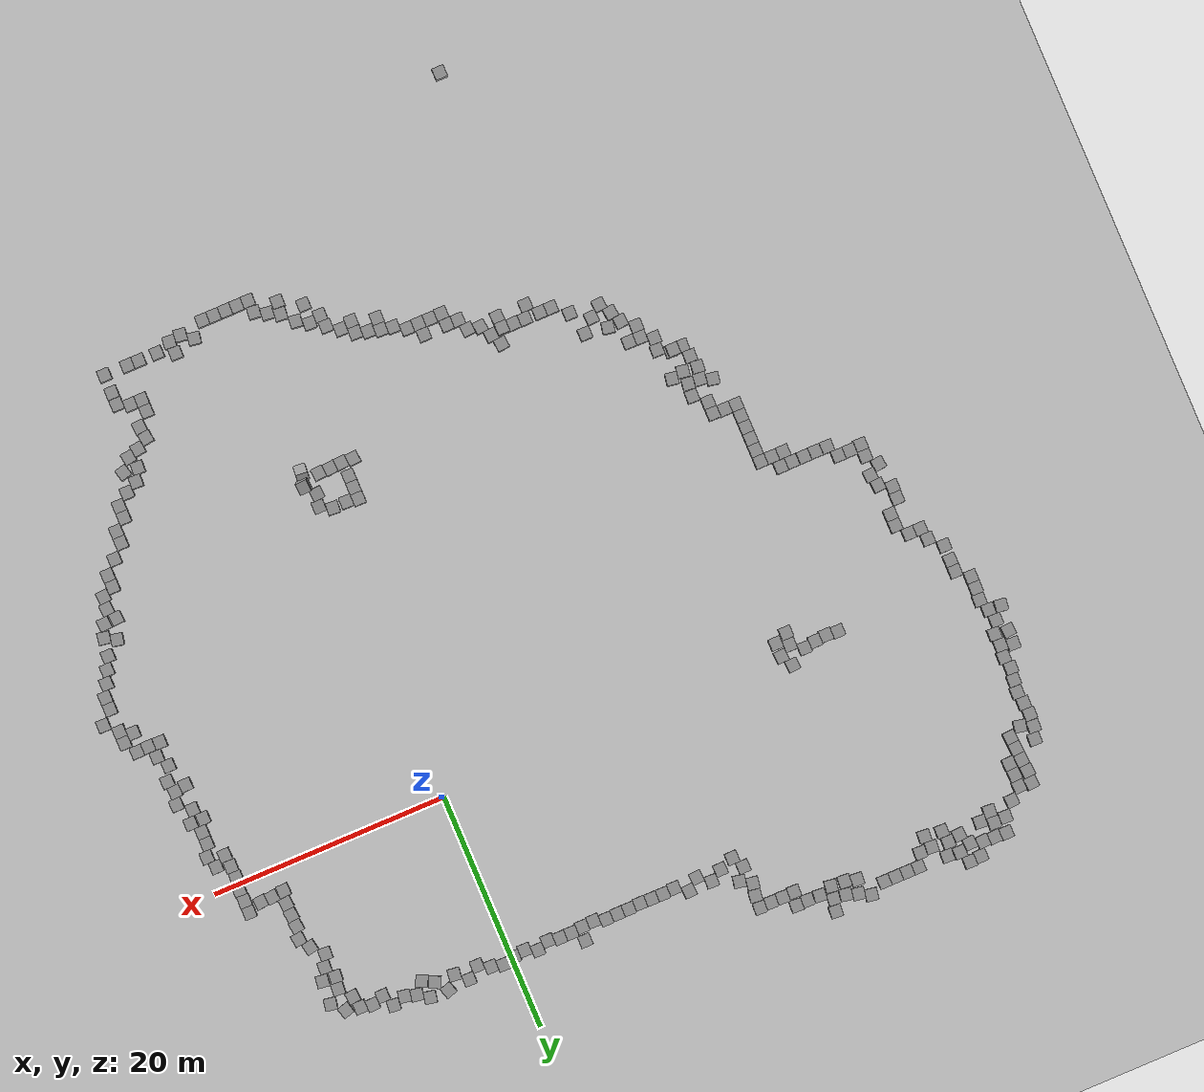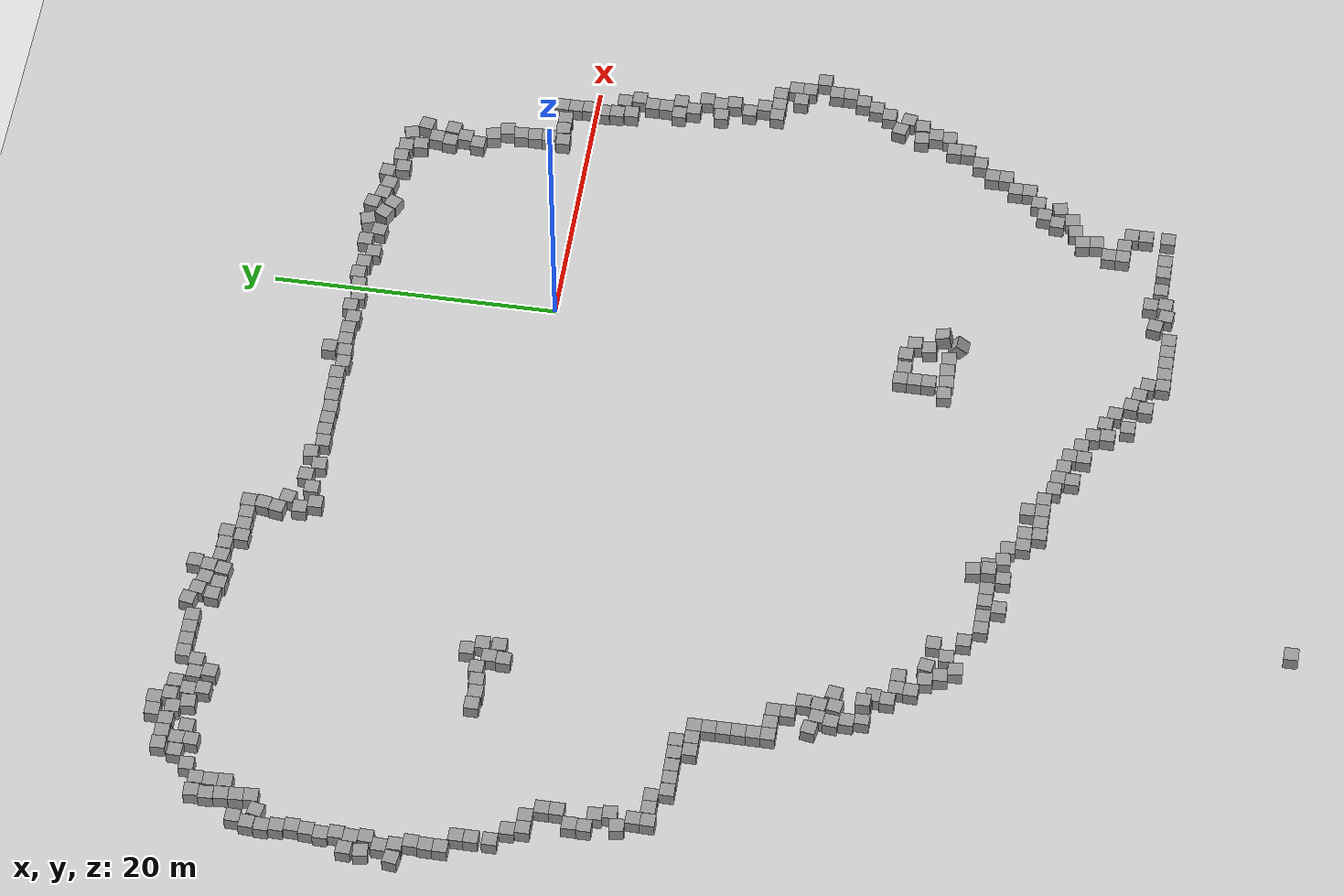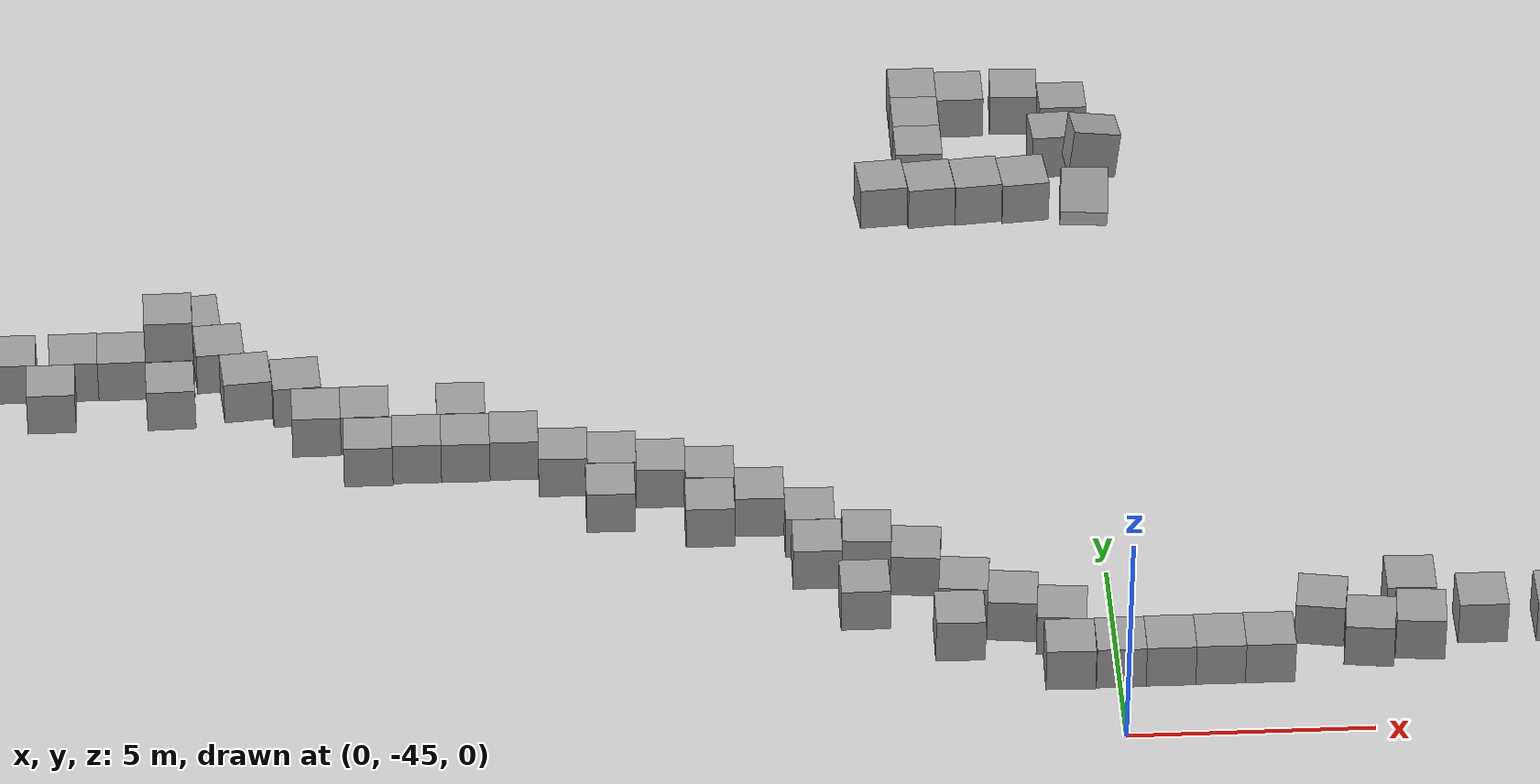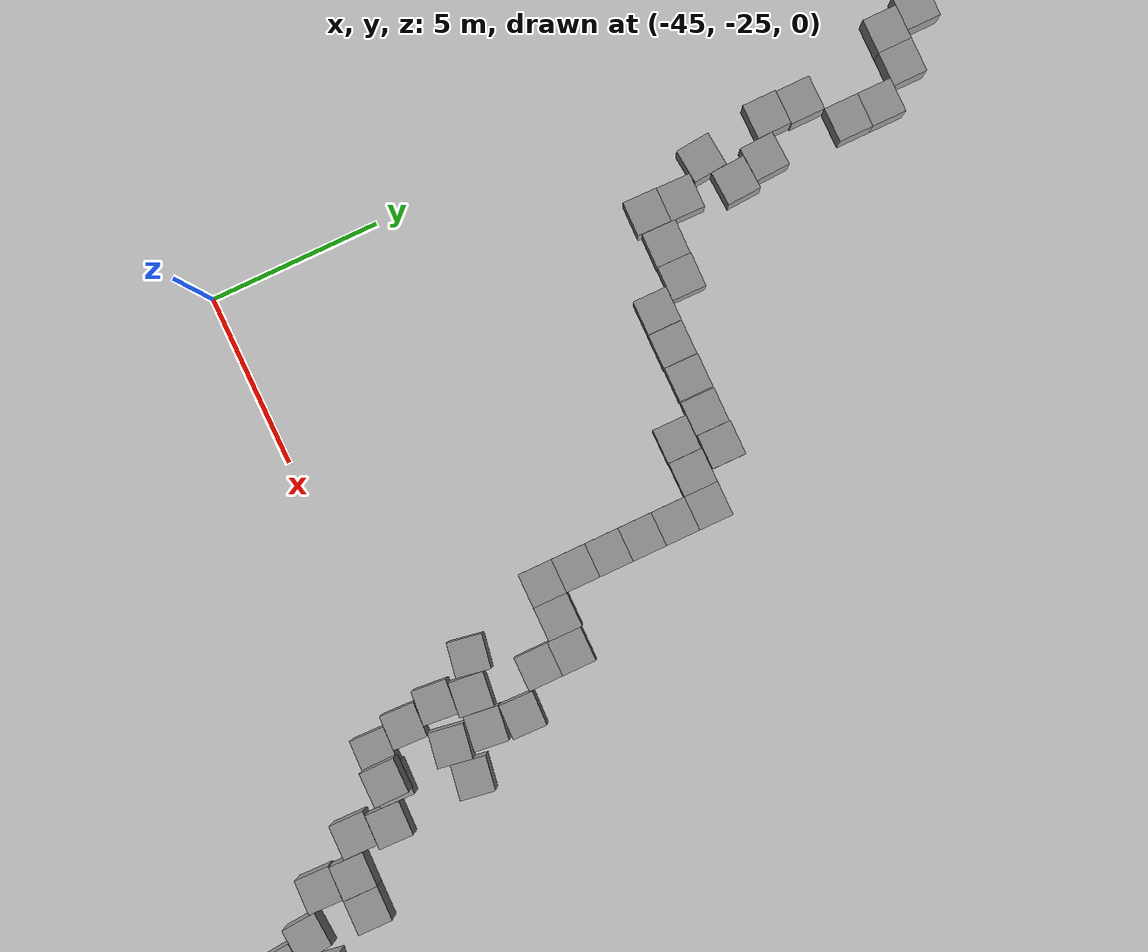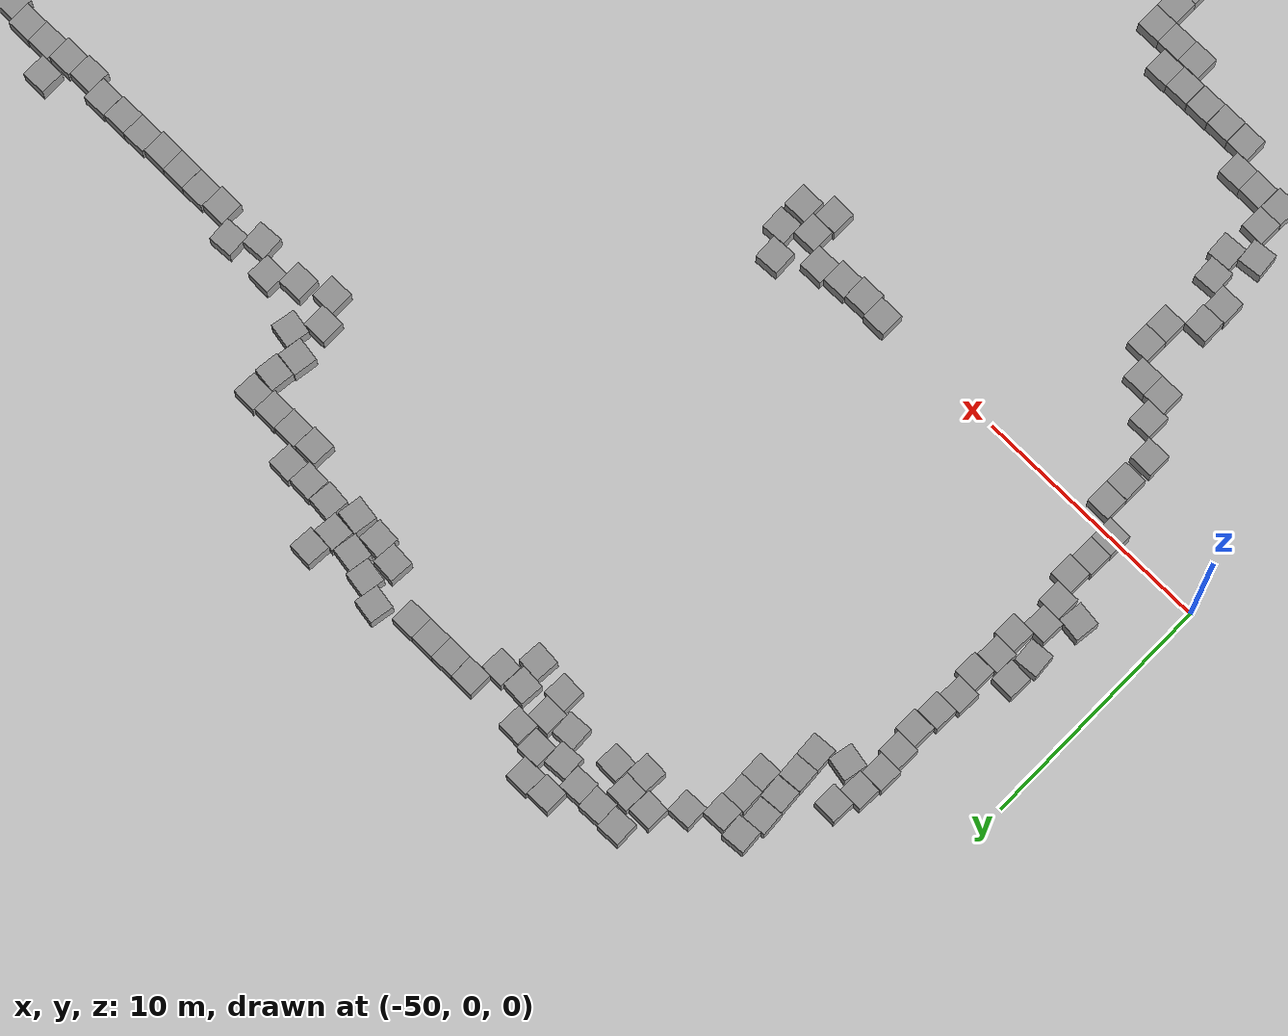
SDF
<sdf version="1.7">
 <world name="default">
  <light name="sun" type="directional">
   <pose>0 0 10 0 -0 0</pose>
   <diffuse>0.8 0.8 0.8 1</diffuse>
   <specular>0.2 0.2 0.2 1</specular>
   <attenuation>
    <range>1000</range>
    <constant>0.9</constant>
    <linear>0.01</linear>
    <quadratic>0.001</quadratic>
   </attenuation>
   <direction>-0.5 0.1 -0.9</direction>
   <spot><inner_angle>0</inner_angle><outer_angle>0</outer_angle><falloff>0</falloff></spot>
  </light>
  <model name="ground_plane">
   <static>1</static>
   <link name="link">
    <collision name="collision">
     <geometry><plane><normal>0 0 1</normal><size>100 100</size></plane></geometry>
     <surface>
      <contact><collide_bitmask>65535</collide_bitmask></contact>
      <friction><ode><mu>100</mu><mu2>50</mu2></ode></friction>
     </surface>
    </collision>
    <visual name="visual">
     <cast_shadows>0</cast_shadows>
     <geometry><plane><normal>0 0 1</normal><size>100 100</size></plane></geometry>
     <material>
      <script><uri>file://media/materials/scripts/gazebo.material</uri><name>Gazebo/Grey</name></script>
     </material>
    </visual>
   </link>
  </model>
  <gravity>0 0 -9.8</gravity>
  <magnetic_field>6e-06 2.3e-05 -4.2e-05</magnetic_field>
  <atmosphere type="adiabatic"/>
  <physics type="ode">
   <max_step_size>0.001</max_step_size>
   <real_time_factor>1</real_time_factor>
   <real_time_update_rate>1000</real_time_update_rate>
  </physics>
  <scene><ambient>0.4 0.4 0.4 1</ambient><background>0.7 0.7 0.7 1</background><shadows>1</shadows></scene>
  <spherical_coordinates>
   <surface_model>EARTH_WGS84</surface_model>
   <latitude_deg>0</latitude_deg>
   <longitude_deg>0</longitude_deg>
   <elevation>0</elevation>
   <heading_deg>0</heading_deg>
  </spherical_coordinates>
  <model name="unit_box">
   <pose>8.14879 13.7403 0.5 0 0 -0.179137</pose>
   <link name="link">
    <inertial>
     <mass>1</mass>
     <inertia>
      <ixx>0.166667</ixx>
      <ixy>0</ixy>
      <ixz>0</ixz>
      <iyy>0.166667</iyy>
      <iyz>0</iyz>
      <izz>0.166667</izz>
     </inertia>
    </inertial>
    <collision name="collision"><geometry><box><size>1 1 1</size></box></geometry></collision>
    <visual name="visual">
     <geometry><box><size>1 1 1</size></box></geometry>
     <material>
      <script><name>Gazebo/Grey</name><uri>file://media/materials/scripts/gazebo.material</uri></script>
     </material>
    </visual>
   </link>
  </model>
  <model name="unit_box_clone">
   <pose>7.24066 14.3428 0.5 0 0 -0.192136</pose>
   <link name="link">
    <inertial>
     <mass>1</mass>
     <inertia>
      <ixx>0.166667</ixx>
      <ixy>0</ixy>
      <ixz>0</ixz>
      <iyy>0.166667</iyy>
      <iyz>0</iyz>
      <izz>0.166667</izz>
     </inertia>
    </inertial>
    <collision name="collision"><geometry><box><size>1 1 1</size></box></geometry></collision>
    <visual name="visual">
     <geometry><box><size>1 1 1</size></box></geometry>
     <material>
      <script><name>Gazebo/Grey</name><uri>file://media/materials/scripts/gazebo.material</uri></script>
     </material>
    </visual>
   </link>
  </model>
  <model name="unit_box_clone_0">
   <pose>7.3663 12.8762 0.5 0 0 -0.431474</pose>
   <link name="link">
    <inertial>
     <mass>1</mass>
     <inertia>
      <ixx>0.166667</ixx>
      <ixy>0</ixy>
      <ixz>0</ixz>
      <iyy>0.166667</iyy>
      <iyz>0</iyz>
      <izz>0.166667</izz>
     </inertia>
    </inertial>
    <collision name="collision"><geometry><box><size>1 1 1</size></box></geometry></collision>
    <visual name="visual">
     <geometry><box><size>1 1 1</size></box></geometry>
     <material>
      <script><name>Gazebo/Grey</name><uri>file://media/materials/scripts/gazebo.material</uri></script>
     </material>
    </visual>
   </link>
  </model>
  <model name="unit_box_clone_1">
   <pose>6.44568 13.3625 0.499996 -7e-06 0 -0.446602</pose>
   <link name="link">
    <inertial>
     <mass>1</mass>
     <inertia>
      <ixx>0.166667</ixx>
      <ixy>0</ixy>
      <ixz>0</ixz>
      <iyy>0.166667</iyy>
      <iyz>0</iyz>
      <izz>0.166667</izz>
     </inertia>
    </inertial>
    <collision name="collision"><geometry><box><size>1 1 1</size></box></geometry></collision>
    <visual name="visual">
     <geometry><box><size>1 1 1</size></box></geometry>
     <material>
      <script><name>Gazebo/Grey</name><uri>file://media/materials/scripts/gazebo.material</uri></script>
     </material>
    </visual>
   </link>
  </model>
  <model name="unit_box_clone_2">
   <pose>5.66448 14.4058 0.5 0 -0 0.299533</pose>
   <link name="link">
    <inertial>
     <mass>1</mass>
     <inertia>
      <ixx>0.166667</ixx>
      <ixy>0</ixy>
      <ixz>0</ixz>
      <iyy>0.166667</iyy>
      <iyz>0</iyz>
      <izz>0.166667</izz>
     </inertia>
    </inertial>
    <collision name="collision"><geometry><box><size>1 1 1</size></box></geometry></collision>
    <visual name="visual">
     <geometry><box><size>1 1 1</size></box></geometry>
     <material>
      <script><name>Gazebo/Grey</name><uri>file://media/materials/scripts/gazebo.material</uri></script>
     </material>
    </visual>
   </link>
  </model>
  <model name="unit_box_clone_3">
   <pose>3.79278 14.2378 0.5 0 -0 -0.002543</pose>
   <link name="link">
    <inertial>
     <mass>1</mass>
     <inertia>
      <ixx>0.166667</ixx>
      <ixy>0</ixy>
      <ixz>0</ixz>
      <iyy>0.166667</iyy>
      <iyz>0</iyz>
      <izz>0.166667</izz>
     </inertia>
    </inertial>
    <collision name="collision"><geometry><box><size>1 1 1</size></box></geometry></collision>
    <visual name="visual">
     <geometry><box><size>1 1 1</size></box></geometry>
     <material>
      <script><name>Gazebo/Grey</name><uri>file://media/materials/scripts/gazebo.material</uri></script>
     </material>
    </visual>
   </link>
  </model>
  <model name="unit_box_clone_4">
   <pose>4.75678 13.4144 0.499995 1e-05 -0 -0.118159</pose>
   <link name="link">
    <inertial>
     <mass>1</mass>
     <inertia>
      <ixx>0.166667</ixx>
      <ixy>0</ixy>
      <ixz>0</ixz>
      <iyy>0.166667</iyy>
      <iyz>0</iyz>
      <izz>0.166667</izz>
     </inertia>
    </inertial>
    <collision name="collision"><geometry><box><size>1 1 1</size></box></geometry></collision>
    <visual name="visual">
     <geometry><box><size>1 1 1</size></box></geometry>
     <material>
      <script><name>Gazebo/Grey</name><uri>file://media/materials/scripts/gazebo.material</uri></script>
     </material>
    </visual>
   </link>
  </model>
  <model name="unit_box_clone_5">
   <pose>1.79217 13.9851 0.5 -0 -0 -0.006324</pose>
   <link name="link">
    <inertial>
     <mass>1</mass>
     <inertia>
      <ixx>0.166667</ixx>
      <ixy>0</ixy>
      <ixz>0</ixz>
      <iyy>0.166667</iyy>
      <iyz>0</iyz>
      <izz>0.166667</izz>
     </inertia>
    </inertial>
    <collision name="collision"><geometry><box><size>1 1 1</size></box></geometry></collision>
    <visual name="visual">
     <geometry><box><size>1 1 1</size></box></geometry>
     <material>
      <script><name>Gazebo/Grey</name><uri>file://media/materials/scripts/gazebo.material</uri></script>
     </material>
    </visual>
   </link>
  </model>
  <model name="unit_box_clone_6">
   <pose>2.78953 13.4697 0.5 0 -0 -0.005146</pose>
   <link name="link">
    <inertial>
     <mass>1</mass>
     <inertia>
      <ixx>0.166667</ixx>
      <ixy>0</ixy>
      <ixz>0</ixz>
      <iyy>0.166667</iyy>
      <iyz>0</iyz>
      <izz>0.166667</izz>
     </inertia>
    </inertial>
    <collision name="collision"><geometry><box><size>1 1 1</size></box></geometry></collision>
    <visual name="visual">
     <geometry><box><size>1 1 1</size></box></geometry>
     <material>
      <script><name>Gazebo/Grey</name><uri>file://media/materials/scripts/gazebo.material</uri></script>
     </material>
    </visual>
   </link>
  </model>
  <model name="unit_box_clone_7">
   <pose>0.793579 14.2116 0.5 0 0 -0.006333</pose>
   <link name="link">
    <inertial>
     <mass>1</mass>
     <inertia>
      <ixx>0.166667</ixx>
      <ixy>0</ixy>
      <ixz>0</ixz>
      <iyy>0.166667</iyy>
      <iyz>0</iyz>
      <izz>0.166667</izz>
     </inertia>
    </inertial>
    <collision name="collision"><geometry><box><size>1 1 1</size></box></geometry></collision>
    <visual name="visual">
     <geometry><box><size>1 1 1</size></box></geometry>
     <material>
      <script><name>Gazebo/Grey</name><uri>file://media/materials/scripts/gazebo.material</uri></script>
     </material>
    </visual>
   </link>
  </model>
  <model name="unit_box_clone_8">
   <pose>-0.207819 13.9965 0.499995 -1e-05 -0 -0.006358</pose>
   <link name="link">
    <inertial>
     <mass>1</mass>
     <inertia>
      <ixx>0.166667</ixx>
      <ixy>0</ixy>
      <ixz>0</ixz>
      <iyy>0.166667</iyy>
      <iyz>0</iyz>
      <izz>0.166667</izz>
     </inertia>
    </inertial>
    <collision name="collision"><geometry><box><size>1 1 1</size></box></geometry></collision>
    <visual name="visual">
     <geometry><box><size>1 1 1</size></box></geometry>
     <material>
      <script><name>Gazebo/Grey</name><uri>file://media/materials/scripts/gazebo.material</uri></script>
     </material>
    </visual>
   </link>
  </model>
  <model name="unit_box_clone_9">
   <pose>-1.20904 13.8093 0.5 0 0 -0.006381</pose>
   <link name="link">
    <inertial>
     <mass>1</mass>
     <inertia>
      <ixx>0.166667</ixx>
      <ixy>0</ixy>
      <ixz>0</ixz>
      <iyy>0.166667</iyy>
      <iyz>0</iyz>
      <izz>0.166667</izz>
     </inertia>
    </inertial>
    <collision name="collision"><geometry><box><size>1 1 1</size></box></geometry></collision>
    <visual name="visual">
     <geometry><box><size>1 1 1</size></box></geometry>
     <material>
      <script><name>Gazebo/Grey</name><uri>file://media/materials/scripts/gazebo.material</uri></script>
     </material>
    </visual>
   </link>
  </model>
  <model name="unit_box_clone_10">
   <pose>-2.20641 14.2267 0.5 -0 -0 -0.006532</pose>
   <link name="link">
    <inertial>
     <mass>1</mass>
     <inertia>
      <ixx>0.166667</ixx>
      <ixy>0</ixy>
      <ixz>0</ixz>
      <iyy>0.166667</iyy>
      <iyz>0</iyz>
      <izz>0.166667</izz>
     </inertia>
    </inertial>
    <collision name="collision"><geometry><box><size>1 1 1</size></box></geometry></collision>
    <visual name="visual">
     <geometry><box><size>1 1 1</size></box></geometry>
     <material>
      <script><name>Gazebo/Grey</name><uri>file://media/materials/scripts/gazebo.material</uri></script>
     </material>
    </visual>
   </link>
  </model>
  <model name="unit_box_clone_11">
   <pose>-3.20904 13.8326 0.499995 0 -1e-05 -0.006582</pose>
   <link name="link">
    <inertial>
     <mass>1</mass>
     <inertia>
      <ixx>0.166667</ixx>
      <ixy>0</ixy>
      <ixz>0</ixz>
      <iyy>0.166667</iyy>
      <iyz>0</iyz>
      <izz>0.166667</izz>
     </inertia>
    </inertial>
    <collision name="collision"><geometry><box><size>1 1 1</size></box></geometry></collision>
    <visual name="visual">
     <geometry><box><size>1 1 1</size></box></geometry>
     <material>
      <script><name>Gazebo/Grey</name><uri>file://media/materials/scripts/gazebo.material</uri></script>
     </material>
    </visual>
   </link>
  </model>
  <model name="unit_box_clone_12">
   <pose>-4.20812 14.0134 0.499995 0 -1e-05 -0.007246</pose>
   <link name="link">
    <inertial>
     <mass>1</mass>
     <inertia>
      <ixx>0.166667</ixx>
      <ixy>0</ixy>
      <ixz>0</ixz>
      <iyy>0.166667</iyy>
      <iyz>0</iyz>
      <izz>0.166667</izz>
     </inertia>
    </inertial>
    <collision name="collision"><geometry><box><size>1 1 1</size></box></geometry></collision>
    <visual name="visual">
     <geometry><box><size>1 1 1</size></box></geometry>
     <material>
      <script><name>Gazebo/Grey</name><uri>file://media/materials/scripts/gazebo.material</uri></script>
     </material>
    </visual>
   </link>
  </model>
  <model name="unit_box_clone_13">
   <pose>-5.20876 14.0027 0.5 -0 -0 -0.007598</pose>
   <link name="link">
    <inertial>
     <mass>1</mass>
     <inertia>
      <ixx>0.166667</ixx>
      <ixy>0</ixy>
      <ixz>0</ixz>
      <iyy>0.166667</iyy>
      <iyz>0</iyz>
      <izz>0.166667</izz>
     </inertia>
    </inertial>
    <collision name="collision"><geometry><box><size>1 1 1</size></box></geometry></collision>
    <visual name="visual">
     <geometry><box><size>1 1 1</size></box></geometry>
     <material>
      <script><name>Gazebo/Grey</name><uri>file://media/materials/scripts/gazebo.material</uri></script>
     </material>
    </visual>
   </link>
  </model>
  <model name="unit_box_clone_14">
   <pose>-6.21043 13.8841 0.499995 -1e-05 -0 -0.007559</pose>
   <link name="link">
    <inertial>
     <mass>1</mass>
     <inertia>
      <ixx>0.166667</ixx>
      <ixy>0</ixy>
      <ixz>0</ixz>
      <iyy>0.166667</iyy>
      <iyz>0</iyz>
      <izz>0.166667</izz>
     </inertia>
    </inertial>
    <collision name="collision"><geometry><box><size>1 1 1</size></box></geometry></collision>
    <visual name="visual">
     <geometry><box><size>1 1 1</size></box></geometry>
     <material>
      <script><name>Gazebo/Grey</name><uri>file://media/materials/scripts/gazebo.material</uri></script>
     </material>
    </visual>
   </link>
  </model>
  <model name="unit_box_clone_15">
   <pose>-6.0009 15.0113 0.5 -0 -0 -0.002611</pose>
   <link name="link">
    <inertial>
     <mass>1</mass>
     <inertia>
      <ixx>0.166667</ixx>
      <ixy>0</ixy>
      <ixz>0</ixz>
      <iyy>0.166667</iyy>
      <iyz>0</iyz>
      <izz>0.166667</izz>
     </inertia>
    </inertial>
    <collision name="collision"><geometry><box><size>1 1 1</size></box></geometry></collision>
    <visual name="visual">
     <geometry><box><size>1 1 1</size></box></geometry>
     <material>
      <script><name>Gazebo/Grey</name><uri>file://media/materials/scripts/gazebo.material</uri></script>
     </material>
    </visual>
   </link>
  </model>
  <model name="unit_box_clone_16">
   <pose>-8.21249 14.0705 0.5 0 -0 -0.008651</pose>
   <link name="link">
    <inertial>
     <mass>1</mass>
     <inertia>
      <ixx>0.166667</ixx>
      <ixy>0</ixy>
      <ixz>0</ixz>
      <iyy>0.166667</iyy>
      <iyz>0</iyz>
      <izz>0.166667</izz>
     </inertia>
    </inertial>
    <collision name="collision"><geometry><box><size>1 1 1</size></box></geometry></collision>
    <visual name="visual">
     <geometry><box><size>1 1 1</size></box></geometry>
     <material>
      <script><name>Gazebo/Grey</name><uri>file://media/materials/scripts/gazebo.material</uri></script>
     </material>
    </visual>
   </link>
  </model>
  <model name="unit_box_clone_17">
   <pose>-7.21146 13.8128 0.499995 0 -1e-05 -0.00754</pose>
   <link name="link">
    <inertial>
     <mass>1</mass>
     <inertia>
      <ixx>0.166667</ixx>
      <ixy>0</ixy>
      <ixz>0</ixz>
      <iyy>0.166667</iyy>
      <iyz>0</iyz>
      <izz>0.166667</izz>
     </inertia>
    </inertial>
    <collision name="collision"><geometry><box><size>1 1 1</size></box></geometry></collision>
    <visual name="visual">
     <geometry><box><size>1 1 1</size></box></geometry>
     <material>
      <script><name>Gazebo/Grey</name><uri>file://media/materials/scripts/gazebo.material</uri></script>
     </material>
    </visual>
   </link>
  </model>
  <model name="unit_box_clone_18">
   <pose>-9.21544 14.0347 0.499995 0 -1e-05 -0.008374</pose>
   <link name="link">
    <inertial>
     <mass>1</mass>
     <inertia>
      <ixx>0.166667</ixx>
      <ixy>0</ixy>
      <ixz>0</ixz>
      <iyy>0.166667</iyy>
      <iyz>0</iyz>
      <izz>0.166667</izz>
     </inertia>
    </inertial>
    <collision name="collision"><geometry><box><size>1 1 1</size></box></geometry></collision>
    <visual name="visual">
     <geometry><box><size>1 1 1</size></box></geometry>
     <material>
      <script><name>Gazebo/Grey</name><uri>file://media/materials/scripts/gazebo.material</uri></script>
     </material>
    </visual>
   </link>
  </model>
  <model name="unit_box_clone_19">
   <pose>-10.2155 14.0343 0.499995 0 9e-06 -0.008419</pose>
   <link name="link">
    <inertial>
     <mass>1</mass>
     <inertia>
      <ixx>0.166667</ixx>
      <ixy>0</ixy>
      <ixz>0</ixz>
      <iyy>0.166667</iyy>
      <iyz>0</iyz>
      <izz>0.166667</izz>
     </inertia>
    </inertial>
    <collision name="collision"><geometry><box><size>1 1 1</size></box></geometry></collision>
    <visual name="visual">
     <geometry><box><size>1 1 1</size></box></geometry>
     <material>
      <script><name>Gazebo/Grey</name><uri>file://media/materials/scripts/gazebo.material</uri></script>
     </material>
    </visual>
   </link>
  </model>
  <model name="unit_box_clone_20">
   <pose>-11.2168 13.9621 0.499995 0 -1e-05 -0.009646</pose>
   <link name="link">
    <inertial>
     <mass>1</mass>
     <inertia>
      <ixx>0.166667</ixx>
      <ixy>0</ixy>
      <ixz>0</ixz>
      <iyy>0.166667</iyy>
      <iyz>0</iyz>
      <izz>0.166667</izz>
     </inertia>
    </inertial>
    <collision name="collision"><geometry><box><size>1 1 1</size></box></geometry></collision>
    <visual name="visual">
     <geometry><box><size>1 1 1</size></box></geometry>
     <material>
      <script><name>Gazebo/Grey</name><uri>file://media/materials/scripts/gazebo.material</uri></script>
     </material>
    </visual>
   </link>
  </model>
  <model name="unit_box_clone_21">
   <pose>-13.2188 13.9931 0.499995 1e-05 -0 -0.010031</pose>
   <link name="link">
    <inertial>
     <mass>1</mass>
     <inertia>
      <ixx>0.166667</ixx>
      <ixy>0</ixy>
      <ixz>0</ixz>
      <iyy>0.166667</iyy>
      <iyz>0</iyz>
      <izz>0.166667</izz>
     </inertia>
    </inertial>
    <collision name="collision"><geometry><box><size>1 1 1</size></box></geometry></collision>
    <visual name="visual">
     <geometry><box><size>1 1 1</size></box></geometry>
     <material>
      <script><name>Gazebo/Grey</name><uri>file://media/materials/scripts/gazebo.material</uri></script>
     </material>
    </visual>
   </link>
  </model>
  <model name="unit_box_clone_22">
   <pose>-12.2173 13.985 0.5 0 0 -0.009679</pose>
   <link name="link">
    <inertial>
     <mass>1</mass>
     <inertia>
      <ixx>0.166667</ixx>
      <ixy>0</ixy>
      <ixz>0</ixz>
      <iyy>0.166667</iyy>
      <iyz>0</iyz>
      <izz>0.166667</izz>
     </inertia>
    </inertial>
    <collision name="collision"><geometry><box><size>1 1 1</size></box></geometry></collision>
    <visual name="visual">
     <geometry><box><size>1 1 1</size></box></geometry>
     <material>
      <script><name>Gazebo/Grey</name><uri>file://media/materials/scripts/gazebo.material</uri></script>
     </material>
    </visual>
   </link>
  </model>
  <model name="unit_box_clone_23">
   <pose>-14.2197 13.9179 0.5 0 -0 -0.010055</pose>
   <link name="link">
    <inertial>
     <mass>1</mass>
     <inertia>
      <ixx>0.166667</ixx>
      <ixy>0</ixy>
      <ixz>0</ixz>
      <iyy>0.166667</iyy>
      <iyz>0</iyz>
      <izz>0.166667</izz>
     </inertia>
    </inertial>
    <collision name="collision"><geometry><box><size>1 1 1</size></box></geometry></collision>
    <visual name="visual">
     <geometry><box><size>1 1 1</size></box></geometry>
     <material>
      <script><name>Gazebo/Grey</name><uri>file://media/materials/scripts/gazebo.material</uri></script>
     </material>
    </visual>
   </link>
  </model>
  <model name="unit_box_clone_24">
   <pose>9.11352 13.4557 0.499995 1e-05 0 -0.179137</pose>
   <link name="link">
    <inertial>
     <mass>1</mass>
     <inertia>
      <ixx>0.166667</ixx>
      <ixy>0</ixy>
      <ixz>0</ixz>
      <iyy>0.166667</iyy>
      <iyz>0</iyz>
      <izz>0.166667</izz>
     </inertia>
    </inertial>
    <collision name="collision"><geometry><box><size>1 1 1</size></box></geometry></collision>
    <visual name="visual">
     <geometry><box><size>1 1 1</size></box></geometry>
     <material>
      <script><name>Gazebo/Grey</name><uri>file://media/materials/scripts/gazebo.material</uri></script>
     </material>
    </visual>
   </link>
  </model>
  <model name="unit_box_clone_25">
   <pose>10.1901 13.7892 0.5 0 -0 -0.101922</pose>
   <link name="link">
    <inertial>
     <mass>1</mass>
     <inertia>
      <ixx>0.166667</ixx>
      <ixy>0</ixy>
      <ixz>0</ixz>
      <iyy>0.166667</iyy>
      <iyz>0</iyz>
      <izz>0.166667</izz>
     </inertia>
    </inertial>
    <collision name="collision"><geometry><box><size>1 1 1</size></box></geometry></collision>
    <visual name="visual">
     <geometry><box><size>1 1 1</size></box></geometry>
     <material>
      <script><name>Gazebo/Grey</name><uri>file://media/materials/scripts/gazebo.material</uri></script>
     </material>
    </visual>
   </link>
  </model>
  <model name="unit_box_clone_26">
   <pose>10.7298 12.742 0.5 0 -0 0.017382</pose>
   <link name="link">
    <inertial>
     <mass>1</mass>
     <inertia>
      <ixx>0.166667</ixx>
      <ixy>0</ixy>
      <ixz>0</ixz>
      <iyy>0.166667</iyy>
      <iyz>0</iyz>
      <izz>0.166667</izz>
     </inertia>
    </inertial>
    <collision name="collision"><geometry><box><size>1 1 1</size></box></geometry></collision>
    <visual name="visual">
     <geometry><box><size>1 1 1</size></box></geometry>
     <material>
      <script><name>Gazebo/Grey</name><uri>file://media/materials/scripts/gazebo.material</uri></script>
     </material>
    </visual>
   </link>
  </model>
  <model name="unit_box_clone_27">
   <pose>12.7296 12.8945 0.5 0 -0 0.021451</pose>
   <link name="link">
    <inertial>
     <mass>1</mass>
     <inertia>
      <ixx>0.166667</ixx>
      <ixy>0</ixy>
      <ixz>0</ixz>
      <iyy>0.166667</iyy>
      <iyz>0</iyz>
      <izz>0.166667</izz>
     </inertia>
    </inertial>
    <collision name="collision"><geometry><box><size>1 1 1</size></box></geometry></collision>
    <visual name="visual">
     <geometry><box><size>1 1 1</size></box></geometry>
     <material>
      <script><name>Gazebo/Grey</name><uri>file://media/materials/scripts/gazebo.material</uri></script>
     </material>
    </visual>
   </link>
  </model>
  <model name="unit_box_clone_28">
   <pose>11.724 13.0861 0.5 0 -0 0.017232</pose>
   <link name="link">
    <inertial>
     <mass>1</mass>
     <inertia>
      <ixx>0.166667</ixx>
      <ixy>0</ixy>
      <ixz>0</ixz>
      <iyy>0.166667</iyy>
      <iyz>0</iyz>
      <izz>0.166667</izz>
     </inertia>
    </inertial>
    <collision name="collision"><geometry><box><size>1 1 1</size></box></geometry></collision>
    <visual name="visual">
     <geometry><box><size>1 1 1</size></box></geometry>
     <material>
      <script><name>Gazebo/Grey</name><uri>file://media/materials/scripts/gazebo.material</uri></script>
     </material>
    </visual>
   </link>
  </model>
  <model name="unit_box_clone_29">
   <pose>12.966 11.8772 0.5 0 -0 0.094128</pose>
   <link name="link">
    <inertial>
     <mass>1</mass>
     <inertia>
      <ixx>0.166667</ixx>
      <ixy>0</ixy>
      <ixz>0</ixz>
      <iyy>0.166667</iyy>
      <iyz>0</iyz>
      <izz>0.166667</izz>
     </inertia>
    </inertial>
    <collision name="collision"><geometry><box><size>1 1 1</size></box></geometry></collision>
    <visual name="visual">
     <geometry><box><size>1 1 1</size></box></geometry>
     <material>
      <script><name>Gazebo/Grey</name><uri>file://media/materials/scripts/gazebo.material</uri></script>
     </material>
    </visual>
   </link>
  </model>
  <model name="unit_box_clone_30">
   <pose>13.8902 12.6714 0.5 0 -0 0.271597</pose>
   <link name="link">
    <inertial>
     <mass>1</mass>
     <inertia>
      <ixx>0.166667</ixx>
      <ixy>0</ixy>
      <ixz>0</ixz>
      <iyy>0.166667</iyy>
      <iyz>0</iyz>
      <izz>0.166667</izz>
     </inertia>
    </inertial>
    <collision name="collision"><geometry><box><size>1 1 1</size></box></geometry></collision>
    <visual name="visual">
     <geometry><box><size>1 1 1</size></box></geometry>
     <material>
      <script><name>Gazebo/Grey</name><uri>file://media/materials/scripts/gazebo.material</uri></script>
     </material>
    </visual>
   </link>
  </model>
  <model name="unit_box_clone_31">
   <pose>13.6101 9.84769 0.499995 0 1e-05 -0.060771</pose>
   <link name="link">
    <inertial>
     <mass>1</mass>
     <inertia>
      <ixx>0.166667</ixx>
      <ixy>0</ixy>
      <ixz>0</ixz>
      <iyy>0.166667</iyy>
      <iyz>0</iyz>
      <izz>0.166667</izz>
     </inertia>
    </inertial>
    <collision name="collision"><geometry><box><size>1 1 1</size></box></geometry></collision>
    <visual name="visual">
     <geometry><box><size>1 1 1</size></box></geometry>
     <material>
      <script><name>Gazebo/Grey</name><uri>file://media/materials/scripts/gazebo.material</uri></script>
     </material>
    </visual>
   </link>
  </model>
  <model name="unit_box_clone_32">
   <pose>14.8438 11.7274 0.5 0 0 -0.167872</pose>
   <link name="link">
    <inertial>
     <mass>1</mass>
     <inertia>
      <ixx>0.166667</ixx>
      <ixy>0</ixy>
      <ixz>0</ixz>
      <iyy>0.166667</iyy>
      <iyz>0</iyz>
      <izz>0.166667</izz>
     </inertia>
    </inertial>
    <collision name="collision"><geometry><box><size>1 1 1</size></box></geometry></collision>
    <visual name="visual">
     <geometry><box><size>1 1 1</size></box></geometry>
     <material>
      <script><name>Gazebo/Grey</name><uri>file://media/materials/scripts/gazebo.material</uri></script>
     </material>
    </visual>
   </link>
  </model>
  <model name="unit_box_clone_33">
   <pose>14.1345 8.81455 0.5 0 -0 -0.053428</pose>
   <link name="link">
    <inertial>
     <mass>1</mass>
     <inertia>
      <ixx>0.166667</ixx>
      <ixy>0</ixy>
      <ixz>0</ixz>
      <iyy>0.166667</iyy>
      <iyz>0</iyz>
      <izz>0.166667</izz>
     </inertia>
    </inertial>
    <collision name="collision"><geometry><box><size>1 1 1</size></box></geometry></collision>
    <visual name="visual">
     <geometry><box><size>1 1 1</size></box></geometry>
     <material>
      <script><name>Gazebo/Grey</name><uri>file://media/materials/scripts/gazebo.material</uri></script>
     </material>
    </visual>
   </link>
  </model>
  <model name="unit_box_clone_34">
   <pose>13.8112 10.8391 0.5 0 0 -0.065775</pose>
   <link name="link">
    <inertial>
     <mass>1</mass>
     <inertia>
      <ixx>0.166667</ixx>
      <ixy>0</ixy>
      <ixz>0</ixz>
      <iyy>0.166667</iyy>
      <iyz>0</iyz>
      <izz>0.166667</izz>
     </inertia>
    </inertial>
    <collision name="collision"><geometry><box><size>1 1 1</size></box></geometry></collision>
    <visual name="visual">
     <geometry><box><size>1 1 1</size></box></geometry>
     <material>
      <script><name>Gazebo/Grey</name><uri>file://media/materials/scripts/gazebo.material</uri></script>
     </material>
    </visual>
   </link>
  </model>
  <model name="unit_box_clone_35">
   <pose>14.7219 9.78393 0.499995 0 1e-05 -0.11977</pose>
   <link name="link">
    <inertial>
     <mass>1</mass>
     <inertia>
      <ixx>0.166667</ixx>
      <ixy>0</ixy>
      <ixz>0</ixz>
      <iyy>0.166667</iyy>
      <iyz>0</iyz>
      <izz>0.166667</izz>
     </inertia>
    </inertial>
    <collision name="collision"><geometry><box><size>1 1 1</size></box></geometry></collision>
    <visual name="visual">
     <geometry><box><size>1 1 1</size></box></geometry>
     <material>
      <script><name>Gazebo/Grey</name><uri>file://media/materials/scripts/gazebo.material</uri></script>
     </material>
    </visual>
   </link>
  </model>
  <model name="unit_box_clone_36">
   <pose>13.665 7.83823 0.5 0 0 -0.053429</pose>
   <link name="link">
    <inertial>
     <mass>1</mass>
     <inertia>
      <ixx>0.166667</ixx>
      <ixy>0</ixy>
      <ixz>0</ixz>
      <iyy>0.166667</iyy>
      <iyz>0</iyz>
      <izz>0.166667</izz>
     </inertia>
    </inertial>
    <collision name="collision"><geometry><box><size>1 1 1</size></box></geometry></collision>
    <visual name="visual">
     <geometry><box><size>1 1 1</size></box></geometry>
     <material>
      <script><name>Gazebo/Grey</name><uri>file://media/materials/scripts/gazebo.material</uri></script>
     </material>
    </visual>
   </link>
  </model>
  <model name="unit_box_clone_37">
   <pose>14.5828 6.88678 0.5 0 -0 0.184765</pose>
   <link name="link">
    <inertial>
     <mass>1</mass>
     <inertia>
      <ixx>0.166667</ixx>
      <ixy>0</ixy>
      <ixz>0</ixz>
      <iyy>0.166667</iyy>
      <iyz>0</iyz>
      <izz>0.166667</izz>
     </inertia>
    </inertial>
    <collision name="collision"><geometry><box><size>1 1 1</size></box></geometry></collision>
    <visual name="visual">
     <geometry><box><size>1 1 1</size></box></geometry>
     <material>
      <script><name>Gazebo/Grey</name><uri>file://media/materials/scripts/gazebo.material</uri></script>
     </material>
    </visual>
   </link>
  </model>
  <model name="unit_box_clone_38">
   <pose>15.1783 5.9445 0.499995 0 -1e-05 0.110683</pose>
   <link name="link">
    <inertial>
     <mass>1</mass>
     <inertia>
      <ixx>0.166667</ixx>
      <ixy>0</ixy>
      <ixz>0</ixz>
      <iyy>0.166667</iyy>
      <iyz>0</iyz>
      <izz>0.166667</izz>
     </inertia>
    </inertial>
    <collision name="collision"><geometry><box><size>1 1 1</size></box></geometry></collision>
    <visual name="visual">
     <geometry><box><size>1 1 1</size></box></geometry>
     <material>
      <script><name>Gazebo/Grey</name><uri>file://media/materials/scripts/gazebo.material</uri></script>
     </material>
    </visual>
   </link>
  </model>
  <model name="unit_box_clone_39">
   <pose>14.9446 4.91207 0.5 0 -0 0.10889</pose>
   <link name="link">
    <inertial>
     <mass>1</mass>
     <inertia>
      <ixx>0.166667</ixx>
      <ixy>0</ixy>
      <ixz>0</ixz>
      <iyy>0.166667</iyy>
      <iyz>0</iyz>
      <izz>0.166667</izz>
     </inertia>
    </inertial>
    <collision name="collision"><geometry><box><size>1 1 1</size></box></geometry></collision>
    <visual name="visual">
     <geometry><box><size>1 1 1</size></box></geometry>
     <material>
      <script><name>Gazebo/Grey</name><uri>file://media/materials/scripts/gazebo.material</uri></script>
     </material>
    </visual>
   </link>
  </model>
  <model name="unit_box_clone_40">
   <pose>14.9689 3.90877 0.499995 0 -1e-05 0.10889</pose>
   <link name="link">
    <inertial>
     <mass>1</mass>
     <inertia>
      <ixx>0.166667</ixx>
      <ixy>0</ixy>
      <ixz>0</ixz>
      <iyy>0.166667</iyy>
      <iyz>0</iyz>
      <izz>0.166667</izz>
     </inertia>
    </inertial>
    <collision name="collision"><geometry><box><size>1 1 1</size></box></geometry></collision>
    <visual name="visual">
     <geometry><box><size>1 1 1</size></box></geometry>
     <material>
      <script><name>Gazebo/Grey</name><uri>file://media/materials/scripts/gazebo.material</uri></script>
     </material>
    </visual>
   </link>
  </model>
  <model name="unit_box_clone_41">
   <pose>14.9918 2.90528 0.5 0 -0 0.108931</pose>
   <link name="link">
    <inertial>
     <mass>1</mass>
     <inertia>
      <ixx>0.166667</ixx>
      <ixy>0</ixy>
      <ixz>0</ixz>
      <iyy>0.166667</iyy>
      <iyz>0</iyz>
      <izz>0.166667</izz>
     </inertia>
    </inertial>
    <collision name="collision"><geometry><box><size>1 1 1</size></box></geometry></collision>
    <visual name="visual">
     <geometry><box><size>1 1 1</size></box></geometry>
     <material>
      <script><name>Gazebo/Grey</name><uri>file://media/materials/scripts/gazebo.material</uri></script>
     </material>
    </visual>
   </link>
  </model>
  <model name="unit_box_clone_42">
   <pose>14.7959 1.85876 0.5 0 -0 0.020394</pose>
   <link name="link">
    <inertial>
     <mass>1</mass>
     <inertia>
      <ixx>0.166667</ixx>
      <ixy>0</ixy>
      <ixz>0</ixz>
      <iyy>0.166667</iyy>
      <iyz>0</iyz>
      <izz>0.166667</izz>
     </inertia>
    </inertial>
    <collision name="collision"><geometry><box><size>1 1 1</size></box></geometry></collision>
    <visual name="visual">
     <geometry><box><size>1 1 1</size></box></geometry>
     <material>
      <script><name>Gazebo/Grey</name><uri>file://media/materials/scripts/gazebo.material</uri></script>
     </material>
    </visual>
   </link>
  </model>
  <model name="unit_box_clone_43">
   <pose>16.8387 2.00716 0.5 0 -0 0.09071</pose>
   <link name="link">
    <inertial>
     <mass>1</mass>
     <inertia>
      <ixx>0.166667</ixx>
      <ixy>0</ixy>
      <ixz>0</ixz>
      <iyy>0.166667</iyy>
      <iyz>0</iyz>
      <izz>0.166667</izz>
     </inertia>
    </inertial>
    <collision name="collision"><geometry><box><size>1 1 1</size></box></geometry></collision>
    <visual name="visual">
     <geometry><box><size>1 1 1</size></box></geometry>
     <material>
      <script><name>Gazebo/Grey</name><uri>file://media/materials/scripts/gazebo.material</uri></script>
     </material>
    </visual>
   </link>
  </model>
  <model name="unit_box_clone_44">
   <pose>15.8323 1.98629 0.5 0 -0 0.099098</pose>
   <link name="link">
    <inertial>
     <mass>1</mass>
     <inertia>
      <ixx>0.166667</ixx>
      <ixy>0</ixy>
      <ixz>0</ixz>
      <iyy>0.166667</iyy>
      <iyz>0</iyz>
      <izz>0.166667</izz>
     </inertia>
    </inertial>
    <collision name="collision"><geometry><box><size>1 1 1</size></box></geometry></collision>
    <visual name="visual">
     <geometry><box><size>1 1 1</size></box></geometry>
     <material>
      <script><name>Gazebo/Grey</name><uri>file://media/materials/scripts/gazebo.material</uri></script>
     </material>
    </visual>
   </link>
  </model>
  <model name="unit_box_clone_45">
   <pose>18.0081 2.42665 0.5 0 0 -0.026177</pose>
   <link name="link">
    <inertial>
     <mass>1</mass>
     <inertia>
      <ixx>0.166667</ixx>
      <ixy>0</ixy>
      <ixz>0</ixz>
      <iyy>0.166667</iyy>
      <iyz>0</iyz>
      <izz>0.166667</izz>
     </inertia>
    </inertial>
    <collision name="collision"><geometry><box><size>1 1 1</size></box></geometry></collision>
    <visual name="visual">
     <geometry><box><size>1 1 1</size></box></geometry>
     <material>
      <script><name>Gazebo/Grey</name><uri>file://media/materials/scripts/gazebo.material</uri></script>
     </material>
    </visual>
   </link>
  </model>
  <model name="unit_box_clone_46">
   <pose>18.0055 1.42428 0.5 0 -0 -0.025157</pose>
   <link name="link">
    <inertial>
     <mass>1</mass>
     <inertia>
      <ixx>0.166667</ixx>
      <ixy>0</ixy>
      <ixz>0</ixz>
      <iyy>0.166667</iyy>
      <iyz>0</iyz>
      <izz>0.166667</izz>
     </inertia>
    </inertial>
    <collision name="collision"><geometry><box><size>1 1 1</size></box></geometry></collision>
    <visual name="visual">
     <geometry><box><size>1 1 1</size></box></geometry>
     <material>
      <script><name>Gazebo/Grey</name><uri>file://media/materials/scripts/gazebo.material</uri></script>
     </material>
    </visual>
   </link>
  </model>
  <model name="unit_box_clone_47">
   <pose>18.0513 0.422691 0.5 0 -0 -0.025369</pose>
   <link name="link">
    <inertial>
     <mass>1</mass>
     <inertia>
      <ixx>0.166667</ixx>
      <ixy>0</ixy>
      <ixz>0</ixz>
      <iyy>0.166667</iyy>
      <iyz>0</iyz>
      <izz>0.166667</izz>
     </inertia>
    </inertial>
    <collision name="collision"><geometry><box><size>1 1 1</size></box></geometry></collision>
    <visual name="visual">
     <geometry><box><size>1 1 1</size></box></geometry>
     <material>
      <script><name>Gazebo/Grey</name><uri>file://media/materials/scripts/gazebo.material</uri></script>
     </material>
    </visual>
   </link>
  </model>
  <model name="unit_box_clone_48">
   <pose>18.0494 -2.59629 0.5 0 -0 0.017199</pose>
   <link name="link">
    <inertial>
     <mass>1</mass>
     <inertia>
      <ixx>0.166667</ixx>
      <ixy>0</ixy>
      <ixz>0</ixz>
      <iyy>0.166667</iyy>
      <iyz>0</iyz>
      <izz>0.166667</izz>
     </inertia>
    </inertial>
    <collision name="collision"><geometry><box><size>1 1 1</size></box></geometry></collision>
    <visual name="visual">
     <geometry><box><size>1 1 1</size></box></geometry>
     <material>
      <script><name>Gazebo/Grey</name><uri>file://media/materials/scripts/gazebo.material</uri></script>
     </material>
    </visual>
   </link>
  </model>
  <model name="unit_box_clone_49">
   <pose>17.8873 -0.574183 0.5 0 0 -0.025239</pose>
   <link name="link">
    <inertial>
     <mass>1</mass>
     <inertia>
      <ixx>0.166667</ixx>
      <ixy>0</ixy>
      <ixz>0</ixz>
      <iyy>0.166667</iyy>
      <iyz>0</iyz>
      <izz>0.166667</izz>
     </inertia>
    </inertial>
    <collision name="collision"><geometry><box><size>1 1 1</size></box></geometry></collision>
    <visual name="visual">
     <geometry><box><size>1 1 1</size></box></geometry>
     <material>
      <script><name>Gazebo/Grey</name><uri>file://media/materials/scripts/gazebo.material</uri></script>
     </material>
    </visual>
   </link>
  </model>
  <model name="unit_box_clone_50">
   <pose>17.9375 -1.57696 0.5 -0 -0 -0.024718</pose>
   <link name="link">
    <inertial>
     <mass>1</mass>
     <inertia>
      <ixx>0.166667</ixx>
      <ixy>0</ixy>
      <ixz>0</ixz>
      <iyy>0.166667</iyy>
      <iyz>0</iyz>
      <izz>0.166667</izz>
     </inertia>
    </inertial>
    <collision name="collision"><geometry><box><size>1 1 1</size></box></geometry></collision>
    <visual name="visual">
     <geometry><box><size>1 1 1</size></box></geometry>
     <material>
      <script><name>Gazebo/Grey</name><uri>file://media/materials/scripts/gazebo.material</uri></script>
     </material>
    </visual>
   </link>
  </model>
  <model name="unit_box_clone_51">
   <pose>19.0395 -1.9857 0.5 0 -0 0.017213</pose>
   <link name="link">
    <inertial>
     <mass>1</mass>
     <inertia>
      <ixx>0.166667</ixx>
      <ixy>0</ixy>
      <ixz>0</ixz>
      <iyy>0.166667</iyy>
      <iyz>0</iyz>
      <izz>0.166667</izz>
     </inertia>
    </inertial>
    <collision name="collision"><geometry><box><size>1 1 1</size></box></geometry></collision>
    <visual name="visual">
     <geometry><box><size>1 1 1</size></box></geometry>
     <material>
      <script><name>Gazebo/Grey</name><uri>file://media/materials/scripts/gazebo.material</uri></script>
     </material>
    </visual>
   </link>
  </model>
  <model name="unit_box_clone_52">
   <pose>19.4313 -2.99999 0.5 -0 -0 -3e-06</pose>
   <link name="link">
    <inertial>
     <mass>1</mass>
     <inertia>
      <ixx>0.166667</ixx>
      <ixy>0</ixy>
      <ixz>0</ixz>
      <iyy>0.166667</iyy>
      <iyz>0</iyz>
      <izz>0.166667</izz>
     </inertia>
    </inertial>
    <collision name="collision"><geometry><box><size>1 1 1</size></box></geometry></collision>
    <visual name="visual">
     <geometry><box><size>1 1 1</size></box></geometry>
     <material>
      <script><name>Gazebo/Grey</name><uri>file://media/materials/scripts/gazebo.material</uri></script>
     </material>
    </visual>
   </link>
  </model>
  <model name="unit_box_clone_53">
   <pose>19 -4.99999 0.5 -0 -0 -0</pose>
   <link name="link">
    <inertial>
     <mass>1</mass>
     <inertia>
      <ixx>0.166667</ixx>
      <ixy>0</ixy>
      <ixz>0</ixz>
      <iyy>0.166667</iyy>
      <iyz>0</iyz>
      <izz>0.166667</izz>
     </inertia>
    </inertial>
    <collision name="collision"><geometry><box><size>1 1 1</size></box></geometry></collision>
    <visual name="visual">
     <geometry><box><size>1 1 1</size></box></geometry>
     <material>
      <script><name>Gazebo/Grey</name><uri>file://media/materials/scripts/gazebo.material</uri></script>
     </material>
    </visual>
   </link>
  </model>
  <model name="unit_box_clone_54">
   <pose>19 -7 0.5 -0 -0 -1.4e-05</pose>
   <link name="link">
    <inertial>
     <mass>1</mass>
     <inertia>
      <ixx>0.166667</ixx>
      <ixy>0</ixy>
      <ixz>0</ixz>
      <iyy>0.166667</iyy>
      <iyz>0</iyz>
      <izz>0.166667</izz>
     </inertia>
    </inertial>
    <collision name="collision"><geometry><box><size>1 1 1</size></box></geometry></collision>
    <visual name="visual">
     <geometry><box><size>1 1 1</size></box></geometry>
     <material>
      <script><name>Gazebo/Grey</name><uri>file://media/materials/scripts/gazebo.material</uri></script>
     </material>
    </visual>
   </link>
  </model>
  <model name="unit_box_clone_55">
   <pose>20.0491 -7.83142 0.5 0 -0 0.026992</pose>
   <link name="link">
    <inertial>
     <mass>1</mass>
     <inertia>
      <ixx>0.166667</ixx>
      <ixy>0</ixy>
      <ixz>0</ixz>
      <iyy>0.166667</iyy>
      <iyz>0</iyz>
      <izz>0.166667</izz>
     </inertia>
    </inertial>
    <collision name="collision"><geometry><box><size>1 1 1</size></box></geometry></collision>
    <visual name="visual">
     <geometry><box><size>1 1 1</size></box></geometry>
     <material>
      <script><name>Gazebo/Grey</name><uri>file://media/materials/scripts/gazebo.material</uri></script>
     </material>
    </visual>
   </link>
  </model>
  <model name="unit_box_clone_56">
   <pose>19.5784 -6 0.5 0 -0 0</pose>
   <link name="link">
    <inertial>
     <mass>1</mass>
     <inertia>
      <ixx>0.166667</ixx>
      <ixy>0</ixy>
      <ixz>0</ixz>
      <iyy>0.166667</iyy>
      <iyz>0</iyz>
      <izz>0.166667</izz>
     </inertia>
    </inertial>
    <collision name="collision"><geometry><box><size>1 1 1</size></box></geometry></collision>
    <visual name="visual">
     <geometry><box><size>1 1 1</size></box></geometry>
     <material>
      <script><name>Gazebo/Grey</name><uri>file://media/materials/scripts/gazebo.material</uri></script>
     </material>
    </visual>
   </link>
  </model>
  <model name="unit_box_clone_57">
   <pose>18.4904 -5.99999 0.5 0 0 -3e-06</pose>
   <link name="link">
    <inertial>
     <mass>1</mass>
     <inertia>
      <ixx>0.166667</ixx>
      <ixy>0</ixy>
      <ixz>0</ixz>
      <iyy>0.166667</iyy>
      <iyz>0</iyz>
      <izz>0.166667</izz>
     </inertia>
    </inertial>
    <collision name="collision"><geometry><box><size>1 1 1</size></box></geometry></collision>
    <visual name="visual">
     <geometry><box><size>1 1 1</size></box></geometry>
     <material>
      <script><name>Gazebo/Grey</name><uri>file://media/materials/scripts/gazebo.material</uri></script>
     </material>
    </visual>
   </link>
  </model>
  <model name="unit_box_clone_58">
   <pose>19 -3.99999 0.5 0 -0 0</pose>
   <link name="link">
    <inertial>
     <mass>1</mass>
     <inertia>
      <ixx>0.166667</ixx>
      <ixy>0</ixy>
      <ixz>0</ixz>
      <iyy>0.166667</iyy>
      <iyz>0</iyz>
      <izz>0.166667</izz>
     </inertia>
    </inertial>
    <collision name="collision"><geometry><box><size>1 1 1</size></box></geometry></collision>
    <visual name="visual">
     <geometry><box><size>1 1 1</size></box></geometry>
     <material>
      <script><name>Gazebo/Grey</name><uri>file://media/materials/scripts/gazebo.material</uri></script>
     </material>
    </visual>
   </link>
  </model>
  <model name="unit_box_clone_59">
   <pose>18.7599 -9.02657 0.5 0 -0 0.030815</pose>
   <link name="link">
    <inertial>
     <mass>1</mass>
     <inertia>
      <ixx>0.166667</ixx>
      <ixy>0</ixy>
      <ixz>0</ixz>
      <iyy>0.166667</iyy>
      <iyz>0</iyz>
      <izz>0.166667</izz>
     </inertia>
    </inertial>
    <collision name="collision"><geometry><box><size>1 1 1</size></box></geometry></collision>
    <visual name="visual">
     <geometry><box><size>1 1 1</size></box></geometry>
     <material>
      <script><name>Gazebo/Grey</name><uri>file://media/materials/scripts/gazebo.material</uri></script>
     </material>
    </visual>
   </link>
  </model>
  <model name="unit_box_clone_60">
   <pose>19.7566 -8.83976 0.5 0 -0 0.026811</pose>
   <link name="link">
    <inertial>
     <mass>1</mass>
     <inertia>
      <ixx>0.166667</ixx>
      <ixy>0</ixy>
      <ixz>0</ixz>
      <iyy>0.166667</iyy>
      <iyz>0</iyz>
      <izz>0.166667</izz>
     </inertia>
    </inertial>
    <collision name="collision"><geometry><box><size>1 1 1</size></box></geometry></collision>
    <visual name="visual">
     <geometry><box><size>1 1 1</size></box></geometry>
     <material>
      <script><name>Gazebo/Grey</name><uri>file://media/materials/scripts/gazebo.material</uri></script>
     </material>
    </visual>
   </link>
  </model>
  <model name="unit_box_clone_61">
   <pose>20.0078 -9.83453 0.5 0 -0 0.027054</pose>
   <link name="link">
    <inertial>
     <mass>1</mass>
     <inertia>
      <ixx>0.166667</ixx>
      <ixy>0</ixy>
      <ixz>0</ixz>
      <iyy>0.166667</iyy>
      <iyz>0</iyz>
      <izz>0.166667</izz>
     </inertia>
    </inertial>
    <collision name="collision"><geometry><box><size>1 1 1</size></box></geometry></collision>
    <visual name="visual">
     <geometry><box><size>1 1 1</size></box></geometry>
     <material>
      <script><name>Gazebo/Grey</name><uri>file://media/materials/scripts/gazebo.material</uri></script>
     </material>
    </visual>
   </link>
  </model>
  <model name="unit_box_clone_62">
   <pose>19.4133 -10.9971 0.5 0 -0 0.003019</pose>
   <link name="link">
    <inertial>
     <mass>1</mass>
     <inertia>
      <ixx>0.166667</ixx>
      <ixy>0</ixy>
      <ixz>0</ixz>
      <iyy>0.166667</iyy>
      <iyz>0</iyz>
      <izz>0.166667</izz>
     </inertia>
    </inertial>
    <collision name="collision"><geometry><box><size>1 1 1</size></box></geometry></collision>
    <visual name="visual">
     <geometry><box><size>1 1 1</size></box></geometry>
     <material>
      <script><name>Gazebo/Grey</name><uri>file://media/materials/scripts/gazebo.material</uri></script>
     </material>
    </visual>
   </link>
  </model>
  <model name="unit_box_clone_63">
   <pose>19.3311 -12.9961 0.5 0 0 -0.00436</pose>
   <link name="link">
    <inertial>
     <mass>1</mass>
     <inertia>
      <ixx>0.166667</ixx>
      <ixy>0</ixy>
      <ixz>0</ixz>
      <iyy>0.166667</iyy>
      <iyz>0</iyz>
      <izz>0.166667</izz>
     </inertia>
    </inertial>
    <collision name="collision"><geometry><box><size>1 1 1</size></box></geometry></collision>
    <visual name="visual">
     <geometry><box><size>1 1 1</size></box></geometry>
     <material>
      <script><name>Gazebo/Grey</name><uri>file://media/materials/scripts/gazebo.material</uri></script>
     </material>
    </visual>
   </link>
  </model>
  <model name="unit_box_clone_64">
   <pose>20.3333 -13.0255 0.5 0 0 -0.002439</pose>
   <link name="link">
    <inertial>
     <mass>1</mass>
     <inertia>
      <ixx>0.166667</ixx>
      <ixy>0</ixy>
      <ixz>0</ixz>
      <iyy>0.166667</iyy>
      <iyz>0</iyz>
      <izz>0.166667</izz>
     </inertia>
    </inertial>
    <collision name="collision"><geometry><box><size>1 1 1</size></box></geometry></collision>
    <visual name="visual">
     <geometry><box><size>1 1 1</size></box></geometry>
     <material>
      <script><name>Gazebo/Grey</name><uri>file://media/materials/scripts/gazebo.material</uri></script>
     </material>
    </visual>
   </link>
  </model>
  <model name="unit_box_clone_65">
   <pose>21.3334 -12.9878 0.5 0 -0 -0.002412</pose>
   <link name="link">
    <inertial>
     <mass>1</mass>
     <inertia>
      <ixx>0.166667</ixx>
      <ixy>0</ixy>
      <ixz>0</ixz>
      <iyy>0.166667</iyy>
      <iyz>0</iyz>
      <izz>0.166667</izz>
     </inertia>
    </inertial>
    <collision name="collision"><geometry><box><size>1 1 1</size></box></geometry></collision>
    <visual name="visual">
     <geometry><box><size>1 1 1</size></box></geometry>
     <material>
      <script><name>Gazebo/Grey</name><uri>file://media/materials/scripts/gazebo.material</uri></script>
     </material>
    </visual>
   </link>
  </model>
  <model name="unit_box_clone_66">
   <pose>20.0016 -11.9962 0.5 0 -0 0.001149</pose>
   <link name="link">
    <inertial>
     <mass>1</mass>
     <inertia>
      <ixx>0.166667</ixx>
      <ixy>0</ixy>
      <ixz>0</ixz>
      <iyy>0.166667</iyy>
      <iyz>0</iyz>
      <izz>0.166667</izz>
     </inertia>
    </inertial>
    <collision name="collision"><geometry><box><size>1 1 1</size></box></geometry></collision>
    <visual name="visual">
     <geometry><box><size>1 1 1</size></box></geometry>
     <material>
      <script><name>Gazebo/Grey</name><uri>file://media/materials/scripts/gazebo.material</uri></script>
     </material>
    </visual>
   </link>
  </model>
  <model name="unit_box_clone_67">
   <pose>21 -14.5273 0.5 0 0 -3e-06</pose>
   <link name="link">
    <inertial>
     <mass>1</mass>
     <inertia>
      <ixx>0.166667</ixx>
      <ixy>0</ixy>
      <ixz>0</ixz>
      <iyy>0.166667</iyy>
      <iyz>0</iyz>
      <izz>0.166667</izz>
     </inertia>
    </inertial>
    <collision name="collision"><geometry><box><size>1 1 1</size></box></geometry></collision>
    <visual name="visual">
     <geometry><box><size>1 1 1</size></box></geometry>
     <material>
      <script><name>Gazebo/Grey</name><uri>file://media/materials/scripts/gazebo.material</uri></script>
     </material>
    </visual>
   </link>
  </model>
  <model name="unit_box_clone_68">
   <pose>22 -14.0441 0.5 0 -0 7e-06</pose>
   <link name="link">
    <inertial>
     <mass>1</mass>
     <inertia>
      <ixx>0.166667</ixx>
      <ixy>0</ixy>
      <ixz>0</ixz>
      <iyy>0.166667</iyy>
      <iyz>0</iyz>
      <izz>0.166667</izz>
     </inertia>
    </inertial>
    <collision name="collision"><geometry><box><size>1 1 1</size></box></geometry></collision>
    <visual name="visual">
     <geometry><box><size>1 1 1</size></box></geometry>
     <material>
      <script><name>Gazebo/Grey</name><uri>file://media/materials/scripts/gazebo.material</uri></script>
     </material>
    </visual>
   </link>
  </model>
  <model name="unit_box_clone_69">
   <pose>22 -15.0441 0.5 0 0 -4e-06</pose>
   <link name="link">
    <inertial>
     <mass>1</mass>
     <inertia>
      <ixx>0.166667</ixx>
      <ixy>0</ixy>
      <ixz>0</ixz>
      <iyy>0.166667</iyy>
      <iyz>0</iyz>
      <izz>0.166667</izz>
     </inertia>
    </inertial>
    <collision name="collision"><geometry><box><size>1 1 1</size></box></geometry></collision>
    <visual name="visual">
     <geometry><box><size>1 1 1</size></box></geometry>
     <material>
      <script><name>Gazebo/Grey</name><uri>file://media/materials/scripts/gazebo.material</uri></script>
     </material>
    </visual>
   </link>
  </model>
  <model name="unit_box_clone_70">
   <pose>23 -16 0.5 -0 -0 -9e-06</pose>
   <link name="link">
    <inertial>
     <mass>1</mass>
     <inertia>
      <ixx>0.166667</ixx>
      <ixy>0</ixy>
      <ixz>0</ixz>
      <iyy>0.166667</iyy>
      <iyz>0</iyz>
      <izz>0.166667</izz>
     </inertia>
    </inertial>
    <collision name="collision"><geometry><box><size>1 1 1</size></box></geometry></collision>
    <visual name="visual">
     <geometry><box><size>1 1 1</size></box></geometry>
     <material>
      <script><name>Gazebo/Grey</name><uri>file://media/materials/scripts/gazebo.material</uri></script>
     </material>
    </visual>
   </link>
  </model>
  <model name="unit_box_clone_71">
   <pose>22 -17 0.5 0 -0 3e-06</pose>
   <link name="link">
    <inertial>
     <mass>1</mass>
     <inertia>
      <ixx>0.166667</ixx>
      <ixy>0</ixy>
      <ixz>0</ixz>
      <iyy>0.166667</iyy>
      <iyz>0</iyz>
      <izz>0.166667</izz>
     </inertia>
    </inertial>
    <collision name="collision"><geometry><box><size>1 1 1</size></box></geometry></collision>
    <visual name="visual">
     <geometry><box><size>1 1 1</size></box></geometry>
     <material>
      <script><name>Gazebo/Grey</name><uri>file://media/materials/scripts/gazebo.material</uri></script>
     </material>
    </visual>
   </link>
  </model>
  <model name="unit_box_clone_72">
   <pose>21.4729 -19 0.5 -0 -0 -9e-06</pose>
   <link name="link">
    <inertial>
     <mass>1</mass>
     <inertia>
      <ixx>0.166667</ixx>
      <ixy>0</ixy>
      <ixz>0</ixz>
      <iyy>0.166667</iyy>
      <iyz>0</iyz>
      <izz>0.166667</izz>
     </inertia>
    </inertial>
    <collision name="collision"><geometry><box><size>1 1 1</size></box></geometry></collision>
    <visual name="visual">
     <geometry><box><size>1 1 1</size></box></geometry>
     <material>
      <script><name>Gazebo/Grey</name><uri>file://media/materials/scripts/gazebo.material</uri></script>
     </material>
    </visual>
   </link>
  </model>
  <model name="unit_box_clone_73">
   <pose>21 -20 0.5 0 -0 1e-05</pose>
   <link name="link">
    <inertial>
     <mass>1</mass>
     <inertia>
      <ixx>0.166667</ixx>
      <ixy>0</ixy>
      <ixz>0</ixz>
      <iyy>0.166667</iyy>
      <iyz>0</iyz>
      <izz>0.166667</izz>
     </inertia>
    </inertial>
    <collision name="collision"><geometry><box><size>1 1 1</size></box></geometry></collision>
    <visual name="visual">
     <geometry><box><size>1 1 1</size></box></geometry>
     <material>
      <script><name>Gazebo/Grey</name><uri>file://media/materials/scripts/gazebo.material</uri></script>
     </material>
    </visual>
   </link>
  </model>
  <model name="unit_box_clone_74">
   <pose>22 -18 0.5 0 -0 -1e-06</pose>
   <link name="link">
    <inertial>
     <mass>1</mass>
     <inertia>
      <ixx>0.166667</ixx>
      <ixy>0</ixy>
      <ixz>0</ixz>
      <iyy>0.166667</iyy>
      <iyz>0</iyz>
      <izz>0.166667</izz>
     </inertia>
    </inertial>
    <collision name="collision"><geometry><box><size>1 1 1</size></box></geometry></collision>
    <visual name="visual">
     <geometry><box><size>1 1 1</size></box></geometry>
     <material>
      <script><name>Gazebo/Grey</name><uri>file://media/materials/scripts/gazebo.material</uri></script>
     </material>
    </visual>
   </link>
  </model>
  <model name="unit_box_clone_75">
   <pose>19.2987 -21.9461 0.5 0 0 -0.202812</pose>
   <link name="link">
    <inertial>
     <mass>1</mass>
     <inertia>
      <ixx>0.166667</ixx>
      <ixy>0</ixy>
      <ixz>0</ixz>
      <iyy>0.166667</iyy>
      <iyz>0</iyz>
      <izz>0.166667</izz>
     </inertia>
    </inertial>
    <collision name="collision"><geometry><box><size>1 1 1</size></box></geometry></collision>
    <visual name="visual">
     <geometry><box><size>1 1 1</size></box></geometry>
     <material>
      <script><name>Gazebo/Grey</name><uri>file://media/materials/scripts/gazebo.material</uri></script>
     </material>
    </visual>
   </link>
  </model>
  <model name="unit_box_clone_76">
   <pose>20.4952 -21 0.5 0 -0 2.5e-05</pose>
   <link name="link">
    <inertial>
     <mass>1</mass>
     <inertia>
      <ixx>0.166667</ixx>
      <ixy>0</ixy>
      <ixz>0</ixz>
      <iyy>0.166667</iyy>
      <iyz>0</iyz>
      <izz>0.166667</izz>
     </inertia>
    </inertial>
    <collision name="collision"><geometry><box><size>1 1 1</size></box></geometry></collision>
    <visual name="visual">
     <geometry><box><size>1 1 1</size></box></geometry>
     <material>
      <script><name>Gazebo/Grey</name><uri>file://media/materials/scripts/gazebo.material</uri></script>
     </material>
    </visual>
   </link>
  </model>
  <model name="unit_box_clone_77">
   <pose>20.2343 -22.4684 0.499995 0 -1e-05 -0.160719</pose>
   <link name="link">
    <inertial>
     <mass>1</mass>
     <inertia>
      <ixx>0.166667</ixx>
      <ixy>0</ixy>
      <ixz>0</ixz>
      <iyy>0.166667</iyy>
      <iyz>0</iyz>
      <izz>0.166667</izz>
     </inertia>
    </inertial>
    <collision name="collision"><geometry><box><size>1 1 1</size></box></geometry></collision>
    <visual name="visual">
     <geometry><box><size>1 1 1</size></box></geometry>
     <material>
      <script><name>Gazebo/Grey</name><uri>file://media/materials/scripts/gazebo.material</uri></script>
     </material>
    </visual>
   </link>
  </model>
  <model name="unit_box_clone_78">
   <pose>19.7832 -23.5026 0.499995 0 1e-05 0.048794</pose>
   <link name="link">
    <inertial>
     <mass>1</mass>
     <inertia>
      <ixx>0.166667</ixx>
      <ixy>0</ixy>
      <ixz>0</ixz>
      <iyy>0.166667</iyy>
      <iyz>0</iyz>
      <izz>0.166667</izz>
     </inertia>
    </inertial>
    <collision name="collision"><geometry><box><size>1 1 1</size></box></geometry></collision>
    <visual name="visual">
     <geometry><box><size>1 1 1</size></box></geometry>
     <material>
      <script><name>Gazebo/Grey</name><uri>file://media/materials/scripts/gazebo.material</uri></script>
     </material>
    </visual>
   </link>
  </model>
  <model name="unit_box_clone_79">
   <pose>18.6934 -23.5639 0.5 0 -0 0.058094</pose>
   <link name="link">
    <inertial>
     <mass>1</mass>
     <inertia>
      <ixx>0.166667</ixx>
      <ixy>0</ixy>
      <ixz>0</ixz>
      <iyy>0.166667</iyy>
      <iyz>0</iyz>
      <izz>0.166667</izz>
     </inertia>
    </inertial>
    <collision name="collision"><geometry><box><size>1 1 1</size></box></geometry></collision>
    <visual name="visual">
     <geometry><box><size>1 1 1</size></box></geometry>
     <material>
      <script><name>Gazebo/Grey</name><uri>file://media/materials/scripts/gazebo.material</uri></script>
     </material>
    </visual>
   </link>
  </model>
  <model name="unit_box_clone_80">
   <pose>19.1256 -24.5424 0.499995 0 1e-05 0.060179</pose>
   <link name="link">
    <inertial>
     <mass>1</mass>
     <inertia>
      <ixx>0.166667</ixx>
      <ixy>0</ixy>
      <ixz>0</ixz>
      <iyy>0.166667</iyy>
      <iyz>0</iyz>
      <izz>0.166667</izz>
     </inertia>
    </inertial>
    <collision name="collision"><geometry><box><size>1 1 1</size></box></geometry></collision>
    <visual name="visual">
     <geometry><box><size>1 1 1</size></box></geometry>
     <material>
      <script><name>Gazebo/Grey</name><uri>file://media/materials/scripts/gazebo.material</uri></script>
     </material>
    </visual>
   </link>
  </model>
  <model name="unit_box_clone_81">
   <pose>17.9863 -26.003 0.5 0 -0 0.004914</pose>
   <link name="link">
    <inertial>
     <mass>1</mass>
     <inertia>
      <ixx>0.166667</ixx>
      <ixy>0</ixy>
      <ixz>0</ixz>
      <iyy>0.166667</iyy>
      <iyz>0</iyz>
      <izz>0.166667</izz>
     </inertia>
    </inertial>
    <collision name="collision"><geometry><box><size>1 1 1</size></box></geometry></collision>
    <visual name="visual">
     <geometry><box><size>1 1 1</size></box></geometry>
     <material>
      <script><name>Gazebo/Grey</name><uri>file://media/materials/scripts/gazebo.material</uri></script>
     </material>
    </visual>
   </link>
  </model>
  <model name="unit_box_clone_82">
   <pose>18 -27.0032 0.5 0 -0 0.004405</pose>
   <link name="link">
    <inertial>
     <mass>1</mass>
     <inertia>
      <ixx>0.166667</ixx>
      <ixy>0</ixy>
      <ixz>0</ixz>
      <iyy>0.166667</iyy>
      <iyz>0</iyz>
      <izz>0.166667</izz>
     </inertia>
    </inertial>
    <collision name="collision"><geometry><box><size>1 1 1</size></box></geometry></collision>
    <visual name="visual">
     <geometry><box><size>1 1 1</size></box></geometry>
     <material>
      <script><name>Gazebo/Grey</name><uri>file://media/materials/scripts/gazebo.material</uri></script>
     </material>
    </visual>
   </link>
  </model>
  <model name="unit_box_clone_83">
   <pose>17 -28 0.5 0 -0 -3e-06</pose>
   <link name="link">
    <inertial>
     <mass>1</mass>
     <inertia>
      <ixx>0.166667</ixx>
      <ixy>0</ixy>
      <ixz>0</ixz>
      <iyy>0.166667</iyy>
      <iyz>0</iyz>
      <izz>0.166667</izz>
     </inertia>
    </inertial>
    <collision name="collision"><geometry><box><size>1 1 1</size></box></geometry></collision>
    <visual name="visual">
     <geometry><box><size>1 1 1</size></box></geometry>
     <material>
      <script><name>Gazebo/Grey</name><uri>file://media/materials/scripts/gazebo.material</uri></script>
     </material>
    </visual>
   </link>
  </model>
  <model name="unit_box_clone_84">
   <pose>18.9879 -25.5529 0.499995 -1e-05 -0 0.059931</pose>
   <link name="link">
    <inertial>
     <mass>1</mass>
     <inertia>
      <ixx>0.166667</ixx>
      <ixy>0</ixy>
      <ixz>0</ixz>
      <iyy>0.166667</iyy>
      <iyz>0</iyz>
      <izz>0.166667</izz>
     </inertia>
    </inertial>
    <collision name="collision"><geometry><box><size>1 1 1</size></box></geometry></collision>
    <visual name="visual">
     <geometry><box><size>1 1 1</size></box></geometry>
     <material>
      <script><name>Gazebo/Grey</name><uri>file://media/materials/scripts/gazebo.material</uri></script>
     </material>
    </visual>
   </link>
  </model>
  <model name="unit_box_clone_85">
   <pose>16 -29 0.5 0 -0 0</pose>
   <link name="link">
    <inertial>
     <mass>1</mass>
     <inertia>
      <ixx>0.166667</ixx>
      <ixy>0</ixy>
      <ixz>0</ixz>
      <iyy>0.166667</iyy>
      <iyz>0</iyz>
      <izz>0.166667</izz>
     </inertia>
    </inertial>
    <collision name="collision"><geometry><box><size>1 1 1</size></box></geometry></collision>
    <visual name="visual">
     <geometry><box><size>1 1 1</size></box></geometry>
     <material>
      <script><name>Gazebo/Grey</name><uri>file://media/materials/scripts/gazebo.material</uri></script>
     </material>
    </visual>
   </link>
  </model>
  <model name="unit_box_clone_86">
   <pose>16 -30 0.5 0 0 -2e-06</pose>
   <link name="link">
    <inertial>
     <mass>1</mass>
     <inertia>
      <ixx>0.166667</ixx>
      <ixy>0</ixy>
      <ixz>0</ixz>
      <iyy>0.166667</iyy>
      <iyz>0</iyz>
      <izz>0.166667</izz>
     </inertia>
    </inertial>
    <collision name="collision"><geometry><box><size>1 1 1</size></box></geometry></collision>
    <visual name="visual">
     <geometry><box><size>1 1 1</size></box></geometry>
     <material>
      <script><name>Gazebo/Grey</name><uri>file://media/materials/scripts/gazebo.material</uri></script>
     </material>
    </visual>
   </link>
  </model>
  <model name="unit_box_clone_87">
   <pose>14.9996 -31.7918 0.5 0 -0 0.000725</pose>
   <link name="link">
    <inertial>
     <mass>1</mass>
     <inertia>
      <ixx>0.166667</ixx>
      <ixy>0</ixy>
      <ixz>0</ixz>
      <iyy>0.166667</iyy>
      <iyz>0</iyz>
      <izz>0.166667</izz>
     </inertia>
    </inertial>
    <collision name="collision"><geometry><box><size>1 1 1</size></box></geometry></collision>
    <visual name="visual">
     <geometry><box><size>1 1 1</size></box></geometry>
     <material>
      <script><name>Gazebo/Grey</name><uri>file://media/materials/scripts/gazebo.material</uri></script>
     </material>
    </visual>
   </link>
  </model>
  <model name="unit_box_clone_88">
   <pose>13.9969 -32.5442 0.5 0 0 -0.004315</pose>
   <link name="link">
    <inertial>
     <mass>1</mass>
     <inertia>
      <ixx>0.166667</ixx>
      <ixy>0</ixy>
      <ixz>0</ixz>
      <iyy>0.166667</iyy>
      <iyz>0</iyz>
      <izz>0.166667</izz>
     </inertia>
    </inertial>
    <collision name="collision"><geometry><box><size>1 1 1</size></box></geometry></collision>
    <visual name="visual">
     <geometry><box><size>1 1 1</size></box></geometry>
     <material>
      <script><name>Gazebo/Grey</name><uri>file://media/materials/scripts/gazebo.material</uri></script>
     </material>
    </visual>
   </link>
  </model>
  <model name="unit_box_clone_89">
   <pose>15 -30.7915 0.5 0 -0 0.000207</pose>
   <link name="link">
    <inertial>
     <mass>1</mass>
     <inertia>
      <ixx>0.166667</ixx>
      <ixy>0</ixy>
      <ixz>0</ixz>
      <iyy>0.166667</iyy>
      <iyz>0</iyz>
      <izz>0.166667</izz>
     </inertia>
    </inertial>
    <collision name="collision"><geometry><box><size>1 1 1</size></box></geometry></collision>
    <visual name="visual">
     <geometry><box><size>1 1 1</size></box></geometry>
     <material>
      <script><name>Gazebo/Grey</name><uri>file://media/materials/scripts/gazebo.material</uri></script>
     </material>
    </visual>
   </link>
  </model>
  <model name="unit_box_clone_90">
   <pose>12.7797 -35.104 0.5 0 -0 0.128414</pose>
   <link name="link">
    <inertial>
     <mass>1</mass>
     <inertia>
      <ixx>0.166667</ixx>
      <ixy>0</ixy>
      <ixz>0</ixz>
      <iyy>0.166667</iyy>
      <iyz>0</iyz>
      <izz>0.166667</izz>
     </inertia>
    </inertial>
    <collision name="collision"><geometry><box><size>1 1 1</size></box></geometry></collision>
    <visual name="visual">
     <geometry><box><size>1 1 1</size></box></geometry>
     <material>
      <script><name>Gazebo/Grey</name><uri>file://media/materials/scripts/gazebo.material</uri></script>
     </material>
    </visual>
   </link>
  </model>
  <model name="unit_box_clone_91">
   <pose>12.41 -34.0658 0.5 0 0 -0.03862</pose>
   <link name="link">
    <inertial>
     <mass>1</mass>
     <inertia>
      <ixx>0.166667</ixx>
      <ixy>0</ixy>
      <ixz>0</ixz>
      <iyy>0.166667</iyy>
      <iyz>0</iyz>
      <izz>0.166667</izz>
     </inertia>
    </inertial>
    <collision name="collision"><geometry><box><size>1 1 1</size></box></geometry></collision>
    <visual name="visual">
     <geometry><box><size>1 1 1</size></box></geometry>
     <material>
      <script><name>Gazebo/Grey</name><uri>file://media/materials/scripts/gazebo.material</uri></script>
     </material>
    </visual>
   </link>
  </model>
  <model name="unit_box_clone_92">
   <pose>13.6292 -34.1431 0.5 0 -0 0.237766</pose>
   <link name="link">
    <inertial>
     <mass>1</mass>
     <inertia>
      <ixx>0.166667</ixx>
      <ixy>0</ixy>
      <ixz>0</ixz>
      <iyy>0.166667</iyy>
      <iyz>0</iyz>
      <izz>0.166667</izz>
     </inertia>
    </inertial>
    <collision name="collision"><geometry><box><size>1 1 1</size></box></geometry></collision>
    <visual name="visual">
     <geometry><box><size>1 1 1</size></box></geometry>
     <material>
      <script><name>Gazebo/Grey</name><uri>file://media/materials/scripts/gazebo.material</uri></script>
     </material>
    </visual>
   </link>
  </model>
  <model name="unit_box_clone_93">
   <pose>12.9775 -33.0869 0.5 0 0 -0.03902</pose>
   <link name="link">
    <inertial>
     <mass>1</mass>
     <inertia>
      <ixx>0.166667</ixx>
      <ixy>0</ixy>
      <ixz>0</ixz>
      <iyy>0.166667</iyy>
      <iyz>0</iyz>
      <izz>0.166667</izz>
     </inertia>
    </inertial>
    <collision name="collision"><geometry><box><size>1 1 1</size></box></geometry></collision>
    <visual name="visual">
     <geometry><box><size>1 1 1</size></box></geometry>
     <material>
      <script><name>Gazebo/Grey</name><uri>file://media/materials/scripts/gazebo.material</uri></script>
     </material>
    </visual>
   </link>
  </model>
  <model name="unit_box_clone_94">
   <pose>11.0055 -37.0322 0.5 0 -0 0.07946</pose>
   <link name="link">
    <inertial>
     <mass>1</mass>
     <inertia>
      <ixx>0.166667</ixx>
      <ixy>0</ixy>
      <ixz>0</ixz>
      <iyy>0.166667</iyy>
      <iyz>0</iyz>
      <izz>0.166667</izz>
     </inertia>
    </inertial>
    <collision name="collision"><geometry><box><size>1 1 1</size></box></geometry></collision>
    <visual name="visual">
     <geometry><box><size>1 1 1</size></box></geometry>
     <material>
      <script><name>Gazebo/Grey</name><uri>file://media/materials/scripts/gazebo.material</uri></script>
     </material>
    </visual>
   </link>
  </model>
  <model name="unit_box_clone_95">
   <pose>11.8162 -35.451 0.499995 -1e-05 -0 0.128412</pose>
   <link name="link">
    <inertial>
     <mass>1</mass>
     <inertia>
      <ixx>0.166667</ixx>
      <ixy>0</ixy>
      <ixz>0</ixz>
      <iyy>0.166667</iyy>
      <iyz>0</iyz>
      <izz>0.166667</izz>
     </inertia>
    </inertial>
    <collision name="collision"><geometry><box><size>1 1 1</size></box></geometry></collision>
    <visual name="visual">
     <geometry><box><size>1 1 1</size></box></geometry>
     <material>
      <script><name>Gazebo/Grey</name><uri>file://media/materials/scripts/gazebo.material</uri></script>
     </material>
    </visual>
   </link>
  </model>
  <model name="unit_box_clone_96">
   <pose>10.8645 -36.0344 0.5 0 -0 0.092572</pose>
   <link name="link">
    <inertial>
     <mass>1</mass>
     <inertia>
      <ixx>0.166667</ixx>
      <ixy>0</ixy>
      <ixz>0</ixz>
      <iyy>0.166667</iyy>
      <iyz>0</iyz>
      <izz>0.166667</izz>
     </inertia>
    </inertial>
    <collision name="collision"><geometry><box><size>1 1 1</size></box></geometry></collision>
    <visual name="visual">
     <geometry><box><size>1 1 1</size></box></geometry>
     <material>
      <script><name>Gazebo/Grey</name><uri>file://media/materials/scripts/gazebo.material</uri></script>
     </material>
    </visual>
   </link>
  </model>
  <model name="unit_box_clone_97">
   <pose>10 -38 0.5 0 -0 2e-06</pose>
   <link name="link">
    <inertial>
     <mass>1</mass>
     <inertia>
      <ixx>0.166667</ixx>
      <ixy>0</ixy>
      <ixz>0</ixz>
      <iyy>0.166667</iyy>
      <iyz>0</iyz>
      <izz>0.166667</izz>
     </inertia>
    </inertial>
    <collision name="collision"><geometry><box><size>1 1 1</size></box></geometry></collision>
    <visual name="visual">
     <geometry><box><size>1 1 1</size></box></geometry>
     <material>
      <script><name>Gazebo/Grey</name><uri>file://media/materials/scripts/gazebo.material</uri></script>
     </material>
    </visual>
   </link>
  </model>
  <model name="unit_box_clone_98">
   <pose>10 -39 0.499995 0 1e-05 -5e-06</pose>
   <link name="link">
    <inertial>
     <mass>1</mass>
     <inertia>
      <ixx>0.166667</ixx>
      <ixy>0</ixy>
      <ixz>0</ixz>
      <iyy>0.166667</iyy>
      <iyz>0</iyz>
      <izz>0.166667</izz>
     </inertia>
    </inertial>
    <collision name="collision"><geometry><box><size>1 1 1</size></box></geometry></collision>
    <visual name="visual">
     <geometry><box><size>1 1 1</size></box></geometry>
     <material>
      <script><name>Gazebo/Grey</name><uri>file://media/materials/scripts/gazebo.material</uri></script>
     </material>
    </visual>
   </link>
  </model>
  <model name="unit_box_clone_99">
   <pose>11 -39 0.499995 0 1e-05 -1.1e-05</pose>
   <link name="link">
    <inertial>
     <mass>1</mass>
     <inertia>
      <ixx>0.166667</ixx>
      <ixy>0</ixy>
      <ixz>0</ixz>
      <iyy>0.166667</iyy>
      <iyz>0</iyz>
      <izz>0.166667</izz>
     </inertia>
    </inertial>
    <collision name="collision"><geometry><box><size>1 1 1</size></box></geometry></collision>
    <visual name="visual">
     <geometry><box><size>1 1 1</size></box></geometry>
     <material>
      <script><name>Gazebo/Grey</name><uri>file://media/materials/scripts/gazebo.material</uri></script>
     </material>
    </visual>
   </link>
  </model>
  <model name="unit_box_clone_100">
   <pose>12 -39.4267 0.499995 0 -1e-05 -3e-05</pose>
   <link name="link">
    <inertial>
     <mass>1</mass>
     <inertia>
      <ixx>0.166667</ixx>
      <ixy>0</ixy>
      <ixz>0</ixz>
      <iyy>0.166667</iyy>
      <iyz>0</iyz>
      <izz>0.166667</izz>
     </inertia>
    </inertial>
    <collision name="collision"><geometry><box><size>1 1 1</size></box></geometry></collision>
    <visual name="visual">
     <geometry><box><size>1 1 1</size></box></geometry>
     <material>
      <script><name>Gazebo/Grey</name><uri>file://media/materials/scripts/gazebo.material</uri></script>
     </material>
    </visual>
   </link>
  </model>
  <model name="unit_box_clone_101">
   <pose>12 -40.455 0.5 -0 -0 -0</pose>
   <link name="link">
    <inertial>
     <mass>1</mass>
     <inertia>
      <ixx>0.166667</ixx>
      <ixy>0</ixy>
      <ixz>0</ixz>
      <iyy>0.166667</iyy>
      <iyz>0</iyz>
      <izz>0.166667</izz>
     </inertia>
    </inertial>
    <collision name="collision"><geometry><box><size>1 1 1</size></box></geometry></collision>
    <visual name="visual">
     <geometry><box><size>1 1 1</size></box></geometry>
     <material>
      <script><name>Gazebo/Grey</name><uri>file://media/materials/scripts/gazebo.material</uri></script>
     </material>
    </visual>
   </link>
  </model>
  <model name="unit_box_clone_102">
   <pose>12 -42 0.5 0 -0 0</pose>
   <link name="link">
    <inertial>
     <mass>1</mass>
     <inertia>
      <ixx>0.166667</ixx>
      <ixy>0</ixy>
      <ixz>0</ixz>
      <iyy>0.166667</iyy>
      <iyz>0</iyz>
      <izz>0.166667</izz>
     </inertia>
    </inertial>
    <collision name="collision"><geometry><box><size>1 1 1</size></box></geometry></collision>
    <visual name="visual">
     <geometry><box><size>1 1 1</size></box></geometry>
     <material>
      <script><name>Gazebo/Grey</name><uri>file://media/materials/scripts/gazebo.material</uri></script>
     </material>
    </visual>
   </link>
  </model>
  <model name="unit_box_clone_103">
   <pose>9.99998 -42 0.5 0 0 -2.1e-05</pose>
   <link name="link">
    <inertial>
     <mass>1</mass>
     <inertia>
      <ixx>0.166667</ixx>
      <ixy>0</ixy>
      <ixz>0</ixz>
      <iyy>0.166667</iyy>
      <iyz>0</iyz>
      <izz>0.166667</izz>
     </inertia>
    </inertial>
    <collision name="collision"><geometry><box><size>1 1 1</size></box></geometry></collision>
    <visual name="visual">
     <geometry><box><size>1 1 1</size></box></geometry>
     <material>
      <script><name>Gazebo/Grey</name><uri>file://media/materials/scripts/gazebo.material</uri></script>
     </material>
    </visual>
   </link>
  </model>
  <model name="unit_box_clone_104">
   <pose>8.99998 -42 0.5 -0 -0 -2.1e-05</pose>
   <link name="link">
    <inertial>
     <mass>1</mass>
     <inertia>
      <ixx>0.166667</ixx>
      <ixy>0</ixy>
      <ixz>0</ixz>
      <iyy>0.166667</iyy>
      <iyz>0</iyz>
      <izz>0.166667</izz>
     </inertia>
    </inertial>
    <collision name="collision"><geometry><box><size>1 1 1</size></box></geometry></collision>
    <visual name="visual">
     <geometry><box><size>1 1 1</size></box></geometry>
     <material>
      <script><name>Gazebo/Grey</name><uri>file://media/materials/scripts/gazebo.material</uri></script>
     </material>
    </visual>
   </link>
  </model>
  <model name="unit_box_clone_105">
   <pose>7.41421 -42 0.5 0 -0 0</pose>
   <link name="link">
    <inertial>
     <mass>1</mass>
     <inertia>
      <ixx>0.166667</ixx>
      <ixy>0</ixy>
      <ixz>0</ixz>
      <iyy>0.166667</iyy>
      <iyz>0</iyz>
      <izz>0.166667</izz>
     </inertia>
    </inertial>
    <collision name="collision"><geometry><box><size>1 1 1</size></box></geometry></collision>
    <visual name="visual">
     <geometry><box><size>1 1 1</size></box></geometry>
     <material>
      <script><name>Gazebo/Grey</name><uri>file://media/materials/scripts/gazebo.material</uri></script>
     </material>
    </visual>
   </link>
  </model>
  <model name="unit_box_clone_106">
   <pose>6.13993 -42.4397 0.499997 -6e-06 1e-06 -0.085546</pose>
   <link name="link">
    <inertial>
     <mass>1</mass>
     <inertia>
      <ixx>0.166667</ixx>
      <ixy>0</ixy>
      <ixz>0</ixz>
      <iyy>0.166667</iyy>
      <iyz>0</iyz>
      <izz>0.166667</izz>
     </inertia>
    </inertial>
    <collision name="collision"><geometry><box><size>1 1 1</size></box></geometry></collision>
    <visual name="visual">
     <geometry><box><size>1 1 1</size></box></geometry>
     <material>
      <script><name>Gazebo/Grey</name><uri>file://media/materials/scripts/gazebo.material</uri></script>
     </material>
    </visual>
   </link>
  </model>
  <model name="unit_box_clone_107">
   <pose>5.10625 -42.5993 0.5 -0 -0 -0.118625</pose>
   <link name="link">
    <inertial>
     <mass>1</mass>
     <inertia>
      <ixx>0.166667</ixx>
      <ixy>0</ixy>
      <ixz>0</ixz>
      <iyy>0.166667</iyy>
      <iyz>0</iyz>
      <izz>0.166667</izz>
     </inertia>
    </inertial>
    <collision name="collision"><geometry><box><size>1 1 1</size></box></geometry></collision>
    <visual name="visual">
     <geometry><box><size>1 1 1</size></box></geometry>
     <material>
      <script><name>Gazebo/Grey</name><uri>file://media/materials/scripts/gazebo.material</uri></script>
     </material>
    </visual>
   </link>
  </model>
  <model name="unit_box_clone_108">
   <pose>6.01683 -41.4029 0.5 0 0 -0.019975</pose>
   <link name="link">
    <inertial>
     <mass>1</mass>
     <inertia>
      <ixx>0.166667</ixx>
      <ixy>0</ixy>
      <ixz>0</ixz>
      <iyy>0.166667</iyy>
      <iyz>0</iyz>
      <izz>0.166667</izz>
     </inertia>
    </inertial>
    <collision name="collision"><geometry><box><size>1 1 1</size></box></geometry></collision>
    <visual name="visual">
     <geometry><box><size>1 1 1</size></box></geometry>
     <material>
      <script><name>Gazebo/Grey</name><uri>file://media/materials/scripts/gazebo.material</uri></script>
     </material>
    </visual>
   </link>
  </model>
  <model name="unit_box_clone_109">
   <pose>4.18332 -41.9137 0.5 0 -0 -0.157843</pose>
   <link name="link">
    <inertial>
     <mass>1</mass>
     <inertia>
      <ixx>0.166667</ixx>
      <ixy>0</ixy>
      <ixz>0</ixz>
      <iyy>0.166667</iyy>
      <iyz>0</iyz>
      <izz>0.166667</izz>
     </inertia>
    </inertial>
    <collision name="collision"><geometry><box><size>1 1 1</size></box></geometry></collision>
    <visual name="visual">
     <geometry><box><size>1 1 1</size></box></geometry>
     <material>
      <script><name>Gazebo/Grey</name><uri>file://media/materials/scripts/gazebo.material</uri></script>
     </material>
    </visual>
   </link>
  </model>
  <model name="unit_box_clone_110">
   <pose>3.01786 -43.0033 0.5 -0 -0 -0.008401</pose>
   <link name="link">
    <inertial>
     <mass>1</mass>
     <inertia>
      <ixx>0.166667</ixx>
      <ixy>0</ixy>
      <ixz>0</ixz>
      <iyy>0.166667</iyy>
      <iyz>0</iyz>
      <izz>0.166667</izz>
     </inertia>
    </inertial>
    <collision name="collision"><geometry><box><size>1 1 1</size></box></geometry></collision>
    <visual name="visual">
     <geometry><box><size>1 1 1</size></box></geometry>
     <material>
      <script><name>Gazebo/Grey</name><uri>file://media/materials/scripts/gazebo.material</uri></script>
     </material>
    </visual>
   </link>
  </model>
  <model name="unit_box_clone_111">
   <pose>1.01771 -43.0047 0.5 0 0 -0.008417</pose>
   <link name="link">
    <inertial>
     <mass>1</mass>
     <inertia>
      <ixx>0.166667</ixx>
      <ixy>0</ixy>
      <ixz>0</ixz>
      <iyy>0.166667</iyy>
      <iyz>0</iyz>
      <izz>0.166667</izz>
     </inertia>
    </inertial>
    <collision name="collision"><geometry><box><size>1 1 1</size></box></geometry></collision>
    <visual name="visual">
     <geometry><box><size>1 1 1</size></box></geometry>
     <material>
      <script><name>Gazebo/Grey</name><uri>file://media/materials/scripts/gazebo.material</uri></script>
     </material>
    </visual>
   </link>
  </model>
  <model name="unit_box_clone_112">
   <pose>0.017551 -43.0099 0.5 -0 -0 -0.008512</pose>
   <link name="link">
    <inertial>
     <mass>1</mass>
     <inertia>
      <ixx>0.166667</ixx>
      <ixy>0</ixy>
      <ixz>0</ixz>
      <iyy>0.166667</iyy>
      <iyz>0</iyz>
      <izz>0.166667</izz>
     </inertia>
    </inertial>
    <collision name="collision"><geometry><box><size>1 1 1</size></box></geometry></collision>
    <visual name="visual">
     <geometry><box><size>1 1 1</size></box></geometry>
     <material>
      <script><name>Gazebo/Grey</name><uri>file://media/materials/scripts/gazebo.material</uri></script>
     </material>
    </visual>
   </link>
  </model>
  <model name="unit_box_clone_113">
   <pose>2.01784 -43 0.5 -0 -0 -0.008394</pose>
   <link name="link">
    <inertial>
     <mass>1</mass>
     <inertia>
      <ixx>0.166667</ixx>
      <ixy>0</ixy>
      <ixz>0</ixz>
      <iyy>0.166667</iyy>
      <iyz>0</iyz>
      <izz>0.166667</izz>
     </inertia>
    </inertial>
    <collision name="collision"><geometry><box><size>1 1 1</size></box></geometry></collision>
    <visual name="visual">
     <geometry><box><size>1 1 1</size></box></geometry>
     <material>
      <script><name>Gazebo/Grey</name><uri>file://media/materials/scripts/gazebo.material</uri></script>
     </material>
    </visual>
   </link>
  </model>
  <model name="unit_box_clone_114">
   <pose>-1.07485 -41.9853 0.5 -0 -0 -0.093175</pose>
   <link name="link">
    <inertial>
     <mass>1</mass>
     <inertia>
      <ixx>0.166667</ixx>
      <ixy>0</ixy>
      <ixz>0</ixz>
      <iyy>0.166667</iyy>
      <iyz>0</iyz>
      <izz>0.166667</izz>
     </inertia>
    </inertial>
    <collision name="collision"><geometry><box><size>1 1 1</size></box></geometry></collision>
    <visual name="visual">
     <geometry><box><size>1 1 1</size></box></geometry>
     <material>
      <script><name>Gazebo/Grey</name><uri>file://media/materials/scripts/gazebo.material</uri></script>
     </material>
    </visual>
   </link>
  </model>
  <model name="unit_box_clone_115">
   <pose>-0.990491 -43.0209 0.5 0 -0 -0.024356</pose>
   <link name="link">
    <inertial>
     <mass>1</mass>
     <inertia>
      <ixx>0.166667</ixx>
      <ixy>0</ixy>
      <ixz>0</ixz>
      <iyy>0.166667</iyy>
      <iyz>0</iyz>
      <izz>0.166667</izz>
     </inertia>
    </inertial>
    <collision name="collision"><geometry><box><size>1 1 1</size></box></geometry></collision>
    <visual name="visual">
     <geometry><box><size>1 1 1</size></box></geometry>
     <material>
      <script><name>Gazebo/Grey</name><uri>file://media/materials/scripts/gazebo.material</uri></script>
     </material>
    </visual>
   </link>
  </model>
  <model name="unit_box_clone_116">
   <pose>-3.14403 -42.0421 0.5 0 0 -0.016699</pose>
   <link name="link">
    <inertial>
     <mass>1</mass>
     <inertia>
      <ixx>0.166667</ixx>
      <ixy>0</ixy>
      <ixz>0</ixz>
      <iyy>0.166667</iyy>
      <iyz>0</iyz>
      <izz>0.166667</izz>
     </inertia>
    </inertial>
    <collision name="collision"><geometry><box><size>1 1 1</size></box></geometry></collision>
    <visual name="visual">
     <geometry><box><size>1 1 1</size></box></geometry>
     <material>
      <script><name>Gazebo/Grey</name><uri>file://media/materials/scripts/gazebo.material</uri></script>
     </material>
    </visual>
   </link>
  </model>
  <model name="unit_box_clone_117">
   <pose>-2.99138 -41.0114 0.499996 -8e-06 -0 -0.099904</pose>
   <link name="link">
    <inertial>
     <mass>1</mass>
     <inertia>
      <ixx>0.166667</ixx>
      <ixy>0</ixy>
      <ixz>0</ixz>
      <iyy>0.166667</iyy>
      <iyz>0</iyz>
      <izz>0.166667</izz>
     </inertia>
    </inertial>
    <collision name="collision"><geometry><box><size>1 1 1</size></box></geometry></collision>
    <visual name="visual">
     <geometry><box><size>1 1 1</size></box></geometry>
     <material>
      <script><name>Gazebo/Grey</name><uri>file://media/materials/scripts/gazebo.material</uri></script>
     </material>
    </visual>
   </link>
  </model>
  <model name="unit_box_clone_118">
   <pose>-2.03402 -41.4894 0.5 0 0 -0.099494</pose>
   <link name="link">
    <inertial>
     <mass>1</mass>
     <inertia>
      <ixx>0.166667</ixx>
      <ixy>0</ixy>
      <ixz>0</ixz>
      <iyy>0.166667</iyy>
      <iyz>0</iyz>
      <izz>0.166667</izz>
     </inertia>
    </inertial>
    <collision name="collision"><geometry><box><size>1 1 1</size></box></geometry></collision>
    <visual name="visual">
     <geometry><box><size>1 1 1</size></box></geometry>
     <material>
      <script><name>Gazebo/Grey</name><uri>file://media/materials/scripts/gazebo.material</uri></script>
     </material>
    </visual>
   </link>
  </model>
  <model name="unit_box_clone_119">
   <pose>-4.86868 -39.4299 0.5 0 -0 -0.05383</pose>
   <link name="link">
    <inertial>
     <mass>1</mass>
     <inertia>
      <ixx>0.166667</ixx>
      <ixy>0</ixy>
      <ixz>0</ixz>
      <iyy>0.166667</iyy>
      <iyz>0</iyz>
      <izz>0.166667</izz>
     </inertia>
    </inertial>
    <collision name="collision"><geometry><box><size>1 1 1</size></box></geometry></collision>
    <visual name="visual">
     <geometry><box><size>1 1 1</size></box></geometry>
     <material>
      <script><name>Gazebo/Grey</name><uri>file://media/materials/scripts/gazebo.material</uri></script>
     </material>
    </visual>
   </link>
  </model>
  <model name="unit_box_clone_120">
   <pose>-5.89092 -39.6935 0.5 0 -0 -0.019365</pose>
   <link name="link">
    <inertial>
     <mass>1</mass>
     <inertia>
      <ixx>0.166667</ixx>
      <ixy>0</ixy>
      <ixz>0</ixz>
      <iyy>0.166667</iyy>
      <iyz>0</iyz>
      <izz>0.166667</izz>
     </inertia>
    </inertial>
    <collision name="collision"><geometry><box><size>1 1 1</size></box></geometry></collision>
    <visual name="visual">
     <geometry><box><size>1 1 1</size></box></geometry>
     <material>
      <script><name>Gazebo/Grey</name><uri>file://media/materials/scripts/gazebo.material</uri></script>
     </material>
    </visual>
   </link>
  </model>
  <model name="unit_box_clone_121">
   <pose>-5 -41 0.5 0 -0 0</pose>
   <link name="link">
    <inertial>
     <mass>1</mass>
     <inertia>
      <ixx>0.166667</ixx>
      <ixy>0</ixy>
      <ixz>0</ixz>
      <iyy>0.166667</iyy>
      <iyz>0</iyz>
      <izz>0.166667</izz>
     </inertia>
    </inertial>
    <collision name="collision"><geometry><box><size>1 1 1</size></box></geometry></collision>
    <visual name="visual">
     <geometry><box><size>1 1 1</size></box></geometry>
     <material>
      <script><name>Gazebo/Grey</name><uri>file://media/materials/scripts/gazebo.material</uri></script>
     </material>
    </visual>
   </link>
  </model>
  <model name="unit_box_clone_122">
   <pose>-3.89822 -39.9999 0.499995 1e-05 -0 -0.093491</pose>
   <link name="link">
    <inertial>
     <mass>1</mass>
     <inertia>
      <ixx>0.166667</ixx>
      <ixy>0</ixy>
      <ixz>0</ixz>
      <iyy>0.166667</iyy>
      <iyz>0</iyz>
      <izz>0.166667</izz>
     </inertia>
    </inertial>
    <collision name="collision"><geometry><box><size>1 1 1</size></box></geometry></collision>
    <visual name="visual">
     <geometry><box><size>1 1 1</size></box></geometry>
     <material>
      <script><name>Gazebo/Grey</name><uri>file://media/materials/scripts/gazebo.material</uri></script>
     </material>
    </visual>
   </link>
  </model>
  <model name="unit_box_clone_123">
   <pose>-7.965 -37.2759 0.5 0 0 -0.024479</pose>
   <link name="link">
    <inertial>
     <mass>1</mass>
     <inertia>
      <ixx>0.166667</ixx>
      <ixy>0</ixy>
      <ixz>0</ixz>
      <iyy>0.166667</iyy>
      <iyz>0</iyz>
      <izz>0.166667</izz>
     </inertia>
    </inertial>
    <collision name="collision"><geometry><box><size>1 1 1</size></box></geometry></collision>
    <visual name="visual">
     <geometry><box><size>1 1 1</size></box></geometry>
     <material>
      <script><name>Gazebo/Grey</name><uri>file://media/materials/scripts/gazebo.material</uri></script>
     </material>
    </visual>
   </link>
  </model>
  <model name="unit_box_clone_124">
   <pose>-8.00655 -38.2831 0.5 0 0 -0.008542</pose>
   <link name="link">
    <inertial>
     <mass>1</mass>
     <inertia>
      <ixx>0.166667</ixx>
      <ixy>0</ixy>
      <ixz>0</ixz>
      <iyy>0.166667</iyy>
      <iyz>0</iyz>
      <izz>0.166667</izz>
     </inertia>
    </inertial>
    <collision name="collision"><geometry><box><size>1 1 1</size></box></geometry></collision>
    <visual name="visual">
     <geometry><box><size>1 1 1</size></box></geometry>
     <material>
      <script><name>Gazebo/Grey</name><uri>file://media/materials/scripts/gazebo.material</uri></script>
     </material>
    </visual>
   </link>
  </model>
  <model name="unit_box_clone_125">
   <pose>-6.98116 -37.9964 0.5 0 -0 -0.022258</pose>
   <link name="link">
    <inertial>
     <mass>1</mass>
     <inertia>
      <ixx>0.166667</ixx>
      <ixy>0</ixy>
      <ixz>0</ixz>
      <iyy>0.166667</iyy>
      <iyz>0</iyz>
      <izz>0.166667</izz>
     </inertia>
    </inertial>
    <collision name="collision"><geometry><box><size>1 1 1</size></box></geometry></collision>
    <visual name="visual">
     <geometry><box><size>1 1 1</size></box></geometry>
     <material>
      <script><name>Gazebo/Grey</name><uri>file://media/materials/scripts/gazebo.material</uri></script>
     </material>
    </visual>
   </link>
  </model>
  <model name="unit_box_clone_126">
   <pose>-5.99394 -38.6885 0.5 -0 -0 -0.018343</pose>
   <link name="link">
    <inertial>
     <mass>1</mass>
     <inertia>
      <ixx>0.166667</ixx>
      <ixy>0</ixy>
      <ixz>0</ixz>
      <iyy>0.166667</iyy>
      <iyz>0</iyz>
      <izz>0.166667</izz>
     </inertia>
    </inertial>
    <collision name="collision"><geometry><box><size>1 1 1</size></box></geometry></collision>
    <visual name="visual">
     <geometry><box><size>1 1 1</size></box></geometry>
     <material>
      <script><name>Gazebo/Grey</name><uri>file://media/materials/scripts/gazebo.material</uri></script>
     </material>
    </visual>
   </link>
  </model>
  <model name="unit_box_clone_127">
   <pose>-10.0139 -37.7128 0.5 -0 -0 -0.013843</pose>
   <link name="link">
    <inertial>
     <mass>1</mass>
     <inertia>
      <ixx>0.166667</ixx>
      <ixy>0</ixy>
      <ixz>0</ixz>
      <iyy>0.166667</iyy>
      <iyz>0</iyz>
      <izz>0.166667</izz>
     </inertia>
    </inertial>
    <collision name="collision"><geometry><box><size>1 1 1</size></box></geometry></collision>
    <visual name="visual">
     <geometry><box><size>1 1 1</size></box></geometry>
     <material>
      <script><name>Gazebo/Grey</name><uri>file://media/materials/scripts/gazebo.material</uri></script>
     </material>
    </visual>
   </link>
  </model>
  <model name="unit_box_clone_128">
   <pose>-8.95865 -36.9918 0.5 0 0 -0.024317</pose>
   <link name="link">
    <inertial>
     <mass>1</mass>
     <inertia>
      <ixx>0.166667</ixx>
      <ixy>0</ixy>
      <ixz>0</ixz>
      <iyy>0.166667</iyy>
      <iyz>0</iyz>
      <izz>0.166667</izz>
     </inertia>
    </inertial>
    <collision name="collision"><geometry><box><size>1 1 1</size></box></geometry></collision>
    <visual name="visual">
     <geometry><box><size>1 1 1</size></box></geometry>
     <material>
      <script><name>Gazebo/Grey</name><uri>file://media/materials/scripts/gazebo.material</uri></script>
     </material>
    </visual>
   </link>
  </model>
  <model name="unit_box_clone_129">
   <pose>-9.9527 -36.7075 0.5 -0 -0 -0.022991</pose>
   <link name="link">
    <inertial>
     <mass>1</mass>
     <inertia>
      <ixx>0.166667</ixx>
      <ixy>0</ixy>
      <ixz>0</ixz>
      <iyy>0.166667</iyy>
      <iyz>0</iyz>
      <izz>0.166667</izz>
     </inertia>
    </inertial>
    <collision name="collision"><geometry><box><size>1 1 1</size></box></geometry></collision>
    <visual name="visual">
     <geometry><box><size>1 1 1</size></box></geometry>
     <material>
      <script><name>Gazebo/Grey</name><uri>file://media/materials/scripts/gazebo.material</uri></script>
     </material>
    </visual>
   </link>
  </model>
  <model name="unit_box_clone_130">
   <pose>-10.9492 -36.5422 0.5 -0 -0 -0.022879</pose>
   <link name="link">
    <inertial>
     <mass>1</mass>
     <inertia>
      <ixx>0.166667</ixx>
      <ixy>0</ixy>
      <ixz>0</ixz>
      <iyy>0.166667</iyy>
      <iyz>0</iyz>
      <izz>0.166667</izz>
     </inertia>
    </inertial>
    <collision name="collision"><geometry><box><size>1 1 1</size></box></geometry></collision>
    <visual name="visual">
     <geometry><box><size>1 1 1</size></box></geometry>
     <material>
      <script><name>Gazebo/Grey</name><uri>file://media/materials/scripts/gazebo.material</uri></script>
     </material>
    </visual>
   </link>
  </model>
  <model name="unit_box_clone_131">
   <pose>-11.9427 -35.9669 0.5 0 0 -0.009964</pose>
   <link name="link">
    <inertial>
     <mass>1</mass>
     <inertia>
      <ixx>0.166667</ixx>
      <ixy>0</ixy>
      <ixz>0</ixz>
      <iyy>0.166667</iyy>
      <iyz>0</iyz>
      <izz>0.166667</izz>
     </inertia>
    </inertial>
    <collision name="collision"><geometry><box><size>1 1 1</size></box></geometry></collision>
    <visual name="visual">
     <geometry><box><size>1 1 1</size></box></geometry>
     <material>
      <script><name>Gazebo/Grey</name><uri>file://media/materials/scripts/gazebo.material</uri></script>
     </material>
    </visual>
   </link>
  </model>
  <model name="unit_box_clone_132">
   <pose>-13.9431 -35.9759 0.5 -0 -0 -0.010134</pose>
   <link name="link">
    <inertial>
     <mass>1</mass>
     <inertia>
      <ixx>0.166667</ixx>
      <ixy>0</ixy>
      <ixz>0</ixz>
      <iyy>0.166667</iyy>
      <iyz>0</iyz>
      <izz>0.166667</izz>
     </inertia>
    </inertial>
    <collision name="collision"><geometry><box><size>1 1 1</size></box></geometry></collision>
    <visual name="visual">
     <geometry><box><size>1 1 1</size></box></geometry>
     <material>
      <script><name>Gazebo/Grey</name><uri>file://media/materials/scripts/gazebo.material</uri></script>
     </material>
    </visual>
   </link>
  </model>
  <model name="unit_box_clone_133">
   <pose>-14.9441 -36.0212 0.5 0 0 -0.009759</pose>
   <link name="link">
    <inertial>
     <mass>1</mass>
     <inertia>
      <ixx>0.166667</ixx>
      <ixy>0</ixy>
      <ixz>0</ixz>
      <iyy>0.166667</iyy>
      <iyz>0</iyz>
      <izz>0.166667</izz>
     </inertia>
    </inertial>
    <collision name="collision"><geometry><box><size>1 1 1</size></box></geometry></collision>
    <visual name="visual">
     <geometry><box><size>1 1 1</size></box></geometry>
     <material>
      <script><name>Gazebo/Grey</name><uri>file://media/materials/scripts/gazebo.material</uri></script>
     </material>
    </visual>
   </link>
  </model>
  <model name="unit_box_clone_134">
   <pose>-13.006 -34.9786 0.5 0 0 -0.007776</pose>
   <link name="link">
    <inertial>
     <mass>1</mass>
     <inertia>
      <ixx>0.166667</ixx>
      <ixy>0</ixy>
      <ixz>0</ixz>
      <iyy>0.166667</iyy>
      <iyz>0</iyz>
      <izz>0.166667</izz>
     </inertia>
    </inertial>
    <collision name="collision"><geometry><box><size>1 1 1</size></box></geometry></collision>
    <visual name="visual">
     <geometry><box><size>1 1 1</size></box></geometry>
     <material>
      <script><name>Gazebo/Grey</name><uri>file://media/materials/scripts/gazebo.material</uri></script>
     </material>
    </visual>
   </link>
  </model>
  <model name="unit_box_clone_135">
   <pose>-12.9431 -35.9886 0.5 0 0 -0.009912</pose>
   <link name="link">
    <inertial>
     <mass>1</mass>
     <inertia>
      <ixx>0.166667</ixx>
      <ixy>0</ixy>
      <ixz>0</ixz>
      <iyy>0.166667</iyy>
      <iyz>0</iyz>
      <izz>0.166667</izz>
     </inertia>
    </inertial>
    <collision name="collision"><geometry><box><size>1 1 1</size></box></geometry></collision>
    <visual name="visual">
     <geometry><box><size>1 1 1</size></box></geometry>
     <material>
      <script><name>Gazebo/Grey</name><uri>file://media/materials/scripts/gazebo.material</uri></script>
     </material>
    </visual>
   </link>
  </model>
  <model name="unit_box_clone_136">
   <pose>-14.996 -35.0006 0.5 0 -0 0.001906</pose>
   <link name="link">
    <inertial>
     <mass>1</mass>
     <inertia>
      <ixx>0.166667</ixx>
      <ixy>0</ixy>
      <ixz>0</ixz>
      <iyy>0.166667</iyy>
      <iyz>0</iyz>
      <izz>0.166667</izz>
     </inertia>
    </inertial>
    <collision name="collision"><geometry><box><size>1 1 1</size></box></geometry></collision>
    <visual name="visual">
     <geometry><box><size>1 1 1</size></box></geometry>
     <material>
      <script><name>Gazebo/Grey</name><uri>file://media/materials/scripts/gazebo.material</uri></script>
     </material>
    </visual>
   </link>
  </model>
  <model name="unit_box_clone_137">
   <pose>-15.9965 -35.0175 0.5 0 -0 0.003052</pose>
   <link name="link">
    <inertial>
     <mass>1</mass>
     <inertia>
      <ixx>0.166667</ixx>
      <ixy>0</ixy>
      <ixz>0</ixz>
      <iyy>0.166667</iyy>
      <iyz>0</iyz>
      <izz>0.166667</izz>
     </inertia>
    </inertial>
    <collision name="collision"><geometry><box><size>1 1 1</size></box></geometry></collision>
    <visual name="visual">
     <geometry><box><size>1 1 1</size></box></geometry>
     <material>
      <script><name>Gazebo/Grey</name><uri>file://media/materials/scripts/gazebo.material</uri></script>
     </material>
    </visual>
   </link>
  </model>
  <model name="unit_box_clone_138">
   <pose>-16.4077 -34.0117 0.5 0 -0 0.068026</pose>
   <link name="link">
    <inertial>
     <mass>1</mass>
     <inertia>
      <ixx>0.166667</ixx>
      <ixy>0</ixy>
      <ixz>0</ixz>
      <iyy>0.166667</iyy>
      <iyz>0</iyz>
      <izz>0.166667</izz>
     </inertia>
    </inertial>
    <collision name="collision"><geometry><box><size>1 1 1</size></box></geometry></collision>
    <visual name="visual">
     <geometry><box><size>1 1 1</size></box></geometry>
     <material>
      <script><name>Gazebo/Grey</name><uri>file://media/materials/scripts/gazebo.material</uri></script>
     </material>
    </visual>
   </link>
  </model>
  <model name="unit_box_clone_139">
   <pose>-17.435 -33.8017 0.499995 0 1e-05 0.086948</pose>
   <link name="link">
    <inertial>
     <mass>1</mass>
     <inertia>
      <ixx>0.166667</ixx>
      <ixy>0</ixy>
      <ixz>0</ixz>
      <iyy>0.166667</iyy>
      <iyz>0</iyz>
      <izz>0.166667</izz>
     </inertia>
    </inertial>
    <collision name="collision"><geometry><box><size>1 1 1</size></box></geometry></collision>
    <visual name="visual">
     <geometry><box><size>1 1 1</size></box></geometry>
     <material>
      <script><name>Gazebo/Grey</name><uri>file://media/materials/scripts/gazebo.material</uri></script>
     </material>
    </visual>
   </link>
  </model>
  <model name="unit_box_clone_140">
   <pose>-17.9901 -32.8403 0.499971 0 -0 0.074857</pose>
   <link name="link">
    <inertial>
     <mass>1</mass>
     <inertia>
      <ixx>0.166667</ixx>
      <ixy>0</ixy>
      <ixz>0</ixz>
      <iyy>0.166667</iyy>
      <iyz>0</iyz>
      <izz>0.166667</izz>
     </inertia>
    </inertial>
    <collision name="collision"><geometry><box><size>1 1 1</size></box></geometry></collision>
    <visual name="visual">
     <geometry><box><size>1 1 1</size></box></geometry>
     <material>
      <script><name>Gazebo/Grey</name><uri>file://media/materials/scripts/gazebo.material</uri></script>
     </material>
    </visual>
   </link>
  </model>
  <model name="unit_box_clone_141">
   <pose>-18.4799 -31.8731 0.499995 -0 -1e-05 0.087213</pose>
   <link name="link">
    <inertial>
     <mass>1</mass>
     <inertia>
      <ixx>0.166667</ixx>
      <ixy>0</ixy>
      <ixz>0</ixz>
      <iyy>0.166667</iyy>
      <iyz>0</iyz>
      <izz>0.166667</izz>
     </inertia>
    </inertial>
    <collision name="collision"><geometry><box><size>1 1 1</size></box></geometry></collision>
    <visual name="visual">
     <geometry><box><size>1 1 1</size></box></geometry>
     <material>
      <script><name>Gazebo/Grey</name><uri>file://media/materials/scripts/gazebo.material</uri></script>
     </material>
    </visual>
   </link>
  </model>
  <model name="unit_box_clone_142">
   <pose>-19.0105 -32.9952 0.500003 5e-06 -2e-06 0.015409</pose>
   <link name="link">
    <inertial>
     <mass>1</mass>
     <inertia>
      <ixx>0.166667</ixx>
      <ixy>0</ixy>
      <ixz>0</ixz>
      <iyy>0.166667</iyy>
      <iyz>0</iyz>
      <izz>0.166667</izz>
     </inertia>
    </inertial>
    <collision name="collision"><geometry><box><size>1 1 1</size></box></geometry></collision>
    <visual name="visual">
     <geometry><box><size>1 1 1</size></box></geometry>
     <material>
      <script><name>Gazebo/Grey</name><uri>file://media/materials/scripts/gazebo.material</uri></script>
     </material>
    </visual>
   </link>
  </model>
  <model name="unit_box_clone_143">
   <pose>-19.009 -32.993 1.5 6e-06 -0 0.01583</pose>
   <link name="link">
    <inertial>
     <mass>1</mass>
     <inertia>
      <ixx>0.166667</ixx>
      <ixy>0</ixy>
      <ixz>0</ixz>
      <iyy>0.166667</iyy>
      <iyz>0</iyz>
      <izz>0.166667</izz>
     </inertia>
    </inertial>
    <collision name="collision"><geometry><box><size>1 1 1</size></box></geometry></collision>
    <visual name="visual">
     <geometry><box><size>1 1 1</size></box></geometry>
     <material>
      <script><name>Gazebo/Grey</name><uri>file://media/materials/scripts/gazebo.material</uri></script>
     </material>
    </visual>
   </link>
  </model>
  <model name="unit_box_clone_144">
   <pose>-19.0001 -34.008 0.5 0 -0 0.023652</pose>
   <link name="link">
    <inertial>
     <mass>1</mass>
     <inertia>
      <ixx>0.166667</ixx>
      <ixy>0</ixy>
      <ixz>0</ixz>
      <iyy>0.166667</iyy>
      <iyz>0</iyz>
      <izz>0.166667</izz>
     </inertia>
    </inertial>
    <collision name="collision"><geometry><box><size>1 1 1</size></box></geometry></collision>
    <visual name="visual">
     <geometry><box><size>1 1 1</size></box></geometry>
     <material>
      <script><name>Gazebo/Grey</name><uri>file://media/materials/scripts/gazebo.material</uri></script>
     </material>
    </visual>
   </link>
  </model>
  <model name="unit_box_clone_145">
   <pose>-21.47 -34.0035 0.5 0 -0 0.004183</pose>
   <link name="link">
    <inertial>
     <mass>1</mass>
     <inertia>
      <ixx>0.166667</ixx>
      <ixy>0</ixy>
      <ixz>0</ixz>
      <iyy>0.166667</iyy>
      <iyz>0</iyz>
      <izz>0.166667</izz>
     </inertia>
    </inertial>
    <collision name="collision"><geometry><box><size>1 1 1</size></box></geometry></collision>
    <visual name="visual">
     <geometry><box><size>1 1 1</size></box></geometry>
     <material>
      <script><name>Gazebo/Grey</name><uri>file://media/materials/scripts/gazebo.material</uri></script>
     </material>
    </visual>
   </link>
  </model>
  <model name="unit_box_clone_146">
   <pose>-20.0113 -32.9982 0.5 0 -0 0.015381</pose>
   <link name="link">
    <inertial>
     <mass>1</mass>
     <inertia>
      <ixx>0.166667</ixx>
      <ixy>0</ixy>
      <ixz>0</ixz>
      <iyy>0.166667</iyy>
      <iyz>0</iyz>
      <izz>0.166667</izz>
     </inertia>
    </inertial>
    <collision name="collision"><geometry><box><size>1 1 1</size></box></geometry></collision>
    <visual name="visual">
     <geometry><box><size>1 1 1</size></box></geometry>
     <material>
      <script><name>Gazebo/Grey</name><uri>file://media/materials/scripts/gazebo.material</uri></script>
     </material>
    </visual>
   </link>
  </model>
  <model name="unit_box_clone_147">
   <pose>-22.2918 -33 0.5 0 -0 -6e-06</pose>
   <link name="link">
    <inertial>
     <mass>1</mass>
     <inertia>
      <ixx>0.166667</ixx>
      <ixy>0</ixy>
      <ixz>0</ixz>
      <iyy>0.166667</iyy>
      <iyz>0</iyz>
      <izz>0.166667</izz>
     </inertia>
    </inertial>
    <collision name="collision"><geometry><box><size>1 1 1</size></box></geometry></collision>
    <visual name="visual">
     <geometry><box><size>1 1 1</size></box></geometry>
     <material>
      <script><name>Gazebo/Grey</name><uri>file://media/materials/scripts/gazebo.material</uri></script>
     </material>
    </visual>
   </link>
  </model>
  <model name="unit_box_clone_148">
   <pose>-21.0114 -32.996 0.5 0 -0 0.015379</pose>
   <link name="link">
    <inertial>
     <mass>1</mass>
     <inertia>
      <ixx>0.166667</ixx>
      <ixy>0</ixy>
      <ixz>0</ixz>
      <iyy>0.166667</iyy>
      <iyz>0</iyz>
      <izz>0.166667</izz>
     </inertia>
    </inertial>
    <collision name="collision"><geometry><box><size>1 1 1</size></box></geometry></collision>
    <visual name="visual">
     <geometry><box><size>1 1 1</size></box></geometry>
     <material>
      <script><name>Gazebo/Grey</name><uri>file://media/materials/scripts/gazebo.material</uri></script>
     </material>
    </visual>
   </link>
  </model>
  <model name="unit_box_clone_149">
   <pose>-23.2918 -33 0.5 0 0 -6e-06</pose>
   <link name="link">
    <inertial>
     <mass>1</mass>
     <inertia>
      <ixx>0.166667</ixx>
      <ixy>0</ixy>
      <ixz>0</ixz>
      <iyy>0.166667</iyy>
      <iyz>0</iyz>
      <izz>0.166667</izz>
     </inertia>
    </inertial>
    <collision name="collision"><geometry><box><size>1 1 1</size></box></geometry></collision>
    <visual name="visual">
     <geometry><box><size>1 1 1</size></box></geometry>
     <material>
      <script><name>Gazebo/Grey</name><uri>file://media/materials/scripts/gazebo.material</uri></script>
     </material>
    </visual>
   </link>
  </model>
  <model name="unit_box_clone_150">
   <pose>-24.4995 -32 0.5 0 -0 0</pose>
   <link name="link">
    <inertial>
     <mass>1</mass>
     <inertia>
      <ixx>0.166667</ixx>
      <ixy>0</ixy>
      <ixz>0</ixz>
      <iyy>0.166667</iyy>
      <iyz>0</iyz>
      <izz>0.166667</izz>
     </inertia>
    </inertial>
    <collision name="collision"><geometry><box><size>1 1 1</size></box></geometry></collision>
    <visual name="visual">
     <geometry><box><size>1 1 1</size></box></geometry>
     <material>
      <script><name>Gazebo/Grey</name><uri>file://media/materials/scripts/gazebo.material</uri></script>
     </material>
    </visual>
   </link>
  </model>
  <model name="unit_box_clone_151">
   <pose>-24.997 -29.9971 0.5 0 -0 8.7e-05</pose>
   <link name="link">
    <inertial>
     <mass>1</mass>
     <inertia>
      <ixx>0.166667</ixx>
      <ixy>0</ixy>
      <ixz>0</ixz>
      <iyy>0.166667</iyy>
      <iyz>0</iyz>
      <izz>0.166667</izz>
     </inertia>
    </inertial>
    <collision name="collision"><geometry><box><size>1 1 1</size></box></geometry></collision>
    <visual name="visual">
     <geometry><box><size>1 1 1</size></box></geometry>
     <material>
      <script><name>Gazebo/Grey</name><uri>file://media/materials/scripts/gazebo.material</uri></script>
     </material>
    </visual>
   </link>
  </model>
  <model name="unit_box_clone_152">
   <pose>-26.901 -29.7385 0.499996 -9e-06 -0 -0.164867</pose>
   <link name="link">
    <inertial>
     <mass>1</mass>
     <inertia>
      <ixx>0.166667</ixx>
      <ixy>0</ixy>
      <ixz>0</ixz>
      <iyy>0.166667</iyy>
      <iyz>0</iyz>
      <izz>0.166667</izz>
     </inertia>
    </inertial>
    <collision name="collision"><geometry><box><size>1 1 1</size></box></geometry></collision>
    <visual name="visual">
     <geometry><box><size>1 1 1</size></box></geometry>
     <material>
      <script><name>Gazebo/Grey</name><uri>file://media/materials/scripts/gazebo.material</uri></script>
     </material>
    </visual>
   </link>
  </model>
  <model name="unit_box_clone_153">
   <pose>-27.568 -30.7733 0.5 0 -0 0.099944</pose>
   <link name="link">
    <inertial>
     <mass>1</mass>
     <inertia>
      <ixx>0.166667</ixx>
      <ixy>0</ixy>
      <ixz>0</ixz>
      <iyy>0.166667</iyy>
      <iyz>0</iyz>
      <izz>0.166667</izz>
     </inertia>
    </inertial>
    <collision name="collision"><geometry><box><size>1 1 1</size></box></geometry></collision>
    <visual name="visual">
     <geometry><box><size>1 1 1</size></box></geometry>
     <material>
      <script><name>Gazebo/Grey</name><uri>file://media/materials/scripts/gazebo.material</uri></script>
     </material>
    </visual>
   </link>
  </model>
  <model name="unit_box_clone_154">
   <pose>-28.0346 -29.8004 0.499995 0 1e-05 0.070428</pose>
   <link name="link">
    <inertial>
     <mass>1</mass>
     <inertia>
      <ixx>0.166667</ixx>
      <ixy>0</ixy>
      <ixz>0</ixz>
      <iyy>0.166667</iyy>
      <iyz>0</iyz>
      <izz>0.166667</izz>
     </inertia>
    </inertial>
    <collision name="collision"><geometry><box><size>1 1 1</size></box></geometry></collision>
    <visual name="visual">
     <geometry><box><size>1 1 1</size></box></geometry>
     <material>
      <script><name>Gazebo/Grey</name><uri>file://media/materials/scripts/gazebo.material</uri></script>
     </material>
    </visual>
   </link>
  </model>
  <model name="unit_box_clone_155">
   <pose>-26.947 -31.716 0.5 0 -0 0.102025</pose>
   <link name="link">
    <inertial>
     <mass>1</mass>
     <inertia>
      <ixx>0.166667</ixx>
      <ixy>0</ixy>
      <ixz>0</ixz>
      <iyy>0.166667</iyy>
      <iyz>0</iyz>
      <izz>0.166667</izz>
     </inertia>
    </inertial>
    <collision name="collision"><geometry><box><size>1 1 1</size></box></geometry></collision>
    <visual name="visual">
     <geometry><box><size>1 1 1</size></box></geometry>
     <material>
      <script><name>Gazebo/Grey</name><uri>file://media/materials/scripts/gazebo.material</uri></script>
     </material>
    </visual>
   </link>
  </model>
  <model name="unit_box_clone_156">
   <pose>-25.9817 -30.9929 0.5 0 -0 0.031675</pose>
   <link name="link">
    <inertial>
     <mass>1</mass>
     <inertia>
      <ixx>0.166667</ixx>
      <ixy>0</ixy>
      <ixz>0</ixz>
      <iyy>0.166667</iyy>
      <iyz>0</iyz>
      <izz>0.166667</izz>
     </inertia>
    </inertial>
    <collision name="collision"><geometry><box><size>1 1 1</size></box></geometry></collision>
    <visual name="visual">
     <geometry><box><size>1 1 1</size></box></geometry>
     <material>
      <script><name>Gazebo/Grey</name><uri>file://media/materials/scripts/gazebo.material</uri></script>
     </material>
    </visual>
   </link>
  </model>
  <model name="unit_box_clone_157">
   <pose>-27.9966 -27.9998 0.5 0 0 -0.01072</pose>
   <link name="link">
    <inertial>
     <mass>1</mass>
     <inertia>
      <ixx>0.166667</ixx>
      <ixy>0</ixy>
      <ixz>0</ixz>
      <iyy>0.166667</iyy>
      <iyz>0</iyz>
      <izz>0.166667</izz>
     </inertia>
    </inertial>
    <collision name="collision"><geometry><box><size>1 1 1</size></box></geometry></collision>
    <visual name="visual">
     <geometry><box><size>1 1 1</size></box></geometry>
     <material>
      <script><name>Gazebo/Grey</name><uri>file://media/materials/scripts/gazebo.material</uri></script>
     </material>
    </visual>
   </link>
  </model>
  <model name="unit_box_clone_158">
   <pose>-29.0602 -28.9845 0.5 0 -0 -0.024417</pose>
   <link name="link">
    <inertial>
     <mass>1</mass>
     <inertia>
      <ixx>0.166667</ixx>
      <ixy>0</ixy>
      <ixz>0</ixz>
      <iyy>0.166667</iyy>
      <iyz>0</iyz>
      <izz>0.166667</izz>
     </inertia>
    </inertial>
    <collision name="collision"><geometry><box><size>1 1 1</size></box></geometry></collision>
    <visual name="visual">
     <geometry><box><size>1 1 1</size></box></geometry>
     <material>
      <script><name>Gazebo/Grey</name><uri>file://media/materials/scripts/gazebo.material</uri></script>
     </material>
    </visual>
   </link>
  </model>
  <model name="unit_box_clone_159">
   <pose>-29.8434 -26.5154 0.5 0 0 -0.023583</pose>
   <link name="link">
    <inertial>
     <mass>1</mass>
     <inertia>
      <ixx>0.166667</ixx>
      <ixy>0</ixy>
      <ixz>0</ixz>
      <iyy>0.166667</iyy>
      <iyz>0</iyz>
      <izz>0.166667</izz>
     </inertia>
    </inertial>
    <collision name="collision"><geometry><box><size>1 1 1</size></box></geometry></collision>
    <visual name="visual">
     <geometry><box><size>1 1 1</size></box></geometry>
     <material>
      <script><name>Gazebo/Grey</name><uri>file://media/materials/scripts/gazebo.material</uri></script>
     </material>
    </visual>
   </link>
  </model>
  <model name="unit_box_clone_160">
   <pose>-30.8347 -26.0201 0.500003 3e-06 -5e-06 -0.02723</pose>
   <link name="link">
    <inertial>
     <mass>1</mass>
     <inertia>
      <ixx>0.166667</ixx>
      <ixy>0</ixy>
      <ixz>0</ixz>
      <iyy>0.166667</iyy>
      <iyz>0</iyz>
      <izz>0.166667</izz>
     </inertia>
    </inertial>
    <collision name="collision"><geometry><box><size>1 1 1</size></box></geometry></collision>
    <visual name="visual">
     <geometry><box><size>1 1 1</size></box></geometry>
     <material>
      <script><name>Gazebo/Grey</name><uri>file://media/materials/scripts/gazebo.material</uri></script>
     </material>
    </visual>
   </link>
  </model>
  <model name="unit_box_clone_161">
   <pose>-31.0012 -26.0021 1.5 -9e-06 -8e-06 -0.00044</pose>
   <link name="link">
    <inertial>
     <mass>1</mass>
     <inertia>
      <ixx>0.166667</ixx>
      <ixy>0</ixy>
      <ixz>0</ixz>
      <iyy>0.166667</iyy>
      <iyz>0</iyz>
      <izz>0.166667</izz>
     </inertia>
    </inertial>
    <collision name="collision"><geometry><box><size>1 1 1</size></box></geometry></collision>
    <visual name="visual">
     <geometry><box><size>1 1 1</size></box></geometry>
     <material>
      <script><name>Gazebo/Grey</name><uri>file://media/materials/scripts/gazebo.material</uri></script>
     </material>
    </visual>
   </link>
  </model>
  <model name="unit_box_clone_162">
   <pose>-30.0024 -27.5162 0.5 0 -0 -0.015931</pose>
   <link name="link">
    <inertial>
     <mass>1</mass>
     <inertia>
      <ixx>0.166667</ixx>
      <ixy>0</ixy>
      <ixz>0</ixz>
      <iyy>0.166667</iyy>
      <iyz>0</iyz>
      <izz>0.166667</izz>
     </inertia>
    </inertial>
    <collision name="collision"><geometry><box><size>1 1 1</size></box></geometry></collision>
    <visual name="visual">
     <geometry><box><size>1 1 1</size></box></geometry>
     <material>
      <script><name>Gazebo/Grey</name><uri>file://media/materials/scripts/gazebo.material</uri></script>
     </material>
    </visual>
   </link>
  </model>
  <model name="unit_box_clone_163">
   <pose>-29.0005 -27.9828 0.5 -0 -0 -0.018822</pose>
   <link name="link">
    <inertial>
     <mass>1</mass>
     <inertia>
      <ixx>0.166667</ixx>
      <ixy>0</ixy>
      <ixz>0</ixz>
      <iyy>0.166667</iyy>
      <iyz>0</iyz>
      <izz>0.166667</izz>
     </inertia>
    </inertial>
    <collision name="collision"><geometry><box><size>1 1 1</size></box></geometry></collision>
    <visual name="visual">
     <geometry><box><size>1 1 1</size></box></geometry>
     <material>
      <script><name>Gazebo/Grey</name><uri>file://media/materials/scripts/gazebo.material</uri></script>
     </material>
    </visual>
   </link>
  </model>
  <model name="unit_box_clone_164">
   <pose>-31.0799 -24.1148 0.5 0 -0 -0.159904</pose>
   <link name="link">
    <inertial>
     <mass>1</mass>
     <inertia>
      <ixx>0.166667</ixx>
      <ixy>0</ixy>
      <ixz>0</ixz>
      <iyy>0.166667</iyy>
      <iyz>0</iyz>
      <izz>0.166667</izz>
     </inertia>
    </inertial>
    <collision name="collision"><geometry><box><size>1 1 1</size></box></geometry></collision>
    <visual name="visual">
     <geometry><box><size>1 1 1</size></box></geometry>
     <material>
      <script><name>Gazebo/Grey</name><uri>file://media/materials/scripts/gazebo.material</uri></script>
     </material>
    </visual>
   </link>
  </model>
  <model name="unit_box_clone_165">
   <pose>-32.3252 -24.0109 0.5 -0 -0 -0.087169</pose>
   <link name="link">
    <inertial>
     <mass>1</mass>
     <inertia>
      <ixx>0.166667</ixx>
      <ixy>0</ixy>
      <ixz>0</ixz>
      <iyy>0.166667</iyy>
      <iyz>0</iyz>
      <izz>0.166667</izz>
     </inertia>
    </inertial>
    <collision name="collision"><geometry><box><size>1 1 1</size></box></geometry></collision>
    <visual name="visual">
     <geometry><box><size>1 1 1</size></box></geometry>
     <material>
      <script><name>Gazebo/Grey</name><uri>file://media/materials/scripts/gazebo.material</uri></script>
     </material>
    </visual>
   </link>
  </model>
  <model name="unit_box_clone_166">
   <pose>-33.0788 -22.6379 0.5 0 0 -0.170894</pose>
   <link name="link">
    <inertial>
     <mass>1</mass>
     <inertia>
      <ixx>0.166667</ixx>
      <ixy>0</ixy>
      <ixz>0</ixz>
      <iyy>0.166667</iyy>
      <iyz>0</iyz>
      <izz>0.166667</izz>
     </inertia>
    </inertial>
    <collision name="collision"><geometry><box><size>1 1 1</size></box></geometry></collision>
    <visual name="visual">
     <geometry><box><size>1 1 1</size></box></geometry>
     <material>
      <script><name>Gazebo/Grey</name><uri>file://media/materials/scripts/gazebo.material</uri></script>
     </material>
    </visual>
   </link>
  </model>
  <model name="unit_box_clone_167">
   <pose>-30.993 -21.9847 0.5 0 -0 -0.028151</pose>
   <link name="link">
    <inertial>
     <mass>1</mass>
     <inertia>
      <ixx>0.166667</ixx>
      <ixy>0</ixy>
      <ixz>0</ixz>
      <iyy>0.166667</iyy>
      <iyz>0</iyz>
      <izz>0.166667</izz>
     </inertia>
    </inertial>
    <collision name="collision"><geometry><box><size>1 1 1</size></box></geometry></collision>
    <visual name="visual">
     <geometry><box><size>1 1 1</size></box></geometry>
     <material>
      <script><name>Gazebo/Grey</name><uri>file://media/materials/scripts/gazebo.material</uri></script>
     </material>
    </visual>
   </link>
  </model>
  <model name="unit_box_clone_168">
   <pose>-30.0352 -23.9231 0.499997 0 5e-06 -0.157888</pose>
   <link name="link">
    <inertial>
     <mass>1</mass>
     <inertia>
      <ixx>0.166667</ixx>
      <ixy>0</ixy>
      <ixz>0</ixz>
      <iyy>0.166667</iyy>
      <iyz>0</iyz>
      <izz>0.166667</izz>
     </inertia>
    </inertial>
    <collision name="collision"><geometry><box><size>1 1 1</size></box></geometry></collision>
    <visual name="visual">
     <geometry><box><size>1 1 1</size></box></geometry>
     <material>
      <script><name>Gazebo/Grey</name><uri>file://media/materials/scripts/gazebo.material</uri></script>
     </material>
    </visual>
   </link>
  </model>
  <model name="unit_box_clone_169">
   <pose>-32.0999 -25.0444 0.49999 0 -0 -0.036878</pose>
   <link name="link">
    <inertial>
     <mass>1</mass>
     <inertia>
      <ixx>0.166667</ixx>
      <ixy>0</ixy>
      <ixz>0</ixz>
      <iyy>0.166667</iyy>
      <iyz>0</iyz>
      <izz>0.166667</izz>
     </inertia>
    </inertial>
    <collision name="collision"><geometry><box><size>1 1 1</size></box></geometry></collision>
    <visual name="visual">
     <geometry><box><size>1 1 1</size></box></geometry>
     <material>
      <script><name>Gazebo/Grey</name><uri>file://media/materials/scripts/gazebo.material</uri></script>
     </material>
    </visual>
   </link>
  </model>
  <model name="unit_box_clone_170">
   <pose>-31.8368 -26.0564 0.499977 -7e-06 0 -0.028729</pose>
   <link name="link">
    <inertial>
     <mass>1</mass>
     <inertia>
      <ixx>0.166667</ixx>
      <ixy>0</ixy>
      <ixz>0</ixz>
      <iyy>0.166667</iyy>
      <iyz>0</iyz>
      <izz>0.166667</izz>
     </inertia>
    </inertial>
    <collision name="collision"><geometry><box><size>1 1 1</size></box></geometry></collision>
    <visual name="visual">
     <geometry><box><size>1 1 1</size></box></geometry>
     <material>
      <script><name>Gazebo/Grey</name><uri>file://media/materials/scripts/gazebo.material</uri></script>
     </material>
    </visual>
   </link>
  </model>
  <model name="unit_box_clone_171">
   <pose>-32 -20.0533 0.5 0 -0 1.1e-05</pose>
   <link name="link">
    <inertial>
     <mass>1</mass>
     <inertia>
      <ixx>0.166667</ixx>
      <ixy>0</ixy>
      <ixz>0</ixz>
      <iyy>0.166667</iyy>
      <iyz>0</iyz>
      <izz>0.166667</izz>
     </inertia>
    </inertial>
    <collision name="collision"><geometry><box><size>1 1 1</size></box></geometry></collision>
    <visual name="visual">
     <geometry><box><size>1 1 1</size></box></geometry>
     <material>
      <script><name>Gazebo/Grey</name><uri>file://media/materials/scripts/gazebo.material</uri></script>
     </material>
    </visual>
   </link>
  </model>
  <model name="unit_box_clone_172">
   <pose>-32 -21.0533 0.5 0 0 -4e-06</pose>
   <link name="link">
    <inertial>
     <mass>1</mass>
     <inertia>
      <ixx>0.166667</ixx>
      <ixy>0</ixy>
      <ixz>0</ixz>
      <iyy>0.166667</iyy>
      <iyz>0</iyz>
      <izz>0.166667</izz>
     </inertia>
    </inertial>
    <collision name="collision"><geometry><box><size>1 1 1</size></box></geometry></collision>
    <visual name="visual">
     <geometry><box><size>1 1 1</size></box></geometry>
     <material>
      <script><name>Gazebo/Grey</name><uri>file://media/materials/scripts/gazebo.material</uri></script>
     </material>
    </visual>
   </link>
  </model>
  <model name="unit_box_clone_173">
   <pose>-31.0893 -23.0377 0.5 0 -0 -0.120303</pose>
   <link name="link">
    <inertial>
     <mass>1</mass>
     <inertia>
      <ixx>0.166667</ixx>
      <ixy>0</ixy>
      <ixz>0</ixz>
      <iyy>0.166667</iyy>
      <iyz>0</iyz>
      <izz>0.166667</izz>
     </inertia>
    </inertial>
    <collision name="collision"><geometry><box><size>1 1 1</size></box></geometry></collision>
    <visual name="visual">
     <geometry><box><size>1 1 1</size></box></geometry>
     <material>
      <script><name>Gazebo/Grey</name><uri>file://media/materials/scripts/gazebo.material</uri></script>
     </material>
    </visual>
   </link>
  </model>
  <model name="unit_box_clone_174">
   <pose>-32.0991 -23.019 0.499997 6e-06 -0 -0.108429</pose>
   <link name="link">
    <inertial>
     <mass>1</mass>
     <inertia>
      <ixx>0.166667</ixx>
      <ixy>0</ixy>
      <ixz>0</ixz>
      <iyy>0.166667</iyy>
      <iyz>0</iyz>
      <izz>0.166667</izz>
     </inertia>
    </inertial>
    <collision name="collision"><geometry><box><size>1 1 1</size></box></geometry></collision>
    <visual name="visual">
     <geometry><box><size>1 1 1</size></box></geometry>
     <material>
      <script><name>Gazebo/Grey</name><uri>file://media/materials/scripts/gazebo.material</uri></script>
     </material>
    </visual>
   </link>
  </model>
  <model name="unit_box_clone_175">
   <pose>-22.4054 -54 0.5 0 -0 0</pose>
   <link name="link">
    <inertial>
     <mass>1</mass>
     <inertia>
      <ixx>0.166667</ixx>
      <ixy>0</ixy>
      <ixz>0</ixz>
      <iyy>0.166667</iyy>
      <iyz>0</iyz>
      <izz>0.166667</izz>
     </inertia>
    </inertial>
    <collision name="collision"><geometry><box><size>1 1 1</size></box></geometry></collision>
    <visual name="visual">
     <geometry><box><size>1 1 1</size></box></geometry>
     <material>
      <script><name>Gazebo/Grey</name><uri>file://media/materials/scripts/gazebo.material</uri></script>
     </material>
    </visual>
   </link>
  </model>
  <model name="unit_box_clone_176">
   <pose>-34 -20.0002 0.5 0 -0 6.6e-05</pose>
   <link name="link">
    <inertial>
     <mass>1</mass>
     <inertia>
      <ixx>0.166667</ixx>
      <ixy>0</ixy>
      <ixz>0</ixz>
      <iyy>0.166667</iyy>
      <iyz>0</iyz>
      <izz>0.166667</izz>
     </inertia>
    </inertial>
    <collision name="collision"><geometry><box><size>1 1 1</size></box></geometry></collision>
    <visual name="visual">
     <geometry><box><size>1 1 1</size></box></geometry>
     <material>
      <script><name>Gazebo/Grey</name><uri>file://media/materials/scripts/gazebo.material</uri></script>
     </material>
    </visual>
   </link>
  </model>
  <model name="unit_box_clone_177">
   <pose>-33 -20 0.5 0 -0 5.4e-05</pose>
   <link name="link">
    <inertial>
     <mass>1</mass>
     <inertia>
      <ixx>0.166667</ixx>
      <ixy>0</ixy>
      <ixz>0</ixz>
      <iyy>0.166667</iyy>
      <iyz>0</iyz>
      <izz>0.166667</izz>
     </inertia>
    </inertial>
    <collision name="collision"><geometry><box><size>1 1 1</size></box></geometry></collision>
    <visual name="visual">
     <geometry><box><size>1 1 1</size></box></geometry>
     <material>
      <script><name>Gazebo/Grey</name><uri>file://media/materials/scripts/gazebo.material</uri></script>
     </material>
    </visual>
   </link>
  </model>
  <model name="unit_box_clone_178">
   <pose>-33.9998 -17.0001 0.5 0 -0 0.000119</pose>
   <link name="link">
    <inertial>
     <mass>1</mass>
     <inertia>
      <ixx>0.166667</ixx>
      <ixy>0</ixy>
      <ixz>0</ixz>
      <iyy>0.166667</iyy>
      <iyz>0</iyz>
      <izz>0.166667</izz>
     </inertia>
    </inertial>
    <collision name="collision"><geometry><box><size>1 1 1</size></box></geometry></collision>
    <visual name="visual">
     <geometry><box><size>1 1 1</size></box></geometry>
     <material>
      <script><name>Gazebo/Grey</name><uri>file://media/materials/scripts/gazebo.material</uri></script>
     </material>
    </visual>
   </link>
  </model>
  <model name="unit_box_clone_179">
   <pose>-34 -19.0001 0.499995 0 1e-05 0.000133</pose>
   <link name="link">
    <inertial>
     <mass>1</mass>
     <inertia>
      <ixx>0.166667</ixx>
      <ixy>0</ixy>
      <ixz>0</ixz>
      <iyy>0.166667</iyy>
      <iyz>0</iyz>
      <izz>0.166667</izz>
     </inertia>
    </inertial>
    <collision name="collision"><geometry><box><size>1 1 1</size></box></geometry></collision>
    <visual name="visual">
     <geometry><box><size>1 1 1</size></box></geometry>
     <material>
      <script><name>Gazebo/Grey</name><uri>file://media/materials/scripts/gazebo.material</uri></script>
     </material>
    </visual>
   </link>
  </model>
  <model name="unit_box_clone_180">
   <pose>-34 -18.0001 0.499995 0 -1e-05 0.000133</pose>
   <link name="link">
    <inertial>
     <mass>1</mass>
     <inertia>
      <ixx>0.166667</ixx>
      <ixy>0</ixy>
      <ixz>0</ixz>
      <iyy>0.166667</iyy>
      <iyz>0</iyz>
      <izz>0.166667</izz>
     </inertia>
    </inertial>
    <collision name="collision"><geometry><box><size>1 1 1</size></box></geometry></collision>
    <visual name="visual">
     <geometry><box><size>1 1 1</size></box></geometry>
     <material>
      <script><name>Gazebo/Grey</name><uri>file://media/materials/scripts/gazebo.material</uri></script>
     </material>
    </visual>
   </link>
  </model>
  <model name="unit_box_clone_181">
   <pose>-33.9994 -14.9998 0.5 0 0 -0.00045</pose>
   <link name="link">
    <inertial>
     <mass>1</mass>
     <inertia>
      <ixx>0.166667</ixx>
      <ixy>0</ixy>
      <ixz>0</ixz>
      <iyy>0.166667</iyy>
      <iyz>0</iyz>
      <izz>0.166667</izz>
     </inertia>
    </inertial>
    <collision name="collision"><geometry><box><size>1 1 1</size></box></geometry></collision>
    <visual name="visual">
     <geometry><box><size>1 1 1</size></box></geometry>
     <material>
      <script><name>Gazebo/Grey</name><uri>file://media/materials/scripts/gazebo.material</uri></script>
     </material>
    </visual>
   </link>
  </model>
  <model name="unit_box_clone_182">
   <pose>-34.0003 -16.0001 0.499995 0 -1e-05 0.000119</pose>
   <link name="link">
    <inertial>
     <mass>1</mass>
     <inertia>
      <ixx>0.166667</ixx>
      <ixy>0</ixy>
      <ixz>0</ixz>
      <iyy>0.166667</iyy>
      <iyz>0</iyz>
      <izz>0.166667</izz>
     </inertia>
    </inertial>
    <collision name="collision"><geometry><box><size>1 1 1</size></box></geometry></collision>
    <visual name="visual">
     <geometry><box><size>1 1 1</size></box></geometry>
     <material>
      <script><name>Gazebo/Grey</name><uri>file://media/materials/scripts/gazebo.material</uri></script>
     </material>
    </visual>
   </link>
  </model>
  <model name="unit_box_clone_183">
   <pose>-36.0048 -15.0122 0.5 0 0 -0.001812</pose>
   <link name="link">
    <inertial>
     <mass>1</mass>
     <inertia>
      <ixx>0.166667</ixx>
      <ixy>0</ixy>
      <ixz>0</ixz>
      <iyy>0.166667</iyy>
      <iyz>0</iyz>
      <izz>0.166667</izz>
     </inertia>
    </inertial>
    <collision name="collision"><geometry><box><size>1 1 1</size></box></geometry></collision>
    <visual name="visual">
     <geometry><box><size>1 1 1</size></box></geometry>
     <material>
      <script><name>Gazebo/Grey</name><uri>file://media/materials/scripts/gazebo.material</uri></script>
     </material>
    </visual>
   </link>
  </model>
  <model name="unit_box_clone_184">
   <pose>-34.9994 -14.9997 0.5 0 -0 -0.000424</pose>
   <link name="link">
    <inertial>
     <mass>1</mass>
     <inertia>
      <ixx>0.166667</ixx>
      <ixy>0</ixy>
      <ixz>0</ixz>
      <iyy>0.166667</iyy>
      <iyz>0</iyz>
      <izz>0.166667</izz>
     </inertia>
    </inertial>
    <collision name="collision"><geometry><box><size>1 1 1</size></box></geometry></collision>
    <visual name="visual">
     <geometry><box><size>1 1 1</size></box></geometry>
     <material>
      <script><name>Gazebo/Grey</name><uri>file://media/materials/scripts/gazebo.material</uri></script>
     </material>
    </visual>
   </link>
  </model>
  <model name="unit_box_clone_185">
   <pose>-35.3556 -13.977 0.5 0 -0 -0.002166</pose>
   <link name="link">
    <inertial>
     <mass>1</mass>
     <inertia>
      <ixx>0.166667</ixx>
      <ixy>0</ixy>
      <ixz>0</ixz>
      <iyy>0.166667</iyy>
      <iyz>0</iyz>
      <izz>0.166667</izz>
     </inertia>
    </inertial>
    <collision name="collision"><geometry><box><size>1 1 1</size></box></geometry></collision>
    <visual name="visual">
     <geometry><box><size>1 1 1</size></box></geometry>
     <material>
      <script><name>Gazebo/Grey</name><uri>file://media/materials/scripts/gazebo.material</uri></script>
     </material>
    </visual>
   </link>
  </model>
  <model name="unit_box_clone_186">
   <pose>-36.3603 -14.0013 0.5 -0 -0 -0.003585</pose>
   <link name="link">
    <inertial>
     <mass>1</mass>
     <inertia>
      <ixx>0.166667</ixx>
      <ixy>0</ixy>
      <ixz>0</ixz>
      <iyy>0.166667</iyy>
      <iyz>0</iyz>
      <izz>0.166667</izz>
     </inertia>
    </inertial>
    <collision name="collision"><geometry><box><size>1 1 1</size></box></geometry></collision>
    <visual name="visual">
     <geometry><box><size>1 1 1</size></box></geometry>
     <material>
      <script><name>Gazebo/Grey</name><uri>file://media/materials/scripts/gazebo.material</uri></script>
     </material>
    </visual>
   </link>
  </model>
  <model name="unit_box_clone_187">
   <pose>-38.4031 -14.0192 0.5 0 -0 -0.003781</pose>
   <link name="link">
    <inertial>
     <mass>1</mass>
     <inertia>
      <ixx>0.166667</ixx>
      <ixy>0</ixy>
      <ixz>0</ixz>
      <iyy>0.166667</iyy>
      <iyz>0</iyz>
      <izz>0.166667</izz>
     </inertia>
    </inertial>
    <collision name="collision"><geometry><box><size>1 1 1</size></box></geometry></collision>
    <visual name="visual">
     <geometry><box><size>1 1 1</size></box></geometry>
     <material>
      <script><name>Gazebo/Grey</name><uri>file://media/materials/scripts/gazebo.material</uri></script>
     </material>
    </visual>
   </link>
  </model>
  <model name="unit_box_clone_188">
   <pose>-39.413 -14.0108 0.5 0 -0 -0.002935</pose>
   <link name="link">
    <inertial>
     <mass>1</mass>
     <inertia>
      <ixx>0.166667</ixx>
      <ixy>0</ixy>
      <ixz>0</ixz>
      <iyy>0.166667</iyy>
      <iyz>0</iyz>
      <izz>0.166667</izz>
     </inertia>
    </inertial>
    <collision name="collision"><geometry><box><size>1 1 1</size></box></geometry></collision>
    <visual name="visual">
     <geometry><box><size>1 1 1</size></box></geometry>
     <material>
      <script><name>Gazebo/Grey</name><uri>file://media/materials/scripts/gazebo.material</uri></script>
     </material>
    </visual>
   </link>
  </model>
  <model name="unit_box_clone_189">
   <pose>-37.3936 -14.0058 0.5 -0 -0 -0.004055</pose>
   <link name="link">
    <inertial>
     <mass>1</mass>
     <inertia>
      <ixx>0.166667</ixx>
      <ixy>0</ixy>
      <ixz>0</ixz>
      <iyy>0.166667</iyy>
      <iyz>0</iyz>
      <izz>0.166667</izz>
     </inertia>
    </inertial>
    <collision name="collision"><geometry><box><size>1 1 1</size></box></geometry></collision>
    <visual name="visual">
     <geometry><box><size>1 1 1</size></box></geometry>
     <material>
      <script><name>Gazebo/Grey</name><uri>file://media/materials/scripts/gazebo.material</uri></script>
     </material>
    </visual>
   </link>
  </model>
  <model name="unit_box_clone_190">
   <pose>-39.9757 -13.0041 0.499995 0 -1e-05 -0.012272</pose>
   <link name="link">
    <inertial>
     <mass>1</mass>
     <inertia>
      <ixx>0.166667</ixx>
      <ixy>0</ixy>
      <ixz>0</ixz>
      <iyy>0.166667</iyy>
      <iyz>0</iyz>
      <izz>0.166667</izz>
     </inertia>
    </inertial>
    <collision name="collision"><geometry><box><size>1 1 1</size></box></geometry></collision>
    <visual name="visual">
     <geometry><box><size>1 1 1</size></box></geometry>
     <material>
      <script><name>Gazebo/Grey</name><uri>file://media/materials/scripts/gazebo.material</uri></script>
     </material>
    </visual>
   </link>
  </model>
  <model name="unit_box_clone_191">
   <pose>-41.9896 -13.1108 0.5 0 0 -0.015698</pose>
   <link name="link">
    <inertial>
     <mass>1</mass>
     <inertia>
      <ixx>0.166667</ixx>
      <ixy>0</ixy>
      <ixz>0</ixz>
      <iyy>0.166667</iyy>
      <iyz>0</iyz>
      <izz>0.166667</izz>
     </inertia>
    </inertial>
    <collision name="collision"><geometry><box><size>1 1 1</size></box></geometry></collision>
    <visual name="visual">
     <geometry><box><size>1 1 1</size></box></geometry>
     <material>
      <script><name>Gazebo/Grey</name><uri>file://media/materials/scripts/gazebo.material</uri></script>
     </material>
    </visual>
   </link>
  </model>
  <model name="unit_box_clone_192">
   <pose>-40.9771 -13.0068 0.5 0 0 -0.014862</pose>
   <link name="link">
    <inertial>
     <mass>1</mass>
     <inertia>
      <ixx>0.166667</ixx>
      <ixy>0</ixy>
      <ixz>0</ixz>
      <iyy>0.166667</iyy>
      <iyz>0</iyz>
      <izz>0.166667</izz>
     </inertia>
    </inertial>
    <collision name="collision"><geometry><box><size>1 1 1</size></box></geometry></collision>
    <visual name="visual">
     <geometry><box><size>1 1 1</size></box></geometry>
     <material>
      <script><name>Gazebo/Grey</name><uri>file://media/materials/scripts/gazebo.material</uri></script>
     </material>
    </visual>
   </link>
  </model>
  <model name="unit_box_clone_193">
   <pose>-41.9636 -12.1111 0.499995 1e-05 0 -0.015695</pose>
   <link name="link">
    <inertial>
     <mass>1</mass>
     <inertia>
      <ixx>0.166667</ixx>
      <ixy>0</ixy>
      <ixz>0</ixz>
      <iyy>0.166667</iyy>
      <iyz>0</iyz>
      <izz>0.166667</izz>
     </inertia>
    </inertial>
    <collision name="collision"><geometry><box><size>1 1 1</size></box></geometry></collision>
    <visual name="visual">
     <geometry><box><size>1 1 1</size></box></geometry>
     <material>
      <script><name>Gazebo/Grey</name><uri>file://media/materials/scripts/gazebo.material</uri></script>
     </material>
    </visual>
   </link>
  </model>
  <model name="unit_box_clone_194">
   <pose>-42.7094 -11.1262 0.499995 -0 -1e-05 0.099771</pose>
   <link name="link">
    <inertial>
     <mass>1</mass>
     <inertia>
      <ixx>0.166667</ixx>
      <ixy>0</ixy>
      <ixz>0</ixz>
      <iyy>0.166667</iyy>
      <iyz>0</iyz>
      <izz>0.166667</izz>
     </inertia>
    </inertial>
    <collision name="collision"><geometry><box><size>1 1 1</size></box></geometry></collision>
    <visual name="visual">
     <geometry><box><size>1 1 1</size></box></geometry>
     <material>
      <script><name>Gazebo/Grey</name><uri>file://media/materials/scripts/gazebo.material</uri></script>
     </material>
    </visual>
   </link>
  </model>
  <model name="unit_box_clone_195">
   <pose>-41.744 -10.5341 0.5 0 -0 0.059918</pose>
   <link name="link">
    <inertial>
     <mass>1</mass>
     <inertia>
      <ixx>0.166667</ixx>
      <ixy>0</ixy>
      <ixz>0</ixz>
      <iyy>0.166667</iyy>
      <iyz>0</iyz>
      <izz>0.166667</izz>
     </inertia>
    </inertial>
    <collision name="collision"><geometry><box><size>1 1 1</size></box></geometry></collision>
    <visual name="visual">
     <geometry><box><size>1 1 1</size></box></geometry>
     <material>
      <script><name>Gazebo/Grey</name><uri>file://media/materials/scripts/gazebo.material</uri></script>
     </material>
    </visual>
   </link>
  </model>
  <model name="unit_box_clone_196">
   <pose>-42.0059 -9.54291 0.499995 0 1e-05 0.049684</pose>
   <link name="link">
    <inertial>
     <mass>1</mass>
     <inertia>
      <ixx>0.166667</ixx>
      <ixy>0</ixy>
      <ixz>0</ixz>
      <iyy>0.166667</iyy>
      <iyz>0</iyz>
      <izz>0.166667</izz>
     </inertia>
    </inertial>
    <collision name="collision"><geometry><box><size>1 1 1</size></box></geometry></collision>
    <visual name="visual">
     <geometry><box><size>1 1 1</size></box></geometry>
     <material>
      <script><name>Gazebo/Grey</name><uri>file://media/materials/scripts/gazebo.material</uri></script>
     </material>
    </visual>
   </link>
  </model>
  <model name="unit_box_clone_197">
   <pose>-43.0314 -8.99472 0.499995 0 1e-05 0.006453</pose>
   <link name="link">
    <inertial>
     <mass>1</mass>
     <inertia>
      <ixx>0.166667</ixx>
      <ixy>0</ixy>
      <ixz>0</ixz>
      <iyy>0.166667</iyy>
      <iyz>0</iyz>
      <izz>0.166667</izz>
     </inertia>
    </inertial>
    <collision name="collision"><geometry><box><size>1 1 1</size></box></geometry></collision>
    <visual name="visual">
     <geometry><box><size>1 1 1</size></box></geometry>
     <material>
      <script><name>Gazebo/Grey</name><uri>file://media/materials/scripts/gazebo.material</uri></script>
     </material>
    </visual>
   </link>
  </model>
  <model name="unit_box_clone_198">
   <pose>-42 -7 0.5 0 -0 2e-06</pose>
   <link name="link">
    <inertial>
     <mass>1</mass>
     <inertia>
      <ixx>0.166667</ixx>
      <ixy>0</ixy>
      <ixz>0</ixz>
      <iyy>0.166667</iyy>
      <iyz>0</iyz>
      <izz>0.166667</izz>
     </inertia>
    </inertial>
    <collision name="collision"><geometry><box><size>1 1 1</size></box></geometry></collision>
    <visual name="visual">
     <geometry><box><size>1 1 1</size></box></geometry>
     <material>
      <script><name>Gazebo/Grey</name><uri>file://media/materials/scripts/gazebo.material</uri></script>
     </material>
    </visual>
   </link>
  </model>
  <model name="unit_box_clone_199">
   <pose>-42.9999 -7.99449 0.5 0 -0 0.006444</pose>
   <link name="link">
    <inertial>
     <mass>1</mass>
     <inertia>
      <ixx>0.166667</ixx>
      <ixy>0</ixy>
      <ixz>0</ixz>
      <iyy>0.166667</iyy>
      <iyz>0</iyz>
      <izz>0.166667</izz>
     </inertia>
    </inertial>
    <collision name="collision"><geometry><box><size>1 1 1</size></box></geometry></collision>
    <visual name="visual">
     <geometry><box><size>1 1 1</size></box></geometry>
     <material>
      <script><name>Gazebo/Grey</name><uri>file://media/materials/scripts/gazebo.material</uri></script>
     </material>
    </visual>
   </link>
  </model>
  <model name="unit_box_clone_200">
   <pose>-42 -6 0.5 0 -0 3e-06</pose>
   <link name="link">
    <inertial>
     <mass>1</mass>
     <inertia>
      <ixx>0.166667</ixx>
      <ixy>0</ixy>
      <ixz>0</ixz>
      <iyy>0.166667</iyy>
      <iyz>0</iyz>
      <izz>0.166667</izz>
     </inertia>
    </inertial>
    <collision name="collision"><geometry><box><size>1 1 1</size></box></geometry></collision>
    <visual name="visual">
     <geometry><box><size>1 1 1</size></box></geometry>
     <material>
      <script><name>Gazebo/Grey</name><uri>file://media/materials/scripts/gazebo.material</uri></script>
     </material>
    </visual>
   </link>
  </model>
  <model name="unit_box_clone_201">
   <pose>-42.763 -5 0.5 0 -0 3e-06</pose>
   <link name="link">
    <inertial>
     <mass>1</mass>
     <inertia>
      <ixx>0.166667</ixx>
      <ixy>0</ixy>
      <ixz>0</ixz>
      <iyy>0.166667</iyy>
      <iyz>0</iyz>
      <izz>0.166667</izz>
     </inertia>
    </inertial>
    <collision name="collision"><geometry><box><size>1 1 1</size></box></geometry></collision>
    <visual name="visual">
     <geometry><box><size>1 1 1</size></box></geometry>
     <material>
      <script><name>Gazebo/Grey</name><uri>file://media/materials/scripts/gazebo.material</uri></script>
     </material>
    </visual>
   </link>
  </model>
  <model name="unit_box_clone_202">
   <pose>-43.763 -5 0.5 0 0 -4e-06</pose>
   <link name="link">
    <inertial>
     <mass>1</mass>
     <inertia>
      <ixx>0.166667</ixx>
      <ixy>0</ixy>
      <ixz>0</ixz>
      <iyy>0.166667</iyy>
      <iyz>0</iyz>
      <izz>0.166667</izz>
     </inertia>
    </inertial>
    <collision name="collision"><geometry><box><size>1 1 1</size></box></geometry></collision>
    <visual name="visual">
     <geometry><box><size>1 1 1</size></box></geometry>
     <material>
      <script><name>Gazebo/Grey</name><uri>file://media/materials/scripts/gazebo.material</uri></script>
     </material>
    </visual>
   </link>
  </model>
  <model name="unit_box_clone_203">
   <pose>-44 -4 0.5 0 0 -1e-05</pose>
   <link name="link">
    <inertial>
     <mass>1</mass>
     <inertia>
      <ixx>0.166667</ixx>
      <ixy>0</ixy>
      <ixz>0</ixz>
      <iyy>0.166667</iyy>
      <iyz>0</iyz>
      <izz>0.166667</izz>
     </inertia>
    </inertial>
    <collision name="collision"><geometry><box><size>1 1 1</size></box></geometry></collision>
    <visual name="visual">
     <geometry><box><size>1 1 1</size></box></geometry>
     <material>
      <script><name>Gazebo/Grey</name><uri>file://media/materials/scripts/gazebo.material</uri></script>
     </material>
    </visual>
   </link>
  </model>
  <model name="unit_box_clone_204">
   <pose>-45 -3 0.5 0 -0 7e-06</pose>
   <link name="link">
    <inertial>
     <mass>1</mass>
     <inertia>
      <ixx>0.166667</ixx>
      <ixy>0</ixy>
      <ixz>0</ixz>
      <iyy>0.166667</iyy>
      <iyz>0</iyz>
      <izz>0.166667</izz>
     </inertia>
    </inertial>
    <collision name="collision"><geometry><box><size>1 1 1</size></box></geometry></collision>
    <visual name="visual">
     <geometry><box><size>1 1 1</size></box></geometry>
     <material>
      <script><name>Gazebo/Grey</name><uri>file://media/materials/scripts/gazebo.material</uri></script>
     </material>
    </visual>
   </link>
  </model>
  <model name="unit_box_clone_205">
   <pose>-45 -1.74627 0.5 -0 -0 -0.001537</pose>
   <link name="link">
    <inertial>
     <mass>1</mass>
     <inertia>
      <ixx>0.166667</ixx>
      <ixy>0</ixy>
      <ixz>0</ixz>
      <iyy>0.166667</iyy>
      <iyz>0</iyz>
      <izz>0.166667</izz>
     </inertia>
    </inertial>
    <collision name="collision"><geometry><box><size>1 1 1</size></box></geometry></collision>
    <visual name="visual">
     <geometry><box><size>1 1 1</size></box></geometry>
     <material>
      <script><name>Gazebo/Grey</name><uri>file://media/materials/scripts/gazebo.material</uri></script>
     </material>
    </visual>
   </link>
  </model>
  <model name="unit_box_clone_206">
   <pose>-44.9979 -0.744633 0.499995 0 -1e-05 -0.004738</pose>
   <link name="link">
    <inertial>
     <mass>1</mass>
     <inertia>
      <ixx>0.166667</ixx>
      <ixy>0</ixy>
      <ixz>0</ixz>
      <iyy>0.166667</iyy>
      <iyz>0</iyz>
      <izz>0.166667</izz>
     </inertia>
    </inertial>
    <collision name="collision"><geometry><box><size>1 1 1</size></box></geometry></collision>
    <visual name="visual">
     <geometry><box><size>1 1 1</size></box></geometry>
     <material>
      <script><name>Gazebo/Grey</name><uri>file://media/materials/scripts/gazebo.material</uri></script>
     </material>
    </visual>
   </link>
  </model>
  <model name="unit_box_clone_207">
   <pose>-15.2477 14.5937 0.5 0 -0 0.059627</pose>
   <link name="link">
    <inertial>
     <mass>1</mass>
     <inertia>
      <ixx>0.166667</ixx>
      <ixy>0</ixy>
      <ixz>0</ixz>
      <iyy>0.166667</iyy>
      <iyz>0</iyz>
      <izz>0.166667</izz>
     </inertia>
    </inertial>
    <collision name="collision"><geometry><box><size>1 1 1</size></box></geometry></collision>
    <visual name="visual">
     <geometry><box><size>1 1 1</size></box></geometry>
     <material>
      <script><name>Gazebo/Grey</name><uri>file://media/materials/scripts/gazebo.material</uri></script>
     </material>
    </visual>
   </link>
  </model>
  <model name="unit_box_clone_208">
   <pose>-16.2053 13.8381 0.5 0 -0 0.057706</pose>
   <link name="link">
    <inertial>
     <mass>1</mass>
     <inertia>
      <ixx>0.166667</ixx>
      <ixy>0</ixy>
      <ixz>0</ixz>
      <iyy>0.166667</iyy>
      <iyz>0</iyz>
      <izz>0.166667</izz>
     </inertia>
    </inertial>
    <collision name="collision"><geometry><box><size>1 1 1</size></box></geometry></collision>
    <visual name="visual">
     <geometry><box><size>1 1 1</size></box></geometry>
     <material>
      <script><name>Gazebo/Grey</name><uri>file://media/materials/scripts/gazebo.material</uri></script>
     </material>
    </visual>
   </link>
  </model>
  <model name="unit_box_clone_209">
   <pose>-17.2236 14.5773 0.499995 0 1e-05 -0.037891</pose>
   <link name="link">
    <inertial>
     <mass>1</mass>
     <inertia>
      <ixx>0.166667</ixx>
      <ixy>0</ixy>
      <ixz>0</ixz>
      <iyy>0.166667</iyy>
      <iyz>0</iyz>
      <izz>0.166667</izz>
     </inertia>
    </inertial>
    <collision name="collision"><geometry><box><size>1 1 1</size></box></geometry></collision>
    <visual name="visual">
     <geometry><box><size>1 1 1</size></box></geometry>
     <material>
      <script><name>Gazebo/Grey</name><uri>file://media/materials/scripts/gazebo.material</uri></script>
     </material>
    </visual>
   </link>
  </model>
  <model name="unit_box_clone_210">
   <pose>-18.2408 13.9791 0.499995 1e-05 -0 0.01507</pose>
   <link name="link">
    <inertial>
     <mass>1</mass>
     <inertia>
      <ixx>0.166667</ixx>
      <ixy>0</ixy>
      <ixz>0</ixz>
      <iyy>0.166667</iyy>
      <iyz>0</iyz>
      <izz>0.166667</izz>
     </inertia>
    </inertial>
    <collision name="collision"><geometry><box><size>1 1 1</size></box></geometry></collision>
    <visual name="visual">
     <geometry><box><size>1 1 1</size></box></geometry>
     <material>
      <script><name>Gazebo/Grey</name><uri>file://media/materials/scripts/gazebo.material</uri></script>
     </material>
    </visual>
   </link>
  </model>
  <model name="unit_box_clone_211">
   <pose>-19.4721 13.4891 0.5 0 -0 0.007456</pose>
   <link name="link">
    <inertial>
     <mass>1</mass>
     <inertia>
      <ixx>0.166667</ixx>
      <ixy>0</ixy>
      <ixz>0</ixz>
      <iyy>0.166667</iyy>
      <iyz>0</iyz>
      <izz>0.166667</izz>
     </inertia>
    </inertial>
    <collision name="collision"><geometry><box><size>1 1 1</size></box></geometry></collision>
    <visual name="visual">
     <geometry><box><size>1 1 1</size></box></geometry>
     <material>
      <script><name>Gazebo/Grey</name><uri>file://media/materials/scripts/gazebo.material</uri></script>
     </material>
    </visual>
   </link>
  </model>
  <model name="unit_box_clone_212">
   <pose>-19.275 15.4516 0.5 0 -0 -0.18269</pose>
   <link name="link">
    <inertial>
     <mass>1</mass>
     <inertia>
      <ixx>0.166667</ixx>
      <ixy>0</ixy>
      <ixz>0</ixz>
      <iyy>0.166667</iyy>
      <iyz>0</iyz>
      <izz>0.166667</izz>
     </inertia>
    </inertial>
    <collision name="collision"><geometry><box><size>1 1 1</size></box></geometry></collision>
    <visual name="visual">
     <geometry><box><size>1 1 1</size></box></geometry>
     <material>
      <script><name>Gazebo/Grey</name><uri>file://media/materials/scripts/gazebo.material</uri></script>
     </material>
    </visual>
   </link>
  </model>
  <model name="unit_box_clone_213">
   <pose>-20.0187 14.4856 0.5 0 -0 0.006373</pose>
   <link name="link">
    <inertial>
     <mass>1</mass>
     <inertia>
      <ixx>0.166667</ixx>
      <ixy>0</ixy>
      <ixz>0</ixz>
      <iyy>0.166667</iyy>
      <iyz>0</iyz>
      <izz>0.166667</izz>
     </inertia>
    </inertial>
    <collision name="collision"><geometry><box><size>1 1 1</size></box></geometry></collision>
    <visual name="visual">
     <geometry><box><size>1 1 1</size></box></geometry>
     <material>
      <script><name>Gazebo/Grey</name><uri>file://media/materials/scripts/gazebo.material</uri></script>
     </material>
    </visual>
   </link>
  </model>
  <model name="unit_box_clone_214">
   <pose>-20.0078 17.0097 0.5 0 0 -0.124283</pose>
   <link name="link">
    <inertial>
     <mass>1</mass>
     <inertia>
      <ixx>0.166667</ixx>
      <ixy>0</ixy>
      <ixz>0</ixz>
      <iyy>0.166667</iyy>
      <iyz>0</iyz>
      <izz>0.166667</izz>
     </inertia>
    </inertial>
    <collision name="collision"><geometry><box><size>1 1 1</size></box></geometry></collision>
    <visual name="visual">
     <geometry><box><size>1 1 1</size></box></geometry>
     <material>
      <script><name>Gazebo/Grey</name><uri>file://media/materials/scripts/gazebo.material</uri></script>
     </material>
    </visual>
   </link>
  </model>
  <model name="unit_box_clone_215">
   <pose>-20.2038 16.0147 0.499995 -0 1e-05 -0.150919</pose>
   <link name="link">
    <inertial>
     <mass>1</mass>
     <inertia>
      <ixx>0.166667</ixx>
      <ixy>0</ixy>
      <ixz>0</ixz>
      <iyy>0.166667</iyy>
      <iyz>0</iyz>
      <izz>0.166667</izz>
     </inertia>
    </inertial>
    <collision name="collision"><geometry><box><size>1 1 1</size></box></geometry></collision>
    <visual name="visual">
     <geometry><box><size>1 1 1</size></box></geometry>
     <material>
      <script><name>Gazebo/Grey</name><uri>file://media/materials/scripts/gazebo.material</uri></script>
     </material>
    </visual>
   </link>
  </model>
  <model name="unit_box_clone_216">
   <pose>-19.9718 18.049 0.5 0 0 -0.041018</pose>
   <link name="link">
    <inertial>
     <mass>1</mass>
     <inertia>
      <ixx>0.166667</ixx>
      <ixy>0</ixy>
      <ixz>0</ixz>
      <iyy>0.166667</iyy>
      <iyz>0</iyz>
      <izz>0.166667</izz>
     </inertia>
    </inertial>
    <collision name="collision"><geometry><box><size>1 1 1</size></box></geometry></collision>
    <visual name="visual">
     <geometry><box><size>1 1 1</size></box></geometry>
     <material>
      <script><name>Gazebo/Grey</name><uri>file://media/materials/scripts/gazebo.material</uri></script>
     </material>
    </visual>
   </link>
  </model>
  <model name="unit_box_clone_217">
   <pose>-21.9767 17.9887 0.5 0 0 -0.039168</pose>
   <link name="link">
    <inertial>
     <mass>1</mass>
     <inertia>
      <ixx>0.166667</ixx>
      <ixy>0</ixy>
      <ixz>0</ixz>
      <iyy>0.166667</iyy>
      <iyz>0</iyz>
      <izz>0.166667</izz>
     </inertia>
    </inertial>
    <collision name="collision"><geometry><box><size>1 1 1</size></box></geometry></collision>
    <visual name="visual">
     <geometry><box><size>1 1 1</size></box></geometry>
     <material>
      <script><name>Gazebo/Grey</name><uri>file://media/materials/scripts/gazebo.material</uri></script>
     </material>
    </visual>
   </link>
  </model>
  <model name="unit_box_clone_218">
   <pose>-20.9756 17.9943 0.5 0 0 -0.039183</pose>
   <link name="link">
    <inertial>
     <mass>1</mass>
     <inertia>
      <ixx>0.166667</ixx>
      <ixy>0</ixy>
      <ixz>0</ixz>
      <iyy>0.166667</iyy>
      <iyz>0</iyz>
      <izz>0.166667</izz>
     </inertia>
    </inertial>
    <collision name="collision"><geometry><box><size>1 1 1</size></box></geometry></collision>
    <visual name="visual">
     <geometry><box><size>1 1 1</size></box></geometry>
     <material>
      <script><name>Gazebo/Grey</name><uri>file://media/materials/scripts/gazebo.material</uri></script>
     </material>
    </visual>
   </link>
  </model>
  <model name="unit_box_clone_219">
   <pose>-22.9808 17.931 0.5 -0 -0 -0.040587</pose>
   <link name="link">
    <inertial>
     <mass>1</mass>
     <inertia>
      <ixx>0.166667</ixx>
      <ixy>0</ixy>
      <ixz>0</ixz>
      <iyy>0.166667</iyy>
      <iyz>0</iyz>
      <izz>0.166667</izz>
     </inertia>
    </inertial>
    <collision name="collision"><geometry><box><size>1 1 1</size></box></geometry></collision>
    <visual name="visual">
     <geometry><box><size>1 1 1</size></box></geometry>
     <material>
      <script><name>Gazebo/Grey</name><uri>file://media/materials/scripts/gazebo.material</uri></script>
     </material>
    </visual>
   </link>
  </model>
  <model name="unit_box_clone_220">
   <pose>-22.7495 19.0269 0.5 -0 -0 -0.053568</pose>
   <link name="link">
    <inertial>
     <mass>1</mass>
     <inertia>
      <ixx>0.166667</ixx>
      <ixy>0</ixy>
      <ixz>0</ixz>
      <iyy>0.166667</iyy>
      <iyz>0</iyz>
      <izz>0.166667</izz>
     </inertia>
    </inertial>
    <collision name="collision"><geometry><box><size>1 1 1</size></box></geometry></collision>
    <visual name="visual">
     <geometry><box><size>1 1 1</size></box></geometry>
     <material>
      <script><name>Gazebo/Grey</name><uri>file://media/materials/scripts/gazebo.material</uri></script>
     </material>
    </visual>
   </link>
  </model>
  <model name="unit_box_clone_221">
   <pose>-24.7818 19.0106 0.5 -0 -0 -0.098009</pose>
   <link name="link">
    <inertial>
     <mass>1</mass>
     <inertia>
      <ixx>0.166667</ixx>
      <ixy>0</ixy>
      <ixz>0</ixz>
      <iyy>0.166667</iyy>
      <iyz>0</iyz>
      <izz>0.166667</izz>
     </inertia>
    </inertial>
    <collision name="collision"><geometry><box><size>1 1 1</size></box></geometry></collision>
    <visual name="visual">
     <geometry><box><size>1 1 1</size></box></geometry>
     <material>
      <script><name>Gazebo/Grey</name><uri>file://media/materials/scripts/gazebo.material</uri></script>
     </material>
    </visual>
   </link>
  </model>
  <model name="unit_box_clone_222">
   <pose>-25.7215 19.6931 0.499995 0 -1e-05 -0.094053</pose>
   <link name="link">
    <inertial>
     <mass>1</mass>
     <inertia>
      <ixx>0.166667</ixx>
      <ixy>0</ixy>
      <ixz>0</ixz>
      <iyy>0.166667</iyy>
      <iyz>0</iyz>
      <izz>0.166667</izz>
     </inertia>
    </inertial>
    <collision name="collision"><geometry><box><size>1 1 1</size></box></geometry></collision>
    <visual name="visual">
     <geometry><box><size>1 1 1</size></box></geometry>
     <material>
      <script><name>Gazebo/Grey</name><uri>file://media/materials/scripts/gazebo.material</uri></script>
     </material>
    </visual>
   </link>
  </model>
  <model name="unit_box_clone_223">
   <pose>-25.9133 18.6645 0.499996 9e-06 -0 -0.148994</pose>
   <link name="link">
    <inertial>
     <mass>1</mass>
     <inertia>
      <ixx>0.166667</ixx>
      <ixy>0</ixy>
      <ixz>0</ixz>
      <iyy>0.166667</iyy>
      <iyz>0</iyz>
      <izz>0.166667</izz>
     </inertia>
    </inertial>
    <collision name="collision"><geometry><box><size>1 1 1</size></box></geometry></collision>
    <visual name="visual">
     <geometry><box><size>1 1 1</size></box></geometry>
     <material>
      <script><name>Gazebo/Grey</name><uri>file://media/materials/scripts/gazebo.material</uri></script>
     </material>
    </visual>
   </link>
  </model>
  <model name="unit_box_clone_224">
   <pose>-23.7532 18.9868 0.5 -0 -0 -0.053766</pose>
   <link name="link">
    <inertial>
     <mass>1</mass>
     <inertia>
      <ixx>0.166667</ixx>
      <ixy>0</ixy>
      <ixz>0</ixz>
      <iyy>0.166667</iyy>
      <iyz>0</iyz>
      <izz>0.166667</izz>
     </inertia>
    </inertial>
    <collision name="collision"><geometry><box><size>1 1 1</size></box></geometry></collision>
    <visual name="visual">
     <geometry><box><size>1 1 1</size></box></geometry>
     <material>
      <script><name>Gazebo/Grey</name><uri>file://media/materials/scripts/gazebo.material</uri></script>
     </material>
    </visual>
   </link>
  </model>
  <model name="unit_box_clone_225">
   <pose>-28.6482 20.5709 0.5 0 -0 -0.17265</pose>
   <link name="link">
    <inertial>
     <mass>1</mass>
     <inertia>
      <ixx>0.166667</ixx>
      <ixy>0</ixy>
      <ixz>0</ixz>
      <iyy>0.166667</iyy>
      <iyz>0</iyz>
      <izz>0.166667</izz>
     </inertia>
    </inertial>
    <collision name="collision"><geometry><box><size>1 1 1</size></box></geometry></collision>
    <visual name="visual">
     <geometry><box><size>1 1 1</size></box></geometry>
     <material>
      <script><name>Gazebo/Grey</name><uri>file://media/materials/scripts/gazebo.material</uri></script>
     </material>
    </visual>
   </link>
  </model>
  <model name="unit_box_clone_226">
   <pose>-26.754 19.7587 0.499999 -2e-06 -0 -0.163436</pose>
   <link name="link">
    <inertial>
     <mass>1</mass>
     <inertia>
      <ixx>0.166667</ixx>
      <ixy>0</ixy>
      <ixz>0</ixz>
      <iyy>0.166667</iyy>
      <iyz>0</iyz>
      <izz>0.166667</izz>
     </inertia>
    </inertial>
    <collision name="collision"><geometry><box><size>1 1 1</size></box></geometry></collision>
    <visual name="visual">
     <geometry><box><size>1 1 1</size></box></geometry>
     <material>
      <script><name>Gazebo/Grey</name><uri>file://media/materials/scripts/gazebo.material</uri></script>
     </material>
    </visual>
   </link>
  </model>
  <model name="unit_box_clone_227">
   <pose>-28.0491 19.0028 0.5 0 0 -0.07006</pose>
   <link name="link">
    <inertial>
     <mass>1</mass>
     <inertia>
      <ixx>0.166667</ixx>
      <ixy>0</ixy>
      <ixz>0</ixz>
      <iyy>0.166667</iyy>
      <iyz>0</iyz>
      <izz>0.166667</izz>
     </inertia>
    </inertial>
    <collision name="collision"><geometry><box><size>1 1 1</size></box></geometry></collision>
    <visual name="visual">
     <geometry><box><size>1 1 1</size></box></geometry>
     <material>
      <script><name>Gazebo/Grey</name><uri>file://media/materials/scripts/gazebo.material</uri></script>
     </material>
    </visual>
   </link>
  </model>
  <model name="unit_box_clone_228">
   <pose>-29.9998 19.9999 0.5 -0 -0 -0.000297</pose>
   <link name="link">
    <inertial>
     <mass>1</mass>
     <inertia>
      <ixx>0.166667</ixx>
      <ixy>0</ixy>
      <ixz>0</ixz>
      <iyy>0.166667</iyy>
      <iyz>0</iyz>
      <izz>0.166667</izz>
     </inertia>
    </inertial>
    <collision name="collision"><geometry><box><size>1 1 1</size></box></geometry></collision>
    <visual name="visual">
     <geometry><box><size>1 1 1</size></box></geometry>
     <material>
      <script><name>Gazebo/Grey</name><uri>file://media/materials/scripts/gazebo.material</uri></script>
     </material>
    </visual>
   </link>
  </model>
  <model name="unit_box_clone_229">
   <pose>-30.9998 20.0002 0.5 0 0 -0.00031</pose>
   <link name="link">
    <inertial>
     <mass>1</mass>
     <inertia>
      <ixx>0.166667</ixx>
      <ixy>0</ixy>
      <ixz>0</ixz>
      <iyy>0.166667</iyy>
      <iyz>0</iyz>
      <izz>0.166667</izz>
     </inertia>
    </inertial>
    <collision name="collision"><geometry><box><size>1 1 1</size></box></geometry></collision>
    <visual name="visual">
     <geometry><box><size>1 1 1</size></box></geometry>
     <material>
      <script><name>Gazebo/Grey</name><uri>file://media/materials/scripts/gazebo.material</uri></script>
     </material>
    </visual>
   </link>
  </model>
  <model name="unit_box_clone_230">
   <pose>-31.9999 20.0004 0.499995 1e-05 -0 -0.000437</pose>
   <link name="link">
    <inertial>
     <mass>1</mass>
     <inertia>
      <ixx>0.166667</ixx>
      <ixy>0</ixy>
      <ixz>0</ixz>
      <iyy>0.166667</iyy>
      <iyz>0</iyz>
      <izz>0.166667</izz>
     </inertia>
    </inertial>
    <collision name="collision"><geometry><box><size>1 1 1</size></box></geometry></collision>
    <visual name="visual">
     <geometry><box><size>1 1 1</size></box></geometry>
     <material>
      <script><name>Gazebo/Grey</name><uri>file://media/materials/scripts/gazebo.material</uri></script>
     </material>
    </visual>
   </link>
  </model>
  <model name="unit_box_clone_231">
   <pose>-33.5693 18.9968 0.499995 0 -1e-05 -0.038554</pose>
   <link name="link">
    <inertial>
     <mass>1</mass>
     <inertia>
      <ixx>0.166667</ixx>
      <ixy>0</ixy>
      <ixz>0</ixz>
      <iyy>0.166667</iyy>
      <iyz>0</iyz>
      <izz>0.166667</izz>
     </inertia>
    </inertial>
    <collision name="collision"><geometry><box><size>1 1 1</size></box></geometry></collision>
    <visual name="visual">
     <geometry><box><size>1 1 1</size></box></geometry>
     <material>
      <script><name>Gazebo/Grey</name><uri>file://media/materials/scripts/gazebo.material</uri></script>
     </material>
    </visual>
   </link>
  </model>
  <model name="unit_box_clone_232">
   <pose>-34.3777 17.9085 0.499995 -1e-05 -0 -0.074522</pose>
   <link name="link">
    <inertial>
     <mass>1</mass>
     <inertia>
      <ixx>0.166667</ixx>
      <ixy>0</ixy>
      <ixz>0</ixz>
      <iyy>0.166667</iyy>
      <iyz>0</iyz>
      <izz>0.166667</izz>
     </inertia>
    </inertial>
    <collision name="collision"><geometry><box><size>1 1 1</size></box></geometry></collision>
    <visual name="visual">
     <geometry><box><size>1 1 1</size></box></geometry>
     <material>
      <script><name>Gazebo/Grey</name><uri>file://media/materials/scripts/gazebo.material</uri></script>
     </material>
    </visual>
   </link>
  </model>
  <model name="unit_box_clone_233">
   <pose>-35.492 20.0767 0.5 -0 -0 -0.037956</pose>
   <link name="link">
    <inertial>
     <mass>1</mass>
     <inertia>
      <ixx>0.166667</ixx>
      <ixy>0</ixy>
      <ixz>0</ixz>
      <iyy>0.166667</iyy>
      <iyz>0</iyz>
      <izz>0.166667</izz>
     </inertia>
    </inertial>
    <collision name="collision"><geometry><box><size>1 1 1</size></box></geometry></collision>
    <visual name="visual">
     <geometry><box><size>1 1 1</size></box></geometry>
     <material>
      <script><name>Gazebo/Grey</name><uri>file://media/materials/scripts/gazebo.material</uri></script>
     </material>
    </visual>
   </link>
  </model>
  <model name="unit_box_clone_234">
   <pose>-36.9707 21.2046 0.499995 1e-05 -0 -0.008625</pose>
   <link name="link">
    <inertial>
     <mass>1</mass>
     <inertia>
      <ixx>0.166667</ixx>
      <ixy>0</ixy>
      <ixz>0</ixz>
      <iyy>0.166667</iyy>
      <iyz>0</iyz>
      <izz>0.166667</izz>
     </inertia>
    </inertial>
    <collision name="collision"><geometry><box><size>1 1 1</size></box></geometry></collision>
    <visual name="visual">
     <geometry><box><size>1 1 1</size></box></geometry>
     <material>
      <script><name>Gazebo/Grey</name><uri>file://media/materials/scripts/gazebo.material</uri></script>
     </material>
    </visual>
   </link>
  </model>
  <model name="unit_box_clone_235">
   <pose>-37.9718 21.1315 0.5 0 0 -0.009166</pose>
   <link name="link">
    <inertial>
     <mass>1</mass>
     <inertia>
      <ixx>0.166667</ixx>
      <ixy>0</ixy>
      <ixz>0</ixz>
      <iyy>0.166667</iyy>
      <iyz>0</iyz>
      <izz>0.166667</izz>
     </inertia>
    </inertial>
    <collision name="collision"><geometry><box><size>1 1 1</size></box></geometry></collision>
    <visual name="visual">
     <geometry><box><size>1 1 1</size></box></geometry>
     <material>
      <script><name>Gazebo/Grey</name><uri>file://media/materials/scripts/gazebo.material</uri></script>
     </material>
    </visual>
   </link>
  </model>
  <model name="unit_box_clone_236">
   <pose>-37.5602 19.8514 0.5 0 -0 0.055608</pose>
   <link name="link">
    <inertial>
     <mass>1</mass>
     <inertia>
      <ixx>0.166667</ixx>
      <ixy>0</ixy>
      <ixz>0</ixz>
      <iyy>0.166667</iyy>
      <iyz>0</iyz>
      <izz>0.166667</izz>
     </inertia>
    </inertial>
    <collision name="collision"><geometry><box><size>1 1 1</size></box></geometry></collision>
    <visual name="visual">
     <geometry><box><size>1 1 1</size></box></geometry>
     <material>
      <script><name>Gazebo/Grey</name><uri>file://media/materials/scripts/gazebo.material</uri></script>
     </material>
    </visual>
   </link>
  </model>
  <model name="unit_box_clone_237">
   <pose>-36.5384 20.2002 0.499995 -1e-05 0 0.000971</pose>
   <link name="link">
    <inertial>
     <mass>1</mass>
     <inertia>
      <ixx>0.166667</ixx>
      <ixy>0</ixy>
      <ixz>0</ixz>
      <iyy>0.166667</iyy>
      <iyz>0</iyz>
      <izz>0.166667</izz>
     </inertia>
    </inertial>
    <collision name="collision"><geometry><box><size>1 1 1</size></box></geometry></collision>
    <visual name="visual">
     <geometry><box><size>1 1 1</size></box></geometry>
     <material>
      <script><name>Gazebo/Grey</name><uri>file://media/materials/scripts/gazebo.material</uri></script>
     </material>
    </visual>
   </link>
  </model>
  <model name="unit_box_clone_238">
   <pose>-35.8371 18.0765 0.5 -0 -0 -0.030703</pose>
   <link name="link">
    <inertial>
     <mass>1</mass>
     <inertia>
      <ixx>0.166667</ixx>
      <ixy>0</ixy>
      <ixz>0</ixz>
      <iyy>0.166667</iyy>
      <iyz>0</iyz>
      <izz>0.166667</izz>
     </inertia>
    </inertial>
    <collision name="collision"><geometry><box><size>1 1 1</size></box></geometry></collision>
    <visual name="visual">
     <geometry><box><size>1 1 1</size></box></geometry>
     <material>
      <script><name>Gazebo/Grey</name><uri>file://media/materials/scripts/gazebo.material</uri></script>
     </material>
    </visual>
   </link>
  </model>
  <model name="unit_box_clone_239">
   <pose>-34.5899 18.9279 0.5 0 0 -0.073549</pose>
   <link name="link">
    <inertial>
     <mass>1</mass>
     <inertia>
      <ixx>0.166667</ixx>
      <ixy>0</ixy>
      <ixz>0</ixz>
      <iyy>0.166667</iyy>
      <iyz>0</iyz>
      <izz>0.166667</izz>
     </inertia>
    </inertial>
    <collision name="collision"><geometry><box><size>1 1 1</size></box></geometry></collision>
    <visual name="visual">
     <geometry><box><size>1 1 1</size></box></geometry>
     <material>
      <script><name>Gazebo/Grey</name><uri>file://media/materials/scripts/gazebo.material</uri></script>
     </material>
    </visual>
   </link>
  </model>
  <model name="unit_box_clone_240">
   <pose>-33 20.0009 0.499995 -0 1e-05 -0.000468</pose>
   <link name="link">
    <inertial>
     <mass>1</mass>
     <inertia>
      <ixx>0.166667</ixx>
      <ixy>0</ixy>
      <ixz>0</ixz>
      <iyy>0.166667</iyy>
      <iyz>0</iyz>
      <izz>0.166667</izz>
     </inertia>
    </inertial>
    <collision name="collision"><geometry><box><size>1 1 1</size></box></geometry></collision>
    <visual name="visual">
     <geometry><box><size>1 1 1</size></box></geometry>
     <material>
      <script><name>Gazebo/Grey</name><uri>file://media/materials/scripts/gazebo.material</uri></script>
     </material>
    </visual>
   </link>
  </model>
  <model name="unit_box_clone_241">
   <pose>-38.9719 18.5927 0.499995 1e-05 0 -0.046967</pose>
   <link name="link">
    <inertial>
     <mass>1</mass>
     <inertia>
      <ixx>0.166667</ixx>
      <ixy>0</ixy>
      <ixz>0</ixz>
      <iyy>0.166667</iyy>
      <iyz>0</iyz>
      <izz>0.166667</izz>
     </inertia>
    </inertial>
    <collision name="collision"><geometry><box><size>1 1 1</size></box></geometry></collision>
    <visual name="visual">
     <geometry><box><size>1 1 1</size></box></geometry>
     <material>
      <script><name>Gazebo/Grey</name><uri>file://media/materials/scripts/gazebo.material</uri></script>
     </material>
    </visual>
   </link>
  </model>
  <model name="unit_box_clone_242">
   <pose>-40.0077 18.0909 0.499995 0 1e-05 -0.050763</pose>
   <link name="link">
    <inertial>
     <mass>1</mass>
     <inertia>
      <ixx>0.166667</ixx>
      <ixy>0</ixy>
      <ixz>0</ixz>
      <iyy>0.166667</iyy>
      <iyz>0</iyz>
      <izz>0.166667</izz>
     </inertia>
    </inertial>
    <collision name="collision"><geometry><box><size>1 1 1</size></box></geometry></collision>
    <visual name="visual">
     <geometry><box><size>1 1 1</size></box></geometry>
     <material>
      <script><name>Gazebo/Grey</name><uri>file://media/materials/scripts/gazebo.material</uri></script>
     </material>
    </visual>
   </link>
  </model>
  <model name="unit_box_clone_243">
   <pose>-40.5931 20.2132 0.5 0 -0 0.032302</pose>
   <link name="link">
    <inertial>
     <mass>1</mass>
     <inertia>
      <ixx>0.166667</ixx>
      <ixy>0</ixy>
      <ixz>0</ixz>
      <iyy>0.166667</iyy>
      <iyz>0</iyz>
      <izz>0.166667</izz>
     </inertia>
    </inertial>
    <collision name="collision"><geometry><box><size>1 1 1</size></box></geometry></collision>
    <visual name="visual">
     <geometry><box><size>1 1 1</size></box></geometry>
     <material>
      <script><name>Gazebo/Grey</name><uri>file://media/materials/scripts/gazebo.material</uri></script>
     </material>
    </visual>
   </link>
  </model>
  <model name="unit_box_clone_244">
   <pose>-41.0131 19.0044 0.499995 0 1e-05 -0.033439</pose>
   <link name="link">
    <inertial>
     <mass>1</mass>
     <inertia>
      <ixx>0.166667</ixx>
      <ixy>0</ixy>
      <ixz>0</ixz>
      <iyy>0.166667</iyy>
      <iyz>0</iyz>
      <izz>0.166667</izz>
     </inertia>
    </inertial>
    <collision name="collision"><geometry><box><size>1 1 1</size></box></geometry></collision>
    <visual name="visual">
     <geometry><box><size>1 1 1</size></box></geometry>
     <material>
      <script><name>Gazebo/Grey</name><uri>file://media/materials/scripts/gazebo.material</uri></script>
     </material>
    </visual>
   </link>
  </model>
  <model name="unit_box_clone_245">
   <pose>-41.9856 18.0055 0.5 0 -0 0.025177</pose>
   <link name="link">
    <inertial>
     <mass>1</mass>
     <inertia>
      <ixx>0.166667</ixx>
      <ixy>0</ixy>
      <ixz>0</ixz>
      <iyy>0.166667</iyy>
      <iyz>0</iyz>
      <izz>0.166667</izz>
     </inertia>
    </inertial>
    <collision name="collision"><geometry><box><size>1 1 1</size></box></geometry></collision>
    <visual name="visual">
     <geometry><box><size>1 1 1</size></box></geometry>
     <material>
      <script><name>Gazebo/Grey</name><uri>file://media/materials/scripts/gazebo.material</uri></script>
     </material>
    </visual>
   </link>
  </model>
  <model name="unit_box_clone_246">
   <pose>-42.9709 17.1913 0.5 0 -0 0.02283</pose>
   <link name="link">
    <inertial>
     <mass>1</mass>
     <inertia>
      <ixx>0.166667</ixx>
      <ixy>0</ixy>
      <ixz>0</ixz>
      <iyy>0.166667</iyy>
      <iyz>0</iyz>
      <izz>0.166667</izz>
     </inertia>
    </inertial>
    <collision name="collision"><geometry><box><size>1 1 1</size></box></geometry></collision>
    <visual name="visual">
     <geometry><box><size>1 1 1</size></box></geometry>
     <material>
      <script><name>Gazebo/Grey</name><uri>file://media/materials/scripts/gazebo.material</uri></script>
     </material>
    </visual>
   </link>
  </model>
  <model name="unit_box_clone_247">
   <pose>-42.965 15.1906 0.5 0 -0 0.022725</pose>
   <link name="link">
    <inertial>
     <mass>1</mass>
     <inertia>
      <ixx>0.166667</ixx>
      <ixy>0</ixy>
      <ixz>0</ixz>
      <iyy>0.166667</iyy>
      <iyz>0</iyz>
      <izz>0.166667</izz>
     </inertia>
    </inertial>
    <collision name="collision"><geometry><box><size>1 1 1</size></box></geometry></collision>
    <visual name="visual">
     <geometry><box><size>1 1 1</size></box></geometry>
     <material>
      <script><name>Gazebo/Grey</name><uri>file://media/materials/scripts/gazebo.material</uri></script>
     </material>
    </visual>
   </link>
  </model>
  <model name="unit_box_clone_248">
   <pose>-43.8617 13.2784 0.5 0 -0 0.065118</pose>
   <link name="link">
    <inertial>
     <mass>1</mass>
     <inertia>
      <ixx>0.166667</ixx>
      <ixy>0</ixy>
      <ixz>0</ixz>
      <iyy>0.166667</iyy>
      <iyz>0</iyz>
      <izz>0.166667</izz>
     </inertia>
    </inertial>
    <collision name="collision"><geometry><box><size>1 1 1</size></box></geometry></collision>
    <visual name="visual">
     <geometry><box><size>1 1 1</size></box></geometry>
     <material>
      <script><name>Gazebo/Grey</name><uri>file://media/materials/scripts/gazebo.material</uri></script>
     </material>
    </visual>
   </link>
  </model>
  <model name="unit_box_clone_249">
   <pose>-44.9415 12.7466 0.5 0 0 -0.195312</pose>
   <link name="link">
    <inertial>
     <mass>1</mass>
     <inertia>
      <ixx>0.166667</ixx>
      <ixy>0</ixy>
      <ixz>0</ixz>
      <iyy>0.166667</iyy>
      <iyz>0</iyz>
      <izz>0.166667</izz>
     </inertia>
    </inertial>
    <collision name="collision"><geometry><box><size>1 1 1</size></box></geometry></collision>
    <visual name="visual">
     <geometry><box><size>1 1 1</size></box></geometry>
     <material>
      <script><name>Gazebo/Grey</name><uri>file://media/materials/scripts/gazebo.material</uri></script>
     </material>
    </visual>
   </link>
  </model>
  <model name="unit_box_clone_250">
   <pose>-45.9552 13.1758 0.5 -0 -0 -0.033901</pose>
   <link name="link">
    <inertial>
     <mass>1</mass>
     <inertia>
      <ixx>0.166667</ixx>
      <ixy>0</ixy>
      <ixz>0</ixz>
      <iyy>0.166667</iyy>
      <iyz>0</iyz>
      <izz>0.166667</izz>
     </inertia>
    </inertial>
    <collision name="collision"><geometry><box><size>1 1 1</size></box></geometry></collision>
    <visual name="visual">
     <geometry><box><size>1 1 1</size></box></geometry>
     <material>
      <script><name>Gazebo/Grey</name><uri>file://media/materials/scripts/gazebo.material</uri></script>
     </material>
    </visual>
   </link>
  </model>
  <model name="unit_box_clone_251">
   <pose>-45.9389 11.1602 0.499995 -1e-05 -0 -0.018604</pose>
   <link name="link">
    <inertial>
     <mass>1</mass>
     <inertia>
      <ixx>0.166667</ixx>
      <ixy>0</ixy>
      <ixz>0</ixz>
      <iyy>0.166667</iyy>
      <iyz>0</iyz>
      <izz>0.166667</izz>
     </inertia>
    </inertial>
    <collision name="collision"><geometry><box><size>1 1 1</size></box></geometry></collision>
    <visual name="visual">
     <geometry><box><size>1 1 1</size></box></geometry>
     <material>
      <script><name>Gazebo/Grey</name><uri>file://media/materials/scripts/gazebo.material</uri></script>
     </material>
    </visual>
   </link>
  </model>
  <model name="unit_box_clone_252">
   <pose>-45.9328 9.14936 0.499995 -0 -1e-05 -0.019058</pose>
   <link name="link">
    <inertial>
     <mass>1</mass>
     <inertia>
      <ixx>0.166667</ixx>
      <ixy>0</ixy>
      <ixz>0</ixz>
      <iyy>0.166667</iyy>
      <iyz>0</iyz>
      <izz>0.166667</izz>
     </inertia>
    </inertial>
    <collision name="collision"><geometry><box><size>1 1 1</size></box></geometry></collision>
    <visual name="visual">
     <geometry><box><size>1 1 1</size></box></geometry>
     <material>
      <script><name>Gazebo/Grey</name><uri>file://media/materials/scripts/gazebo.material</uri></script>
     </material>
    </visual>
   </link>
  </model>
  <model name="unit_box_clone_253">
   <pose>-46.1065 8.15231 0.499995 1e-05 -0 -0.018941</pose>
   <link name="link">
    <inertial>
     <mass>1</mass>
     <inertia>
      <ixx>0.166667</ixx>
      <ixy>0</ixy>
      <ixz>0</ixz>
      <iyy>0.166667</iyy>
      <iyz>0</iyz>
      <izz>0.166667</izz>
     </inertia>
    </inertial>
    <collision name="collision"><geometry><box><size>1 1 1</size></box></geometry></collision>
    <visual name="visual">
     <geometry><box><size>1 1 1</size></box></geometry>
     <material>
      <script><name>Gazebo/Grey</name><uri>file://media/materials/scripts/gazebo.material</uri></script>
     </material>
    </visual>
   </link>
  </model>
  <model name="unit_box_clone_254">
   <pose>-45.9133 7.14793 0.5 -0 -0 -0.02003</pose>
   <link name="link">
    <inertial>
     <mass>1</mass>
     <inertia>
      <ixx>0.166667</ixx>
      <ixy>0</ixy>
      <ixz>0</ixz>
      <iyy>0.166667</iyy>
      <iyz>0</iyz>
      <izz>0.166667</izz>
     </inertia>
    </inertial>
    <collision name="collision"><geometry><box><size>1 1 1</size></box></geometry></collision>
    <visual name="visual">
     <geometry><box><size>1 1 1</size></box></geometry>
     <material>
      <script><name>Gazebo/Grey</name><uri>file://media/materials/scripts/gazebo.material</uri></script>
     </material>
    </visual>
   </link>
  </model>
  <model name="unit_box_clone_255">
   <pose>-46.0556 6.14792 0.5 -0 -0 -0.02704</pose>
   <link name="link">
    <inertial>
     <mass>1</mass>
     <inertia>
      <ixx>0.166667</ixx>
      <ixy>0</ixy>
      <ixz>0</ixz>
      <iyy>0.166667</iyy>
      <iyz>0</iyz>
      <izz>0.166667</izz>
     </inertia>
    </inertial>
    <collision name="collision"><geometry><box><size>1 1 1</size></box></geometry></collision>
    <visual name="visual">
     <geometry><box><size>1 1 1</size></box></geometry>
     <material>
      <script><name>Gazebo/Grey</name><uri>file://media/materials/scripts/gazebo.material</uri></script>
     </material>
    </visual>
   </link>
  </model>
  <model name="unit_box_clone_256">
   <pose>-47.1035 5.30757 0.5 0 -0 0.08199</pose>
   <link name="link">
    <inertial>
     <mass>1</mass>
     <inertia>
      <ixx>0.166667</ixx>
      <ixy>0</ixy>
      <ixz>0</ixz>
      <iyy>0.166667</iyy>
      <iyz>0</iyz>
      <izz>0.166667</izz>
     </inertia>
    </inertial>
    <collision name="collision"><geometry><box><size>1 1 1</size></box></geometry></collision>
    <visual name="visual">
     <geometry><box><size>1 1 1</size></box></geometry>
     <material>
      <script><name>Gazebo/Grey</name><uri>file://media/materials/scripts/gazebo.material</uri></script>
     </material>
    </visual>
   </link>
  </model>
  <model name="unit_box_clone_257">
   <pose>-46.4935 4.15824 0.5 0 0 -0.031322</pose>
   <link name="link">
    <inertial>
     <mass>1</mass>
     <inertia>
      <ixx>0.166667</ixx>
      <ixy>0</ixy>
      <ixz>0</ixz>
      <iyy>0.166667</iyy>
      <iyz>0</iyz>
      <izz>0.166667</izz>
     </inertia>
    </inertial>
    <collision name="collision"><geometry><box><size>1 1 1</size></box></geometry></collision>
    <visual name="visual">
     <geometry><box><size>1 1 1</size></box></geometry>
     <material>
      <script><name>Gazebo/Grey</name><uri>file://media/materials/scripts/gazebo.material</uri></script>
     </material>
    </visual>
   </link>
  </model>
  <model name="unit_box_clone_258">
   <pose>-47.3492 3.21214 0.499995 0 1e-05 -0.122067</pose>
   <link name="link">
    <inertial>
     <mass>1</mass>
     <inertia>
      <ixx>0.166667</ixx>
      <ixy>0</ixy>
      <ixz>0</ixz>
      <iyy>0.166667</iyy>
      <iyz>0</iyz>
      <izz>0.166667</izz>
     </inertia>
    </inertial>
    <collision name="collision"><geometry><box><size>1 1 1</size></box></geometry></collision>
    <visual name="visual">
     <geometry><box><size>1 1 1</size></box></geometry>
     <material>
      <script><name>Gazebo/Grey</name><uri>file://media/materials/scripts/gazebo.material</uri></script>
     </material>
    </visual>
   </link>
  </model>
  <model name="unit_box_clone_259">
   <pose>-46.2697 3.14546 0.5 -0 -0 -0.012539</pose>
   <link name="link">
    <inertial>
     <mass>1</mass>
     <inertia>
      <ixx>0.166667</ixx>
      <ixy>0</ixy>
      <ixz>0</ixz>
      <iyy>0.166667</iyy>
      <iyz>0</iyz>
      <izz>0.166667</izz>
     </inertia>
    </inertial>
    <collision name="collision"><geometry><box><size>1 1 1</size></box></geometry></collision>
    <visual name="visual">
     <geometry><box><size>1 1 1</size></box></geometry>
     <material>
      <script><name>Gazebo/Grey</name><uri>file://media/materials/scripts/gazebo.material</uri></script>
     </material>
    </visual>
   </link>
  </model>
  <model name="unit_box_clone_260">
   <pose>-45.9095 2.14081 0.5 0 0 -0.012192</pose>
   <link name="link">
    <inertial>
     <mass>1</mass>
     <inertia>
      <ixx>0.166667</ixx>
      <ixy>0</ixy>
      <ixz>0</ixz>
      <iyy>0.166667</iyy>
      <iyz>0</iyz>
      <izz>0.166667</izz>
     </inertia>
    </inertial>
    <collision name="collision"><geometry><box><size>1 1 1</size></box></geometry></collision>
    <visual name="visual">
     <geometry><box><size>1 1 1</size></box></geometry>
     <material>
      <script><name>Gazebo/Grey</name><uri>file://media/materials/scripts/gazebo.material</uri></script>
     </material>
    </visual>
   </link>
  </model>
  <model name="unit_box_clone_261">
   <pose>-46.0036 1.14188 0.499995 0 -1e-05 -0.012179</pose>
   <link name="link">
    <inertial>
     <mass>1</mass>
     <inertia>
      <ixx>0.166667</ixx>
      <ixy>0</ixy>
      <ixz>0</ixz>
      <iyy>0.166667</iyy>
      <iyz>0</iyz>
      <izz>0.166667</izz>
     </inertia>
    </inertial>
    <collision name="collision"><geometry><box><size>1 1 1</size></box></geometry></collision>
    <visual name="visual">
     <geometry><box><size>1 1 1</size></box></geometry>
     <material>
      <script><name>Gazebo/Grey</name><uri>file://media/materials/scripts/gazebo.material</uri></script>
     </material>
    </visual>
   </link>
  </model>
  <model name="unit_box_clone_262">
   <pose>-46.0165 0.141957 0.5 0 0 -0.012175</pose>
   <link name="link">
    <inertial>
     <mass>1</mass>
     <inertia>
      <ixx>0.166667</ixx>
      <ixy>0</ixy>
      <ixz>0</ixz>
      <iyy>0.166667</iyy>
      <iyz>0</iyz>
      <izz>0.166667</izz>
     </inertia>
    </inertial>
    <collision name="collision"><geometry><box><size>1 1 1</size></box></geometry></collision>
    <visual name="visual">
     <geometry><box><size>1 1 1</size></box></geometry>
     <material>
      <script><name>Gazebo/Grey</name><uri>file://media/materials/scripts/gazebo.material</uri></script>
     </material>
    </visual>
   </link>
  </model>
  <model name="unit_box_clone_263">
   <pose>-45.948 5.14192 0.499995 0 1e-05 -0.031092</pose>
   <link name="link">
    <inertial>
     <mass>1</mass>
     <inertia>
      <ixx>0.166667</ixx>
      <ixy>0</ixy>
      <ixz>0</ixz>
      <iyy>0.166667</iyy>
      <iyz>0</iyz>
      <izz>0.166667</izz>
     </inertia>
    </inertial>
    <collision name="collision"><geometry><box><size>1 1 1</size></box></geometry></collision>
    <visual name="visual">
     <geometry><box><size>1 1 1</size></box></geometry>
     <material>
      <script><name>Gazebo/Grey</name><uri>file://media/materials/scripts/gazebo.material</uri></script>
     </material>
    </visual>
   </link>
  </model>
  <model name="unit_box_clone_264">
   <pose>-47.0508 6.42982 0.499995 1e-05 0 -0.037014</pose>
   <link name="link">
    <inertial>
     <mass>1</mass>
     <inertia>
      <ixx>0.166667</ixx>
      <ixy>0</ixy>
      <ixz>0</ixz>
      <iyy>0.166667</iyy>
      <iyz>0</iyz>
      <izz>0.166667</izz>
     </inertia>
    </inertial>
    <collision name="collision"><geometry><box><size>1 1 1</size></box></geometry></collision>
    <visual name="visual">
     <geometry><box><size>1 1 1</size></box></geometry>
     <material>
      <script><name>Gazebo/Grey</name><uri>file://media/materials/scripts/gazebo.material</uri></script>
     </material>
    </visual>
   </link>
  </model>
  <model name="unit_box_clone_265">
   <pose>-45.7973 10.154 0.499995 0 1e-05 -0.016472</pose>
   <link name="link">
    <inertial>
     <mass>1</mass>
     <inertia>
      <ixx>0.166667</ixx>
      <ixy>0</ixy>
      <ixz>0</ixz>
      <iyy>0.166667</iyy>
      <iyz>0</iyz>
      <izz>0.166667</izz>
     </inertia>
    </inertial>
    <collision name="collision"><geometry><box><size>1 1 1</size></box></geometry></collision>
    <visual name="visual">
     <geometry><box><size>1 1 1</size></box></geometry>
     <material>
      <script><name>Gazebo/Grey</name><uri>file://media/materials/scripts/gazebo.material</uri></script>
     </material>
    </visual>
   </link>
  </model>
  <model name="unit_box_clone_266">
   <pose>-45.6179 14.165 0.499995 0 1e-05 -0.033947</pose>
   <link name="link">
    <inertial>
     <mass>1</mass>
     <inertia>
      <ixx>0.166667</ixx>
      <ixy>0</ixy>
      <ixz>0</ixz>
      <iyy>0.166667</iyy>
      <iyz>0</iyz>
      <izz>0.166667</izz>
     </inertia>
    </inertial>
    <collision name="collision"><geometry><box><size>1 1 1</size></box></geometry></collision>
    <visual name="visual">
     <geometry><box><size>1 1 1</size></box></geometry>
     <material>
      <script><name>Gazebo/Grey</name><uri>file://media/materials/scripts/gazebo.material</uri></script>
     </material>
    </visual>
   </link>
  </model>
  <model name="unit_box_clone_267">
   <pose>-46.0479 12.1625 0.5 -0 -0 -0.018605</pose>
   <link name="link">
    <inertial>
     <mass>1</mass>
     <inertia>
      <ixx>0.166667</ixx>
      <ixy>0</ixy>
      <ixz>0</ixz>
      <iyy>0.166667</iyy>
      <iyz>0</iyz>
      <izz>0.166667</izz>
     </inertia>
    </inertial>
    <collision name="collision"><geometry><box><size>1 1 1</size></box></geometry></collision>
    <visual name="visual">
     <geometry><box><size>1 1 1</size></box></geometry>
     <material>
      <script><name>Gazebo/Grey</name><uri>file://media/materials/scripts/gazebo.material</uri></script>
     </material>
    </visual>
   </link>
  </model>
  <model name="unit_box_clone_268">
   <pose>-44.0026 17.3013 0.499996 -8e-06 -0 0.070531</pose>
   <link name="link">
    <inertial>
     <mass>1</mass>
     <inertia>
      <ixx>0.166667</ixx>
      <ixy>0</ixy>
      <ixz>0</ixz>
      <iyy>0.166667</iyy>
      <iyz>0</iyz>
      <izz>0.166667</izz>
     </inertia>
    </inertial>
    <collision name="collision"><geometry><box><size>1 1 1</size></box></geometry></collision>
    <visual name="visual">
     <geometry><box><size>1 1 1</size></box></geometry>
     <material>
      <script><name>Gazebo/Grey</name><uri>file://media/materials/scripts/gazebo.material</uri></script>
     </material>
    </visual>
   </link>
  </model>
  <model name="unit_box_clone_269">
   <pose>-43.931 14.2763 0.5 0 -0 0.06514</pose>
   <link name="link">
    <inertial>
     <mass>1</mass>
     <inertia>
      <ixx>0.166667</ixx>
      <ixy>0</ixy>
      <ixz>0</ixz>
      <iyy>0.166667</iyy>
      <iyz>0</iyz>
      <izz>0.166667</izz>
     </inertia>
    </inertial>
    <collision name="collision"><geometry><box><size>1 1 1</size></box></geometry></collision>
    <visual name="visual">
     <geometry><box><size>1 1 1</size></box></geometry>
     <material>
      <script><name>Gazebo/Grey</name><uri>file://media/materials/scripts/gazebo.material</uri></script>
     </material>
    </visual>
   </link>
  </model>
  <model name="unit_box_clone_270">
   <pose>-44.0863 16.2902 0.5 0 -0 0.068952</pose>
   <link name="link">
    <inertial>
     <mass>1</mass>
     <inertia>
      <ixx>0.166667</ixx>
      <ixy>0</ixy>
      <ixz>0</ixz>
      <iyy>0.166667</iyy>
      <iyz>0</iyz>
      <izz>0.166667</izz>
     </inertia>
    </inertial>
    <collision name="collision"><geometry><box><size>1 1 1</size></box></geometry></collision>
    <visual name="visual">
     <geometry><box><size>1 1 1</size></box></geometry>
     <material>
      <script><name>Gazebo/Grey</name><uri>file://media/materials/scripts/gazebo.material</uri></script>
     </material>
    </visual>
   </link>
  </model>
  <model name="unit_box_clone_271">
   <pose>-43.9939 15.2878 0.499995 0 1e-05 0.069924</pose>
   <link name="link">
    <inertial>
     <mass>1</mass>
     <inertia>
      <ixx>0.166667</ixx>
      <ixy>0</ixy>
      <ixz>0</ixz>
      <iyy>0.166667</iyy>
      <iyz>0</iyz>
      <izz>0.166667</izz>
     </inertia>
    </inertial>
    <collision name="collision"><geometry><box><size>1 1 1</size></box></geometry></collision>
    <visual name="visual">
     <geometry><box><size>1 1 1</size></box></geometry>
     <material>
      <script><name>Gazebo/Grey</name><uri>file://media/materials/scripts/gazebo.material</uri></script>
     </material>
    </visual>
   </link>
  </model>
  <model name="unit_box_clone_272">
   <pose>-43.0105 16.1899 0.499995 0 1e-05 0.022774</pose>
   <link name="link">
    <inertial>
     <mass>1</mass>
     <inertia>
      <ixx>0.166667</ixx>
      <ixy>0</ixy>
      <ixz>0</ixz>
      <iyy>0.166667</iyy>
      <iyz>0</iyz>
      <izz>0.166667</izz>
     </inertia>
    </inertial>
    <collision name="collision"><geometry><box><size>1 1 1</size></box></geometry></collision>
    <visual name="visual">
     <geometry><box><size>1 1 1</size></box></geometry>
     <material>
      <script><name>Gazebo/Grey</name><uri>file://media/materials/scripts/gazebo.material</uri></script>
     </material>
    </visual>
   </link>
  </model>
  <model name="unit_box_clone_273">
   <pose>-39.9943 19.0932 0.5 0 0 -0.050882</pose>
   <link name="link">
    <inertial>
     <mass>1</mass>
     <inertia>
      <ixx>0.166667</ixx>
      <ixy>0</ixy>
      <ixz>0</ixz>
      <iyy>0.166667</iyy>
      <iyz>0</iyz>
      <izz>0.166667</izz>
     </inertia>
    </inertial>
    <collision name="collision"><geometry><box><size>1 1 1</size></box></geometry></collision>
    <visual name="visual">
     <geometry><box><size>1 1 1</size></box></geometry>
     <material>
      <script><name>Gazebo/Grey</name><uri>file://media/materials/scripts/gazebo.material</uri></script>
     </material>
    </visual>
   </link>
  </model>
  <model name="unit_box_clone_274">
   <pose>-39.5897 20.1614 0.499995 0 1e-05 0.034049</pose>
   <link name="link">
    <inertial>
     <mass>1</mass>
     <inertia>
      <ixx>0.166667</ixx>
      <ixy>0</ixy>
      <ixz>0</ixz>
      <iyy>0.166667</iyy>
      <iyz>0</iyz>
      <izz>0.166667</izz>
     </inertia>
    </inertial>
    <collision name="collision"><geometry><box><size>1 1 1</size></box></geometry></collision>
    <visual name="visual">
     <geometry><box><size>1 1 1</size></box></geometry>
     <material>
      <script><name>Gazebo/Grey</name><uri>file://media/materials/scripts/gazebo.material</uri></script>
     </material>
    </visual>
   </link>
  </model>
  <model name="unit_box_clone_275">
   <pose>-38.5866 20.1153 0.5 0 -0 0.03229</pose>
   <link name="link">
    <inertial>
     <mass>1</mass>
     <inertia>
      <ixx>0.166667</ixx>
      <ixy>0</ixy>
      <ixz>0</ixz>
      <iyy>0.166667</iyy>
      <iyz>0</iyz>
      <izz>0.166667</izz>
     </inertia>
    </inertial>
    <collision name="collision"><geometry><box><size>1 1 1</size></box></geometry></collision>
    <visual name="visual">
     <geometry><box><size>1 1 1</size></box></geometry>
     <material>
      <script><name>Gazebo/Grey</name><uri>file://media/materials/scripts/gazebo.material</uri></script>
     </material>
    </visual>
   </link>
  </model>
  <model name="unit_box_clone_276">
   <pose>-37.0139 18.8785 0.5 0 -0 0.054476</pose>
   <link name="link">
    <inertial>
     <mass>1</mass>
     <inertia>
      <ixx>0.166667</ixx>
      <ixy>0</ixy>
      <ixz>0</ixz>
      <iyy>0.166667</iyy>
      <iyz>0</iyz>
      <izz>0.166667</izz>
     </inertia>
    </inertial>
    <collision name="collision"><geometry><box><size>1 1 1</size></box></geometry></collision>
    <visual name="visual">
     <geometry><box><size>1 1 1</size></box></geometry>
     <material>
      <script><name>Gazebo/Grey</name><uri>file://media/materials/scripts/gazebo.material</uri></script>
     </material>
    </visual>
   </link>
  </model>
  <model name="unit_box_clone_277">
   <pose>-35.988 19.0855 0.499995 -1e-05 -0 -0.01973</pose>
   <link name="link">
    <inertial>
     <mass>1</mass>
     <inertia>
      <ixx>0.166667</ixx>
      <ixy>0</ixy>
      <ixz>0</ixz>
      <iyy>0.166667</iyy>
      <iyz>0</iyz>
      <izz>0.166667</izz>
     </inertia>
    </inertial>
    <collision name="collision"><geometry><box><size>1 1 1</size></box></geometry></collision>
    <visual name="visual">
     <geometry><box><size>1 1 1</size></box></geometry>
     <material>
      <script><name>Gazebo/Grey</name><uri>file://media/materials/scripts/gazebo.material</uri></script>
     </material>
    </visual>
   </link>
  </model>
  <model name="unit_box_clone_278">
   <pose>-27.7158 20.0846 0.5 0 0 -0.16846</pose>
   <link name="link">
    <inertial>
     <mass>1</mass>
     <inertia>
      <ixx>0.166667</ixx>
      <ixy>0</ixy>
      <ixz>0</ixz>
      <iyy>0.166667</iyy>
      <iyz>0</iyz>
      <izz>0.166667</izz>
     </inertia>
    </inertial>
    <collision name="collision"><geometry><box><size>1 1 1</size></box></geometry></collision>
    <visual name="visual">
     <geometry><box><size>1 1 1</size></box></geometry>
     <material>
      <script><name>Gazebo/Grey</name><uri>file://media/materials/scripts/gazebo.material</uri></script>
     </material>
    </visual>
   </link>
  </model>
  <model name="unit_box_clone_279">
   <pose>-27.0647 18.736 0.5 0 0 -0.071984</pose>
   <link name="link">
    <inertial>
     <mass>1</mass>
     <inertia>
      <ixx>0.166667</ixx>
      <ixy>0</ixy>
      <ixz>0</ixz>
      <iyy>0.166667</iyy>
      <iyz>0</iyz>
      <izz>0.166667</izz>
     </inertia>
    </inertial>
    <collision name="collision"><geometry><box><size>1 1 1</size></box></geometry></collision>
    <visual name="visual">
     <geometry><box><size>1 1 1</size></box></geometry>
     <material>
      <script><name>Gazebo/Grey</name><uri>file://media/materials/scripts/gazebo.material</uri></script>
     </material>
    </visual>
   </link>
  </model>
  <model name="unit_box_clone_280">
   <pose>-25.4839 20.6895 0.499995 0 1e-05 -0.06565</pose>
   <link name="link">
    <inertial>
     <mass>1</mass>
     <inertia>
      <ixx>0.166667</ixx>
      <ixy>0</ixy>
      <ixz>0</ixz>
      <iyy>0.166667</iyy>
      <iyz>0</iyz>
      <izz>0.166667</izz>
     </inertia>
    </inertial>
    <collision name="collision"><geometry><box><size>1 1 1</size></box></geometry></collision>
    <visual name="visual">
     <geometry><box><size>1 1 1</size></box></geometry>
     <material>
      <script><name>Gazebo/Grey</name><uri>file://media/materials/scripts/gazebo.material</uri></script>
     </material>
    </visual>
   </link>
  </model>
  <model name="unit_box_clone_281">
   <pose>-0.820173 -24.9624 0.502457 2.8e-05 -0.004896 -0.049749</pose>
   <link name="link">
    <inertial>
     <mass>1</mass>
     <inertia>
      <ixx>0.166667</ixx>
      <ixy>0</ixy>
      <ixz>0</ixz>
      <iyy>0.166667</iyy>
      <iyz>0</iyz>
      <izz>0.166667</izz>
     </inertia>
    </inertial>
    <collision name="collision"><geometry><box><size>1 1 1</size></box></geometry></collision>
    <visual name="visual">
     <geometry><box><size>1 1 1</size></box></geometry>
     <material>
      <script><name>Gazebo/Grey</name><uri>file://media/materials/scripts/gazebo.material</uri></script>
     </material>
    </visual>
   </link>
  </model>
  <model name="unit_box_clone_282">
   <pose>-2 -25 0.5 -0 -1e-06 -3e-06</pose>
   <link name="link">
    <inertial>
     <mass>1</mass>
     <inertia>
      <ixx>0.166667</ixx>
      <ixy>0</ixy>
      <ixz>0</ixz>
      <iyy>0.166667</iyy>
      <iyz>0</iyz>
      <izz>0.166667</izz>
     </inertia>
    </inertial>
    <collision name="collision"><geometry><box><size>1 1 1</size></box></geometry></collision>
    <visual name="visual">
     <geometry><box><size>1 1 1</size></box></geometry>
     <material>
      <script><name>Gazebo/Grey</name><uri>file://media/materials/scripts/gazebo.material</uri></script>
     </material>
    </visual>
   </link>
  </model>
  <model name="unit_box_clone_283">
   <pose>-3 -24.8451 0.5 0 1e-06 -4e-06</pose>
   <link name="link">
    <inertial>
     <mass>1</mass>
     <inertia>
      <ixx>0.166667</ixx>
      <ixy>0</ixy>
      <ixz>0</ixz>
      <iyy>0.166667</iyy>
      <iyz>0</iyz>
      <izz>0.166667</izz>
     </inertia>
    </inertial>
    <collision name="collision"><geometry><box><size>1 1 1</size></box></geometry></collision>
    <visual name="visual">
     <geometry><box><size>1 1 1</size></box></geometry>
     <material>
      <script><name>Gazebo/Grey</name><uri>file://media/materials/scripts/gazebo.material</uri></script>
     </material>
    </visual>
   </link>
  </model>
  <model name="unit_box_clone_284">
   <pose>-3.00001 -25.8451 0.5 0 -0 0</pose>
   <link name="link">
    <inertial>
     <mass>1</mass>
     <inertia>
      <ixx>0.166667</ixx>
      <ixy>0</ixy>
      <ixz>0</ixz>
      <iyy>0.166667</iyy>
      <iyz>0</iyz>
      <izz>0.166667</izz>
     </inertia>
    </inertial>
    <collision name="collision"><geometry><box><size>1 1 1</size></box></geometry></collision>
    <visual name="visual">
     <geometry><box><size>1 1 1</size></box></geometry>
     <material>
      <script><name>Gazebo/Grey</name><uri>file://media/materials/scripts/gazebo.material</uri></script>
     </material>
    </visual>
   </link>
  </model>
  <model name="unit_box_clone_285">
   <pose>-3.00001 -26.8451 0.499995 -0 -1e-05 -4e-06</pose>
   <link name="link">
    <inertial>
     <mass>1</mass>
     <inertia>
      <ixx>0.166667</ixx>
      <ixy>0</ixy>
      <ixz>0</ixz>
      <iyy>0.166667</iyy>
      <iyz>0</iyz>
      <izz>0.166667</izz>
     </inertia>
    </inertial>
    <collision name="collision"><geometry><box><size>1 1 1</size></box></geometry></collision>
    <visual name="visual">
     <geometry><box><size>1 1 1</size></box></geometry>
     <material>
      <script><name>Gazebo/Grey</name><uri>file://media/materials/scripts/gazebo.material</uri></script>
     </material>
    </visual>
   </link>
  </model>
  <model name="unit_box_clone_286">
   <pose>-3.85933 -28.0102 0.499995 -1e-05 0 0.083365</pose>
   <link name="link">
    <inertial>
     <mass>1</mass>
     <inertia>
      <ixx>0.166667</ixx>
      <ixy>0</ixy>
      <ixz>0</ixz>
      <iyy>0.166667</iyy>
      <iyz>0</iyz>
      <izz>0.166667</izz>
     </inertia>
    </inertial>
    <collision name="collision"><geometry><box><size>1 1 1</size></box></geometry></collision>
    <visual name="visual">
     <geometry><box><size>1 1 1</size></box></geometry>
     <material>
      <script><name>Gazebo/Grey</name><uri>file://media/materials/scripts/gazebo.material</uri></script>
     </material>
    </visual>
   </link>
  </model>
  <model name="unit_box_clone_287">
   <pose>-2.84686 -28.0582 0.499995 -1e-05 -0 0.093124</pose>
   <link name="link">
    <inertial>
     <mass>1</mass>
     <inertia>
      <ixx>0.166667</ixx>
      <ixy>0</ixy>
      <ixz>0</ixz>
      <iyy>0.166667</iyy>
      <iyz>0</iyz>
      <izz>0.166667</izz>
     </inertia>
    </inertial>
    <collision name="collision"><geometry><box><size>1 1 1</size></box></geometry></collision>
    <visual name="visual">
     <geometry><box><size>1 1 1</size></box></geometry>
     <material>
      <script><name>Gazebo/Grey</name><uri>file://media/materials/scripts/gazebo.material</uri></script>
     </material>
    </visual>
   </link>
  </model>
  <model name="unit_box_clone_288">
   <pose>-1.84342 -27.9993 0.5 0 -0 0.09158</pose>
   <link name="link">
    <inertial>
     <mass>1</mass>
     <inertia>
      <ixx>0.166667</ixx>
      <ixy>0</ixy>
      <ixz>0</ixz>
      <iyy>0.166667</iyy>
      <iyz>0</iyz>
      <izz>0.166667</izz>
     </inertia>
    </inertial>
    <collision name="collision"><geometry><box><size>1 1 1</size></box></geometry></collision>
    <visual name="visual">
     <geometry><box><size>1 1 1</size></box></geometry>
     <material>
      <script><name>Gazebo/Grey</name><uri>file://media/materials/scripts/gazebo.material</uri></script>
     </material>
    </visual>
   </link>
  </model>
  <model name="unit_box_clone_289">
   <pose>-0.840329 -27.9872 0.499995 1e-05 -0 0.09158</pose>
   <link name="link">
    <inertial>
     <mass>1</mass>
     <inertia>
      <ixx>0.166667</ixx>
      <ixy>0</ixy>
      <ixz>0</ixz>
      <iyy>0.166667</iyy>
      <iyz>0</iyz>
      <izz>0.166667</izz>
     </inertia>
    </inertial>
    <collision name="collision"><geometry><box><size>1 1 1</size></box></geometry></collision>
    <visual name="visual">
     <geometry><box><size>1 1 1</size></box></geometry>
     <material>
      <script><name>Gazebo/Grey</name><uri>file://media/materials/scripts/gazebo.material</uri></script>
     </material>
    </visual>
   </link>
  </model>
  <model name="unit_box_clone_290">
   <pose>0.434464 -28.553 0.697911 0.623964 5e-06 -0.072666</pose>
   <link name="link">
    <inertial>
     <mass>1</mass>
     <inertia>
      <ixx>0.166667</ixx>
      <ixy>0</ixy>
      <ixz>0</ixz>
      <iyy>0.166667</iyy>
      <iyz>0</iyz>
      <izz>0.166667</izz>
     </inertia>
    </inertial>
    <collision name="collision"><geometry><box><size>1 1 1</size></box></geometry></collision>
    <visual name="visual">
     <geometry><box><size>1 1 1</size></box></geometry>
     <material>
      <script><name>Gazebo/Grey</name><uri>file://media/materials/scripts/gazebo.material</uri></script>
     </material>
    </visual>
   </link>
  </model>
  <model name="unit_box_clone_291">
   <pose>0.672689 -27.4488 1.20793 -0.215649 0.138139 0.027575</pose>
   <link name="link">
    <inertial>
     <mass>1</mass>
     <inertia>
      <ixx>0.166667</ixx>
      <ixy>0</ixy>
      <ixz>0</ixz>
      <iyy>0.166667</iyy>
      <iyz>0</iyz>
      <izz>0.166667</izz>
     </inertia>
    </inertial>
    <collision name="collision"><geometry><box><size>1 1 1</size></box></geometry></collision>
    <visual name="visual">
     <geometry><box><size>1 1 1</size></box></geometry>
     <material>
      <script><name>Gazebo/Grey</name><uri>file://media/materials/scripts/gazebo.material</uri></script>
     </material>
    </visual>
   </link>
  </model>
  <model name="unit_box_clone_292">
   <pose>-0.071491 -26.55 0.540686 -0.085092 -0 0.05699</pose>
   <link name="link">
    <inertial>
     <mass>1</mass>
     <inertia>
      <ixx>0.166667</ixx>
      <ixy>0</ixy>
      <ixz>0</ixz>
      <iyy>0.166667</iyy>
      <iyz>0</iyz>
      <izz>0.166667</izz>
     </inertia>
    </inertial>
    <collision name="collision"><geometry><box><size>1 1 1</size></box></geometry></collision>
    <visual name="visual">
     <geometry><box><size>1 1 1</size></box></geometry>
     <material>
      <script><name>Gazebo/Grey</name><uri>file://media/materials/scripts/gazebo.material</uri></script>
     </material>
    </visual>
   </link>
  </model>
  <model name="unit_box_clone_293">
   <pose>0.180735 -25.52 0.539879 -0.085804 -0.000137 0.00748</pose>
   <link name="link">
    <inertial>
     <mass>1</mass>
     <inertia>
      <ixx>0.166667</ixx>
      <ixy>0</ixy>
      <ixz>0</ixz>
      <iyy>0.166667</iyy>
      <iyz>0</iyz>
      <izz>0.166667</izz>
     </inertia>
    </inertial>
    <collision name="collision"><geometry><box><size>1 1 1</size></box></geometry></collision>
    <visual name="visual">
     <geometry><box><size>1 1 1</size></box></geometry>
     <material>
      <script><name>Gazebo/Grey</name><uri>file://media/materials/scripts/gazebo.material</uri></script>
     </material>
    </visual>
   </link>
  </model>
  <model name="unit_box_clone_294">
   <pose>-30.0112 1.1062 0.499995 -0 -1e-05 0.045229</pose>
   <link name="link">
    <inertial>
     <mass>1</mass>
     <inertia>
      <ixx>0.166667</ixx>
      <ixy>0</ixy>
      <ixz>0</ixz>
      <iyy>0.166667</iyy>
      <iyz>0</iyz>
      <izz>0.166667</izz>
     </inertia>
    </inertial>
    <collision name="collision"><geometry><box><size>1 1 1</size></box></geometry></collision>
    <visual name="visual">
     <geometry><box><size>1 1 1</size></box></geometry>
     <material>
      <script><name>Gazebo/Grey</name><uri>file://media/materials/scripts/gazebo.material</uri></script>
     </material>
    </visual>
   </link>
  </model>
  <model name="unit_box_clone_295">
   <pose>-29.4252 0.128726 0.499672 -2e-06 3e-06 0.048314</pose>
   <link name="link">
    <inertial>
     <mass>1</mass>
     <inertia>
      <ixx>0.166667</ixx>
      <ixy>0</ixy>
      <ixz>0</ixz>
      <iyy>0.166667</iyy>
      <iyz>0</iyz>
      <izz>0.166667</izz>
     </inertia>
    </inertial>
    <collision name="collision"><geometry><box><size>1 1 1</size></box></geometry></collision>
    <visual name="visual">
     <geometry><box><size>1 1 1</size></box></geometry>
     <material>
      <script><name>Gazebo/Grey</name><uri>file://media/materials/scripts/gazebo.material</uri></script>
     </material>
    </visual>
   </link>
  </model>
  <model name="unit_box_clone_296">
   <pose>-30.5133 -1.48134 0.499995 -1e-05 -0 -0.009737</pose>
   <link name="link">
    <inertial>
     <mass>1</mass>
     <inertia>
      <ixx>0.166667</ixx>
      <ixy>0</ixy>
      <ixz>0</ixz>
      <iyy>0.166667</iyy>
      <iyz>0</iyz>
      <izz>0.166667</izz>
     </inertia>
    </inertial>
    <collision name="collision"><geometry><box><size>1 1 1</size></box></geometry></collision>
    <visual name="visual">
     <geometry><box><size>1 1 1</size></box></geometry>
     <material>
      <script><name>Gazebo/Grey</name><uri>file://media/materials/scripts/gazebo.material</uri></script>
     </material>
    </visual>
   </link>
  </model>
  <model name="unit_box_clone_297">
   <pose>-29.4243 -1.01304 0.5 0 0 -0.000402</pose>
   <link name="link">
    <inertial>
     <mass>1</mass>
     <inertia>
      <ixx>0.166667</ixx>
      <ixy>0</ixy>
      <ixz>0</ixz>
      <iyy>0.166667</iyy>
      <iyz>0</iyz>
      <izz>0.166667</izz>
     </inertia>
    </inertial>
    <collision name="collision"><geometry><box><size>1 1 1</size></box></geometry></collision>
    <visual name="visual">
     <geometry><box><size>1 1 1</size></box></geometry>
     <material>
      <script><name>Gazebo/Grey</name><uri>file://media/materials/scripts/gazebo.material</uri></script>
     </material>
    </visual>
   </link>
  </model>
  <model name="unit_box_clone_298">
   <pose>-30.4244 -0.475057 0.499995 -0 1e-05 -0.007816</pose>
   <link name="link">
    <inertial>
     <mass>1</mass>
     <inertia>
      <ixx>0.166667</ixx>
      <ixy>0</ixy>
      <ixz>0</ixz>
      <iyy>0.166667</iyy>
      <iyz>0</iyz>
      <izz>0.166667</izz>
     </inertia>
    </inertial>
    <collision name="collision"><geometry><box><size>1 1 1</size></box></geometry></collision>
    <visual name="visual">
     <geometry><box><size>1 1 1</size></box></geometry>
     <material>
      <script><name>Gazebo/Grey</name><uri>file://media/materials/scripts/gazebo.material</uri></script>
     </material>
    </visual>
   </link>
  </model>
  <model name="unit_box_clone_299">
   <pose>-31.4215 0.228075 0.5 0 -0 -0.003204</pose>
   <link name="link">
    <inertial>
     <mass>1</mass>
     <inertia>
      <ixx>0.166667</ixx>
      <ixy>0</ixy>
      <ixz>0</ixz>
      <iyy>0.166667</iyy>
      <iyz>0</iyz>
      <izz>0.166667</izz>
     </inertia>
    </inertial>
    <collision name="collision"><geometry><box><size>1 1 1</size></box></geometry></collision>
    <visual name="visual">
     <geometry><box><size>1 1 1</size></box></geometry>
     <material>
      <script><name>Gazebo/Grey</name><uri>file://media/materials/scripts/gazebo.material</uri></script>
     </material>
    </visual>
   </link>
  </model>
  <model name="unit_box_clone_300">
   <pose>-32.4229 0.033389 0.5 -0 -0 -0.000783</pose>
   <link name="link">
    <inertial>
     <mass>1</mass>
     <inertia>
      <ixx>0.166667</ixx>
      <ixy>0</ixy>
      <ixz>0</ixz>
      <iyy>0.166667</iyy>
      <iyz>0</iyz>
      <izz>0.166667</izz>
     </inertia>
    </inertial>
    <collision name="collision"><geometry><box><size>1 1 1</size></box></geometry></collision>
    <visual name="visual">
     <geometry><box><size>1 1 1</size></box></geometry>
     <material>
      <script><name>Gazebo/Grey</name><uri>file://media/materials/scripts/gazebo.material</uri></script>
     </material>
    </visual>
   </link>
  </model>
  <model name="unit_box_clone_301">
   <pose>-34.423 0.020617 0.499995 -0 -1e-05 -0.000724</pose>
   <link name="link">
    <inertial>
     <mass>1</mass>
     <inertia>
      <ixx>0.166667</ixx>
      <ixy>0</ixy>
      <ixz>0</ixz>
      <iyy>0.166667</iyy>
      <iyz>0</iyz>
      <izz>0.166667</izz>
     </inertia>
    </inertial>
    <collision name="collision"><geometry><box><size>1 1 1</size></box></geometry></collision>
    <visual name="visual">
     <geometry><box><size>1 1 1</size></box></geometry>
     <material>
      <script><name>Gazebo/Grey</name><uri>file://media/materials/scripts/gazebo.material</uri></script>
     </material>
    </visual>
   </link>
  </model>
  <model name="unit_box_clone_302">
   <pose>-33.423 -0.066939 0.499956 1e-05 0 -0.000727</pose>
   <link name="link">
    <inertial>
     <mass>1</mass>
     <inertia>
      <ixx>0.166667</ixx>
      <ixy>0</ixy>
      <ixz>0</ixz>
      <iyy>0.166667</iyy>
      <iyz>0</iyz>
      <izz>0.166667</izz>
     </inertia>
    </inertial>
    <collision name="collision"><geometry><box><size>1 1 1</size></box></geometry></collision>
    <visual name="visual">
     <geometry><box><size>1 1 1</size></box></geometry>
     <material>
      <script><name>Gazebo/Grey</name><uri>file://media/materials/scripts/gazebo.material</uri></script>
     </material>
    </visual>
   </link>
  </model>
 </world>
</sdf>
